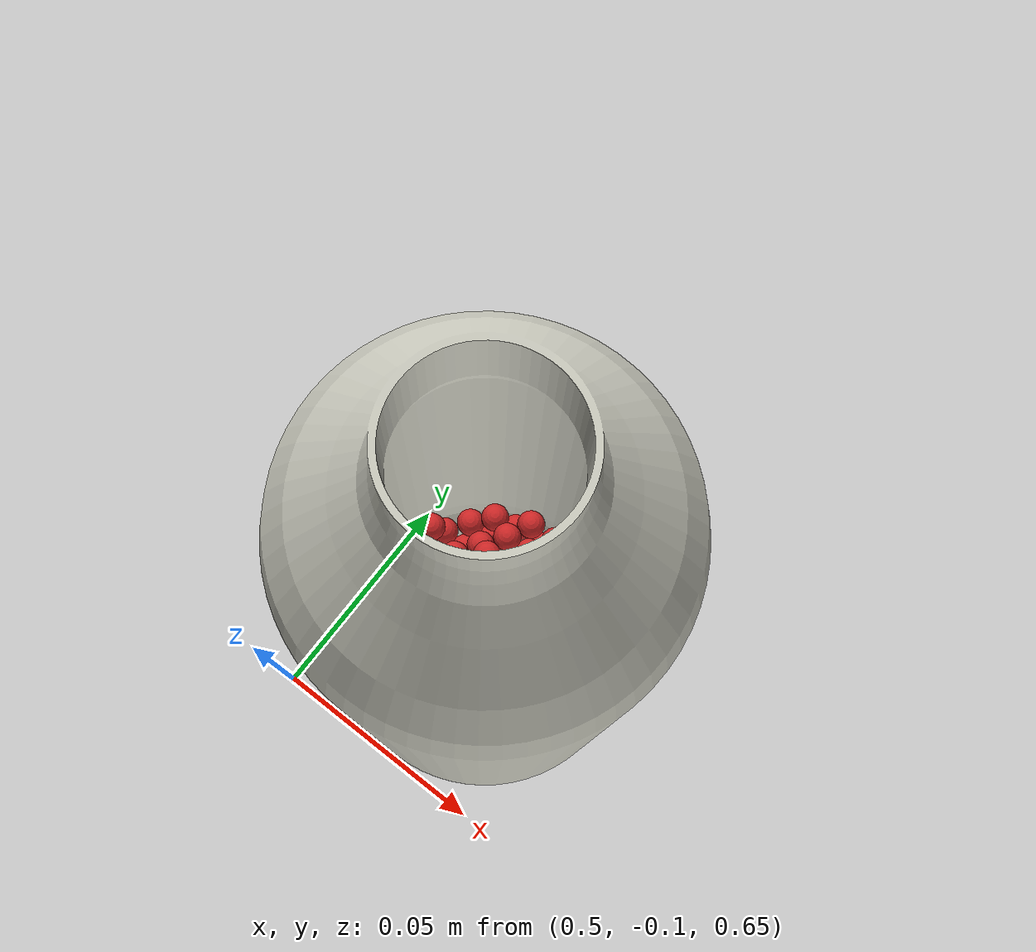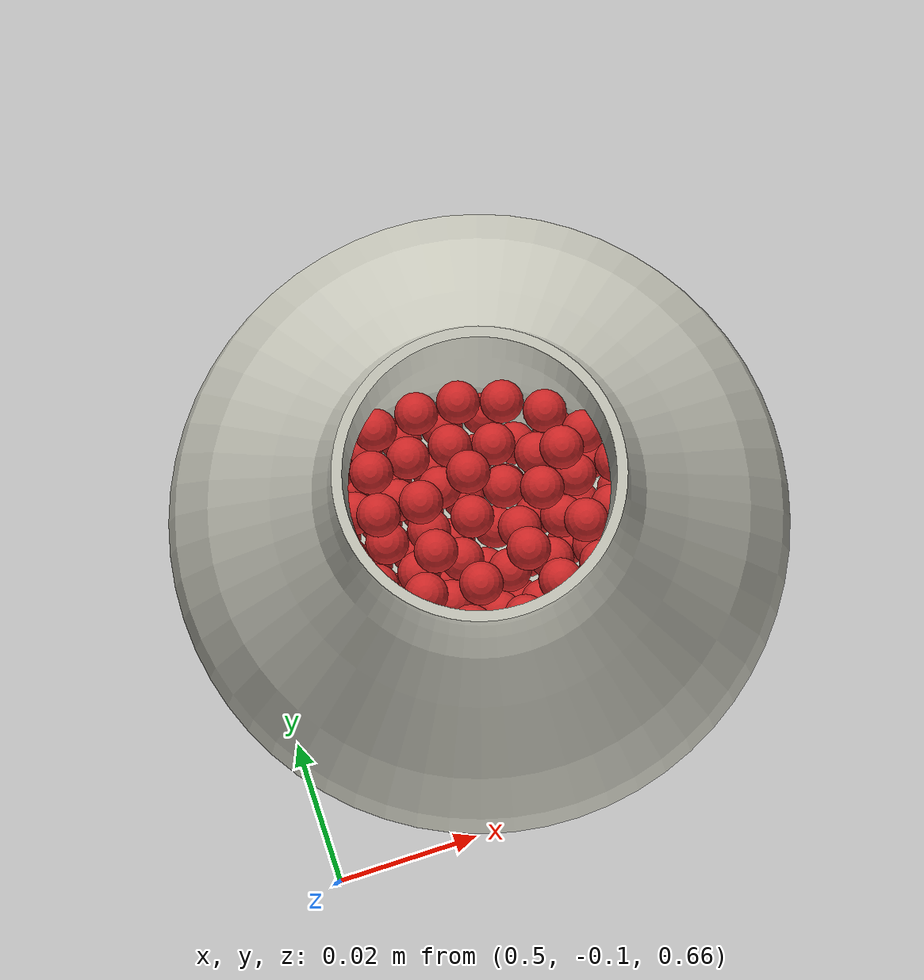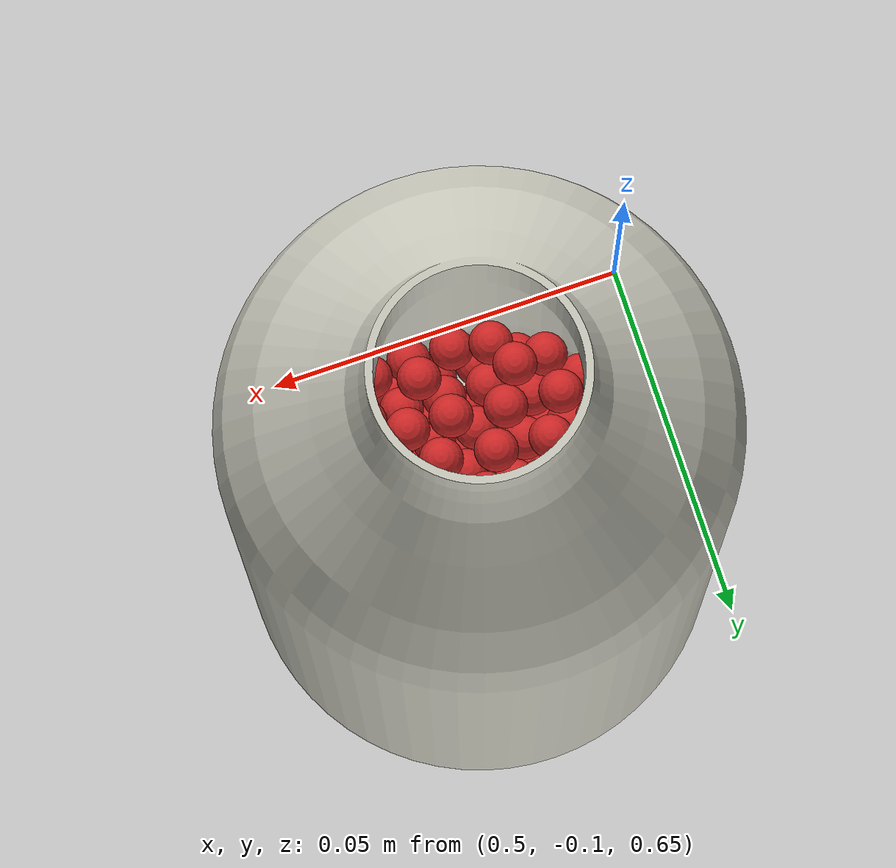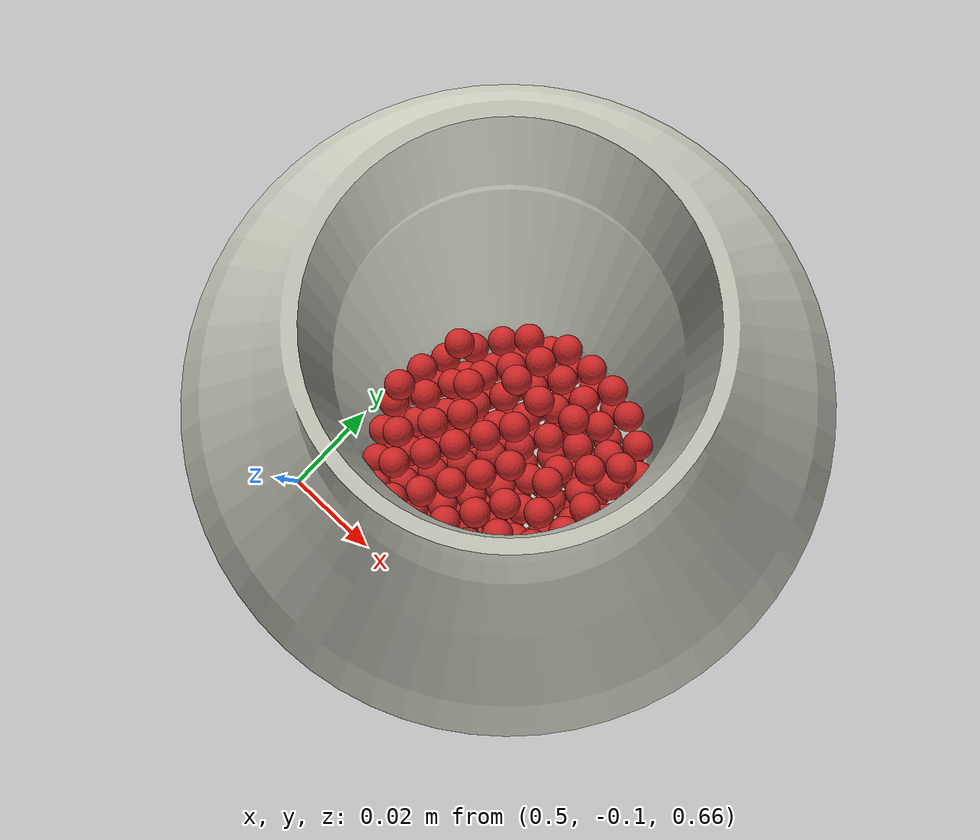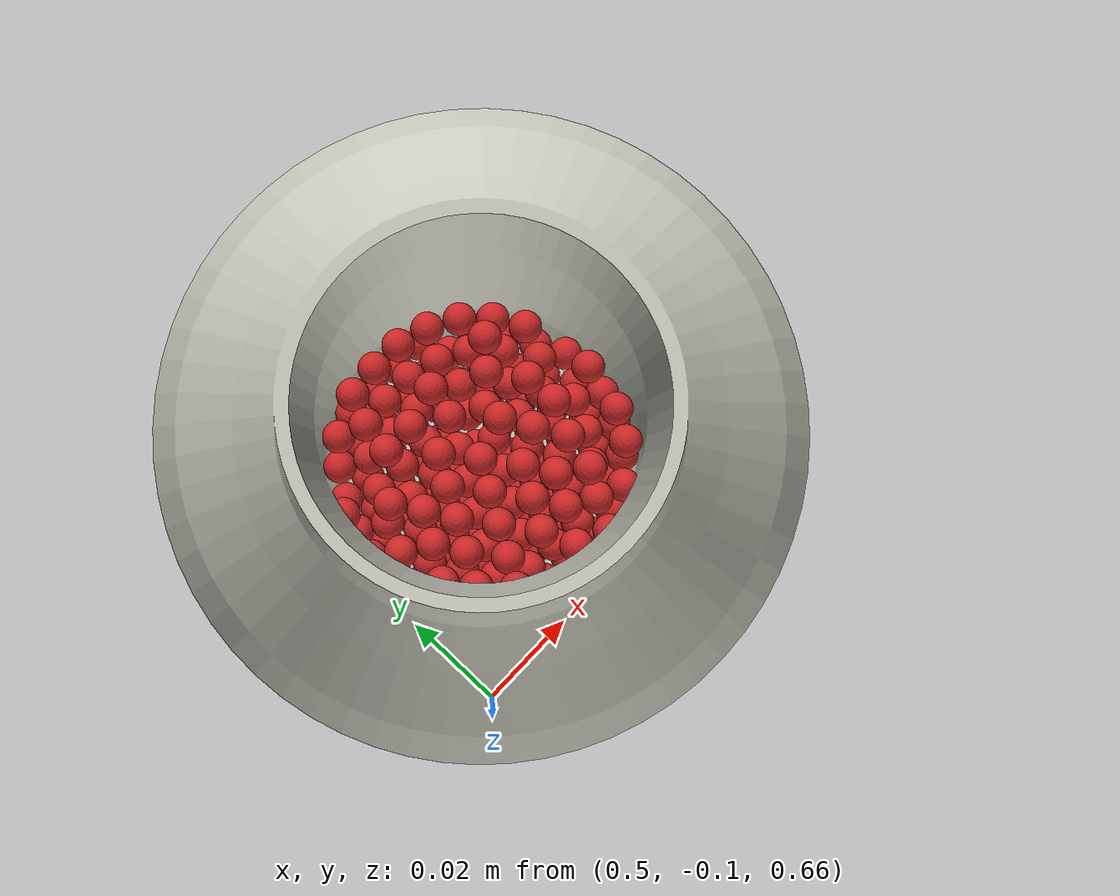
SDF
<sdf version="1.4">
 <world name="default">
  <physics type="ode">
   <gravity>0 0 -9.81</gravity>
   <ode>
    <solver><type>quick</type><iters>20</iters><sor>1</sor></solver>
    <constraints>
     <cfm>0</cfm>
     <erp>0.2</erp>
     <contact_max_correcting_vel>100</contact_max_correcting_vel>
     <contact_surface_layer>0</contact_surface_layer>
    </constraints>
   </ode>
   <real_time_update_rate>1000</real_time_update_rate>
   <max_step_size>0.001</max_step_size>
   <real_time_factor>1</real_time_factor>
  </physics>
  <light name="sun" type="directional">
   <pose>0 0 10 0 -0 0</pose>
   <diffuse>0.8 0.8 0.8 1</diffuse>
   <specular>0.2 0.2 0.2 1</specular>
   <attenuation>
    <range>1000</range>
    <constant>0.9</constant>
    <linear>0.01</linear>
    <quadratic>0.001</quadratic>
   </attenuation>
   <direction>-0.5 0.1 -0.9</direction>
  </light>
  <model name="ground_plane">
   <static>1</static>
   <link name="link">
    <collision name="collision">
     <geometry><plane><normal>0 0 1</normal><size>100 100</size></plane></geometry>
     <surface><friction><ode><mu>100</mu><mu2>50</mu2></ode></friction></surface>
    </collision>
    <visual name="visual">
     <cast_shadows>0</cast_shadows>
     <geometry><plane><normal>0 0 1</normal><size>100 100</size></plane></geometry>
     <material>
      <script><uri>file://media/materials/scripts/gazebo.material</uri><name>Gazebo/Grey</name></script>
     </material>
    </visual>
    <velocity_decay><linear>0</linear><angular>0</angular></velocity_decay>
   </link>
  </model>
  <scene><ambient>0.4 0.4 0.4 1</ambient><background>0.7 0.7 0.7 1</background><shadows>1</shadows></scene>
  <spherical_coordinates>
   <surface_model>EARTH_WGS84</surface_model>
   <latitude_deg>0</latitude_deg>
   <longitude_deg>0</longitude_deg>
   <elevation>0</elevation>
   <heading_deg>0</heading_deg>
  </spherical_coordinates>
  <model name="sphere0">
   <pose>-0.000751 -0.006096 -0.063583 0.008961 -0.001297 -0.00673</pose>
   <link name="link">
    <pose>0.54076 -0.048781 0.732288 0 -0 0</pose>
    <inertial>
     <mass>0.0000001</mass>
     <inertia><ixx>0.00004</ixx><ixy>0</ixy><ixz>0</ixz><iyy>0.00004</iyy><iyz>0</iyz><izz>0.00004</izz></inertia>
    </inertial>
    <collision name="collision">
     <surface>
      <contact><ode><kp>1e+10</kp><kd>1</kd></ode></contact>
      <friction><ode><mu>0.01</mu><mu2>0.01</mu2></ode></friction>
     </surface>
     <geometry><sphere><radius>0.003</radius></sphere></geometry>
    </collision>
    <visual name="visual">
     <geometry><sphere><radius>0.003</radius></sphere></geometry>
     <material>
      <script><uri>file://media/materials/scripts/gazebo.material</uri><name>Gazebo/Red</name></script>
     </material>
    </visual>
    <velocity_decay><linear>0</linear><angular>0</angular></velocity_decay>
   </link>
   <static>0</static>
  </model>
  <model name="sphere2">
   <pose>-0.01895 -0.049008 -0.066935 -0.010374 -0.005981 -0.001356</pose>
   <link name="link">
    <pose>0.55276 -0.048781 0.732288 0 -0 0</pose>
    <inertial>
     <mass>0.0000001</mass>
     <inertia><ixx>0.00004</ixx><ixy>0</ixy><ixz>0</ixz><iyy>0.00004</iyy><iyz>0</iyz><izz>0.00004</izz></inertia>
    </inertial>
    <collision name="collision">
     <surface>
      <contact><ode><kp>1e+10</kp><kd>1</kd></ode></contact>
      <friction><ode><mu>0.01</mu><mu2>0.01</mu2></ode></friction>
     </surface>
     <geometry><sphere><radius>0.003</radius></sphere></geometry>
    </collision>
    <visual name="visual">
     <geometry><sphere><radius>0.003</radius></sphere></geometry>
     <material>
      <script><uri>file://media/materials/scripts/gazebo.material</uri><name>Gazebo/Red</name></script>
     </material>
    </visual>
    <velocity_decay><linear>0</linear><angular>0</angular></velocity_decay>
   </link>
   <static>0</static>
  </model>
  <model name="sphere3">
   <pose>-0.044394 -0.047698 -0.057624 -0.003588 0.0046 0.006872</pose>
   <link name="link">
    <pose>0.55876 -0.048781 0.732288 0 -0 0</pose>
    <inertial>
     <mass>0.0000001</mass>
     <inertia><ixx>0.00004</ixx><ixy>0</ixy><ixz>0</ixz><iyy>0.00004</iyy><iyz>0</iyz><izz>0.00004</izz></inertia>
    </inertial>
    <collision name="collision">
     <surface>
      <contact><ode><kp>1e+10</kp><kd>1</kd></ode></contact>
      <friction><ode><mu>0.01</mu><mu2>0.01</mu2></ode></friction>
     </surface>
     <geometry><sphere><radius>0.003</radius></sphere></geometry>
    </collision>
    <visual name="visual">
     <geometry><sphere><radius>0.003</radius></sphere></geometry>
     <material>
      <script><uri>file://media/materials/scripts/gazebo.material</uri><name>Gazebo/Red</name></script>
     </material>
    </visual>
    <velocity_decay><linear>0</linear><angular>0</angular></velocity_decay>
   </link>
   <static>0</static>
  </model>
  <model name="sphere5">
   <pose>-0.034827 -0.02861 -0.058217 0.001859 -0.000326 -0.001189</pose>
   <link name="link">
    <pose>0.54676 -0.042781 0.732288 0 -0 0</pose>
    <inertial>
     <mass>0.0000001</mass>
     <inertia><ixx>0.00004</ixx><ixy>0</ixy><ixz>0</ixz><iyy>0.00004</iyy><iyz>0</iyz><izz>0.00004</izz></inertia>
    </inertial>
    <collision name="collision">
     <surface>
      <contact><ode><kp>1e+10</kp><kd>1</kd></ode></contact>
      <friction><ode><mu>0.01</mu><mu2>0.01</mu2></ode></friction>
     </surface>
     <geometry><sphere><radius>0.003</radius></sphere></geometry>
    </collision>
    <visual name="visual">
     <geometry><sphere><radius>0.003</radius></sphere></geometry>
     <material>
      <script><uri>file://media/materials/scripts/gazebo.material</uri><name>Gazebo/Red</name></script>
     </material>
    </visual>
    <velocity_decay><linear>0</linear><angular>0</angular></velocity_decay>
   </link>
   <static>0</static>
  </model>
  <model name="sphere6">
   <pose>-0.012521 -0.013986 -0.058935 -0.002324 -0.002503 -0.000765</pose>
   <link name="link">
    <pose>0.55276 -0.042781 0.732288 0 -0 0</pose>
    <inertial>
     <mass>0.0000001</mass>
     <inertia><ixx>0.00004</ixx><ixy>0</ixy><ixz>0</ixz><iyy>0.00004</iyy><iyz>0</iyz><izz>0.00004</izz></inertia>
    </inertial>
    <collision name="collision">
     <surface>
      <contact><ode><kp>1e+10</kp><kd>1</kd></ode></contact>
      <friction><ode><mu>0.01</mu><mu2>0.01</mu2></ode></friction>
     </surface>
     <geometry><sphere><radius>0.003</radius></sphere></geometry>
    </collision>
    <visual name="visual">
     <geometry><sphere><radius>0.003</radius></sphere></geometry>
     <material>
      <script><uri>file://media/materials/scripts/gazebo.material</uri><name>Gazebo/Red</name></script>
     </material>
    </visual>
    <velocity_decay><linear>0</linear><angular>0</angular></velocity_decay>
   </link>
   <static>0</static>
  </model>
  <model name="sphere7">
   <pose>-0.014852 -0.007093 -0.054244 0.006344 0.003192 0.012641</pose>
   <link name="link">
    <pose>0.55876 -0.042781 0.732288 0 -0 0</pose>
    <inertial>
     <mass>0.0000001</mass>
     <inertia><ixx>0.00004</ixx><ixy>0</ixy><ixz>0</ixz><iyy>0.00004</iyy><iyz>0</iyz><izz>0.00004</izz></inertia>
    </inertial>
    <collision name="collision">
     <surface>
      <contact><ode><kp>1e+10</kp><kd>1</kd></ode></contact>
      <friction><ode><mu>0.01</mu><mu2>0.01</mu2></ode></friction>
     </surface>
     <geometry><sphere><radius>0.003</radius></sphere></geometry>
    </collision>
    <visual name="visual">
     <geometry><sphere><radius>0.003</radius></sphere></geometry>
     <material>
      <script><uri>file://media/materials/scripts/gazebo.material</uri><name>Gazebo/Red</name></script>
     </material>
    </visual>
    <velocity_decay><linear>0</linear><angular>0</angular></velocity_decay>
   </link>
   <static>0</static>
  </model>
  <model name="sphere8">
   <pose>-0.011995 -0.038046 -0.064945 0.000812 -0.003027 0.000215</pose>
   <link name="link">
    <pose>0.54076 -0.036781 0.732288 0 -0 0</pose>
    <inertial>
     <mass>0.0000001</mass>
     <inertia><ixx>0.00004</ixx><ixy>0</ixy><ixz>0</ixz><iyy>0.00004</iyy><iyz>0</iyz><izz>0.00004</izz></inertia>
    </inertial>
    <collision name="collision">
     <surface>
      <contact><ode><kp>1e+10</kp><kd>1</kd></ode></contact>
      <friction><ode><mu>0.01</mu><mu2>0.01</mu2></ode></friction>
     </surface>
     <geometry><sphere><radius>0.003</radius></sphere></geometry>
    </collision>
    <visual name="visual">
     <geometry><sphere><radius>0.003</radius></sphere></geometry>
     <material>
      <script><uri>file://media/materials/scripts/gazebo.material</uri><name>Gazebo/Red</name></script>
     </material>
    </visual>
    <velocity_decay><linear>0</linear><angular>0</angular></velocity_decay>
   </link>
   <static>0</static>
  </model>
  <model name="sphere9">
   <pose>-0.024735 -0.022083 -0.054955 -0.002308 0.006572 -0.00148</pose>
   <link name="link">
    <pose>0.54676 -0.036781 0.732288 0 -0 0</pose>
    <inertial>
     <mass>0.0000001</mass>
     <inertia><ixx>0.00004</ixx><ixy>0</ixy><ixz>0</ixz><iyy>0.00004</iyy><iyz>0</iyz><izz>0.00004</izz></inertia>
    </inertial>
    <collision name="collision">
     <surface>
      <contact><ode><kp>1e+10</kp><kd>1</kd></ode></contact>
      <friction><ode><mu>0.01</mu><mu2>0.01</mu2></ode></friction>
     </surface>
     <geometry><sphere><radius>0.003</radius></sphere></geometry>
    </collision>
    <visual name="visual">
     <geometry><sphere><radius>0.003</radius></sphere></geometry>
     <material>
      <script><uri>file://media/materials/scripts/gazebo.material</uri><name>Gazebo/Red</name></script>
     </material>
    </visual>
    <velocity_decay><linear>0</linear><angular>0</angular></velocity_decay>
   </link>
   <static>0</static>
  </model>
  <model name="sphere10">
   <pose>-0.003044 -0.032273 -0.057024 0.008619 -0.006674 -0.000614</pose>
   <link name="link">
    <pose>0.55276 -0.036781 0.732288 0 -0 0</pose>
    <inertial>
     <mass>0.0000001</mass>
     <inertia><ixx>0.00004</ixx><ixy>0</ixy><ixz>0</ixz><iyy>0.00004</iyy><iyz>0</iyz><izz>0.00004</izz></inertia>
    </inertial>
    <collision name="collision">
     <surface>
      <contact><ode><kp>1e+10</kp><kd>1</kd></ode></contact>
      <friction><ode><mu>0.01</mu><mu2>0.01</mu2></ode></friction>
     </surface>
     <geometry><sphere><radius>0.003</radius></sphere></geometry>
    </collision>
    <visual name="visual">
     <geometry><sphere><radius>0.003</radius></sphere></geometry>
     <material>
      <script><uri>file://media/materials/scripts/gazebo.material</uri><name>Gazebo/Red</name></script>
     </material>
    </visual>
    <velocity_decay><linear>0</linear><angular>0</angular></velocity_decay>
   </link>
   <static>0</static>
  </model>
  <model name="sphere11">
   <pose>-0.020797 -0.053953 -0.055216 -0.058591 0.013196 -0.003456</pose>
   <link name="link">
    <pose>0.55876 -0.036781 0.732288 0 -0 0</pose>
    <inertial>
     <mass>0.0000001</mass>
     <inertia><ixx>0.00004</ixx><ixy>0</ixy><ixz>0</ixz><iyy>0.00004</iyy><iyz>0</iyz><izz>0.00004</izz></inertia>
    </inertial>
    <collision name="collision">
     <surface>
      <contact><ode><kp>1e+10</kp><kd>1</kd></ode></contact>
      <friction><ode><mu>0.01</mu><mu2>0.01</mu2></ode></friction>
     </surface>
     <geometry><sphere><radius>0.003</radius></sphere></geometry>
    </collision>
    <visual name="visual">
     <geometry><sphere><radius>0.003</radius></sphere></geometry>
     <material>
      <script><uri>file://media/materials/scripts/gazebo.material</uri><name>Gazebo/Red</name></script>
     </material>
    </visual>
    <velocity_decay><linear>0</linear><angular>0</angular></velocity_decay>
   </link>
   <static>0</static>
  </model>
  <model name="sphere12">
   <pose>-0.026586 -0.043876 -0.05611 0.009283 0.012691 0.001803</pose>
   <link name="link">
    <pose>0.54076 -0.030781 0.732288 0 -0 0</pose>
    <inertial>
     <mass>0.0000001</mass>
     <inertia><ixx>0.00004</ixx><ixy>0</ixy><ixz>0</ixz><iyy>0.00004</iyy><iyz>0</iyz><izz>0.00004</izz></inertia>
    </inertial>
    <collision name="collision">
     <surface>
      <contact><ode><kp>1e+10</kp><kd>1</kd></ode></contact>
      <friction><ode><mu>0.01</mu><mu2>0.01</mu2></ode></friction>
     </surface>
     <geometry><sphere><radius>0.003</radius></sphere></geometry>
    </collision>
    <visual name="visual">
     <geometry><sphere><radius>0.003</radius></sphere></geometry>
     <material>
      <script><uri>file://media/materials/scripts/gazebo.material</uri><name>Gazebo/Red</name></script>
     </material>
    </visual>
    <velocity_decay><linear>0</linear><angular>0</angular></velocity_decay>
   </link>
   <static>0</static>
  </model>
  <model name="sphere13">
   <pose>-0.034947 -0.036555 -0.061277 -0.010989 0.004302 -0.010016</pose>
   <link name="link">
    <pose>0.54676 -0.030781 0.732288 0 -0 0</pose>
    <inertial>
     <mass>0.0000001</mass>
     <inertia><ixx>0.00004</ixx><ixy>0</ixy><ixz>0</ixz><iyy>0.00004</iyy><iyz>0</iyz><izz>0.00004</izz></inertia>
    </inertial>
    <collision name="collision">
     <surface>
      <contact><ode><kp>1e+10</kp><kd>1</kd></ode></contact>
      <friction><ode><mu>0.01</mu><mu2>0.01</mu2></ode></friction>
     </surface>
     <geometry><sphere><radius>0.003</radius></sphere></geometry>
    </collision>
    <visual name="visual">
     <geometry><sphere><radius>0.003</radius></sphere></geometry>
     <material>
      <script><uri>file://media/materials/scripts/gazebo.material</uri><name>Gazebo/Red</name></script>
     </material>
    </visual>
    <velocity_decay><linear>0</linear><angular>0</angular></velocity_decay>
   </link>
   <static>0</static>
  </model>
  <model name="sphere14">
   <pose>-0.003198 -0.027274 -0.082089 0.003 -0.03486 0.001054</pose>
   <link name="link">
    <pose>0.55276 -0.030781 0.732288 0 -0 0</pose>
    <inertial>
     <mass>0.0000001</mass>
     <inertia><ixx>0.00004</ixx><ixy>0</ixy><ixz>0</ixz><iyy>0.00004</iyy><iyz>0</iyz><izz>0.00004</izz></inertia>
    </inertial>
    <collision name="collision">
     <surface>
      <contact><ode><kp>1e+10</kp><kd>1</kd></ode></contact>
      <friction><ode><mu>0.01</mu><mu2>0.01</mu2></ode></friction>
     </surface>
     <geometry><sphere><radius>0.003</radius></sphere></geometry>
    </collision>
    <visual name="visual">
     <geometry><sphere><radius>0.003</radius></sphere></geometry>
     <material>
      <script><uri>file://media/materials/scripts/gazebo.material</uri><name>Gazebo/Red</name></script>
     </material>
    </visual>
    <velocity_decay><linear>0</linear><angular>0</angular></velocity_decay>
   </link>
   <static>0</static>
  </model>
  <model name="sphere15">
   <pose>-0.014854 -0.034476 -0.067614 -0.013995 -0.006976 0.000594</pose>
   <link name="link">
    <pose>0.55876 -0.030781 0.732288 0 -0 0</pose>
    <inertial>
     <mass>0.0000001</mass>
     <inertia><ixx>0.00004</ixx><ixy>0</ixy><ixz>0</ixz><iyy>0.00004</iyy><iyz>0</iyz><izz>0.00004</izz></inertia>
    </inertial>
    <collision name="collision">
     <surface>
      <contact><ode><kp>1e+10</kp><kd>1</kd></ode></contact>
      <friction><ode><mu>0.01</mu><mu2>0.01</mu2></ode></friction>
     </surface>
     <geometry><sphere><radius>0.003</radius></sphere></geometry>
    </collision>
    <visual name="visual">
     <geometry><sphere><radius>0.003</radius></sphere></geometry>
     <material>
      <script><uri>file://media/materials/scripts/gazebo.material</uri><name>Gazebo/Red</name></script>
     </material>
    </visual>
    <velocity_decay><linear>0</linear><angular>0</angular></velocity_decay>
   </link>
   <static>0</static>
  </model>
  <model name="sphere16">
   <pose>-0.024652 -0.02894 -0.065397 0.000577 -0.001939 -0.000928</pose>
   <link name="link">
    <pose>0.54076 -0.048781 0.738288 0 -0 0</pose>
    <inertial>
     <mass>0.0000001</mass>
     <inertia><ixx>0.00004</ixx><ixy>0</ixy><ixz>0</ixz><iyy>0.00004</iyy><iyz>0</iyz><izz>0.00004</izz></inertia>
    </inertial>
    <collision name="collision">
     <surface>
      <contact><ode><kp>1e+10</kp><kd>1</kd></ode></contact>
      <friction><ode><mu>0.01</mu><mu2>0.01</mu2></ode></friction>
     </surface>
     <geometry><sphere><radius>0.003</radius></sphere></geometry>
    </collision>
    <visual name="visual">
     <geometry><sphere><radius>0.003</radius></sphere></geometry>
     <material>
      <script><uri>file://media/materials/scripts/gazebo.material</uri><name>Gazebo/Red</name></script>
     </material>
    </visual>
    <velocity_decay><linear>0</linear><angular>0</angular></velocity_decay>
   </link>
   <static>0</static>
  </model>
  <model name="sphere17">
   <pose>-0.008639 -0.035869 -0.069088 -0.001103 0.000647 -0.00359</pose>
   <link name="link">
    <pose>0.54676 -0.048781 0.738288 0 -0 0</pose>
    <inertial>
     <mass>0.0000001</mass>
     <inertia><ixx>0.00004</ixx><ixy>0</ixy><ixz>0</ixz><iyy>0.00004</iyy><iyz>0</iyz><izz>0.00004</izz></inertia>
    </inertial>
    <collision name="collision">
     <surface>
      <contact><ode><kp>1e+10</kp><kd>1</kd></ode></contact>
      <friction><ode><mu>0.01</mu><mu2>0.01</mu2></ode></friction>
     </surface>
     <geometry><sphere><radius>0.003</radius></sphere></geometry>
    </collision>
    <visual name="visual">
     <geometry><sphere><radius>0.003</radius></sphere></geometry>
     <material>
      <script><uri>file://media/materials/scripts/gazebo.material</uri><name>Gazebo/Red</name></script>
     </material>
    </visual>
    <velocity_decay><linear>0</linear><angular>0</angular></velocity_decay>
   </link>
   <static>0</static>
  </model>
  <model name="sphere18">
   <pose>-0.012784 -0.014512 -0.060514 0.016222 0.014455 -0.000565</pose>
   <link name="link">
    <pose>0.55276 -0.048781 0.738288 0 -0 0</pose>
    <inertial>
     <mass>0.0000001</mass>
     <inertia><ixx>0.00004</ixx><ixy>0</ixy><ixz>0</ixz><iyy>0.00004</iyy><iyz>0</iyz><izz>0.00004</izz></inertia>
    </inertial>
    <collision name="collision">
     <surface>
      <contact><ode><kp>1e+10</kp><kd>1</kd></ode></contact>
      <friction><ode><mu>0.01</mu><mu2>0.01</mu2></ode></friction>
     </surface>
     <geometry><sphere><radius>0.003</radius></sphere></geometry>
    </collision>
    <visual name="visual">
     <geometry><sphere><radius>0.003</radius></sphere></geometry>
     <material>
      <script><uri>file://media/materials/scripts/gazebo.material</uri><name>Gazebo/Red</name></script>
     </material>
    </visual>
    <velocity_decay><linear>0</linear><angular>0</angular></velocity_decay>
   </link>
   <static>0</static>
  </model>
  <model name="sphere19">
   <pose>-0.010585 -0.046733 -0.065967 -0.013053 -0.003186 -0.005735</pose>
   <link name="link">
    <pose>0.55876 -0.048781 0.738288 0 -0 0</pose>
    <inertial>
     <mass>0.0000001</mass>
     <inertia><ixx>0.00004</ixx><ixy>0</ixy><ixz>0</ixz><iyy>0.00004</iyy><iyz>0</iyz><izz>0.00004</izz></inertia>
    </inertial>
    <collision name="collision">
     <surface>
      <contact><ode><kp>1e+10</kp><kd>1</kd></ode></contact>
      <friction><ode><mu>0.01</mu><mu2>0.01</mu2></ode></friction>
     </surface>
     <geometry><sphere><radius>0.003</radius></sphere></geometry>
    </collision>
    <visual name="visual">
     <geometry><sphere><radius>0.003</radius></sphere></geometry>
     <material>
      <script><uri>file://media/materials/scripts/gazebo.material</uri><name>Gazebo/Red</name></script>
     </material>
    </visual>
    <velocity_decay><linear>0</linear><angular>0</angular></velocity_decay>
   </link>
   <static>0</static>
  </model>
  <model name="sphere20">
   <pose>-0.035198 -0.042568 -0.048904 0.002333 0.036754 0.002307</pose>
   <link name="link">
    <pose>0.54076 -0.042781 0.738288 0 -0 0</pose>
    <inertial>
     <mass>0.0000001</mass>
     <inertia><ixx>0.00004</ixx><ixy>0</ixy><ixz>0</ixz><iyy>0.00004</iyy><iyz>0</iyz><izz>0.00004</izz></inertia>
    </inertial>
    <collision name="collision">
     <surface>
      <contact><ode><kp>1e+10</kp><kd>1</kd></ode></contact>
      <friction><ode><mu>0.01</mu><mu2>0.01</mu2></ode></friction>
     </surface>
     <geometry><sphere><radius>0.003</radius></sphere></geometry>
    </collision>
    <visual name="visual">
     <geometry><sphere><radius>0.003</radius></sphere></geometry>
     <material>
      <script><uri>file://media/materials/scripts/gazebo.material</uri><name>Gazebo/Red</name></script>
     </material>
    </visual>
    <velocity_decay><linear>0</linear><angular>0</angular></velocity_decay>
   </link>
   <static>0</static>
  </model>
  <model name="sphere21">
   <pose>-0.027115 -0.020637 -0.061463 -0.00017 0.005508 0.000319</pose>
   <link name="link">
    <pose>0.54676 -0.042781 0.738288 0 -0 0</pose>
    <inertial>
     <mass>0.0000001</mass>
     <inertia><ixx>0.00004</ixx><ixy>0</ixy><ixz>0</ixz><iyy>0.00004</iyy><iyz>0</iyz><izz>0.00004</izz></inertia>
    </inertial>
    <collision name="collision">
     <surface>
      <contact><ode><kp>1e+10</kp><kd>1</kd></ode></contact>
      <friction><ode><mu>0.01</mu><mu2>0.01</mu2></ode></friction>
     </surface>
     <geometry><sphere><radius>0.003</radius></sphere></geometry>
    </collision>
    <visual name="visual">
     <geometry><sphere><radius>0.003</radius></sphere></geometry>
     <material>
      <script><uri>file://media/materials/scripts/gazebo.material</uri><name>Gazebo/Red</name></script>
     </material>
    </visual>
    <velocity_decay><linear>0</linear><angular>0</angular></velocity_decay>
   </link>
   <static>0</static>
  </model>
  <model name="sphere22">
   <pose>-0.029571 -0.01944 -0.059918 -0.013692 0.009152 -0.001339</pose>
   <link name="link">
    <pose>0.55276 -0.042781 0.738288 0 -0 0</pose>
    <inertial>
     <mass>0.0000001</mass>
     <inertia><ixx>0.00004</ixx><ixy>0</ixy><ixz>0</ixz><iyy>0.00004</iyy><iyz>0</iyz><izz>0.00004</izz></inertia>
    </inertial>
    <collision name="collision">
     <surface>
      <contact><ode><kp>1e+10</kp><kd>1</kd></ode></contact>
      <friction><ode><mu>0.01</mu><mu2>0.01</mu2></ode></friction>
     </surface>
     <geometry><sphere><radius>0.003</radius></sphere></geometry>
    </collision>
    <visual name="visual">
     <geometry><sphere><radius>0.003</radius></sphere></geometry>
     <material>
      <script><uri>file://media/materials/scripts/gazebo.material</uri><name>Gazebo/Red</name></script>
     </material>
    </visual>
    <velocity_decay><linear>0</linear><angular>0</angular></velocity_decay>
   </link>
   <static>0</static>
  </model>
  <model name="sphere23">
   <pose>-0.012335 -0.028903 -0.063798 0.015874 0.008256 0.02301</pose>
   <link name="link">
    <pose>0.55876 -0.042781 0.738288 0 -0 0</pose>
    <inertial>
     <mass>0.0000001</mass>
     <inertia><ixx>0.00004</ixx><ixy>0</ixy><ixz>0</ixz><iyy>0.00004</iyy><iyz>0</iyz><izz>0.00004</izz></inertia>
    </inertial>
    <collision name="collision">
     <surface>
      <contact><ode><kp>1e+10</kp><kd>1</kd></ode></contact>
      <friction><ode><mu>0.01</mu><mu2>0.01</mu2></ode></friction>
     </surface>
     <geometry><sphere><radius>0.003</radius></sphere></geometry>
    </collision>
    <visual name="visual">
     <geometry><sphere><radius>0.003</radius></sphere></geometry>
     <material>
      <script><uri>file://media/materials/scripts/gazebo.material</uri><name>Gazebo/Red</name></script>
     </material>
    </visual>
    <velocity_decay><linear>0</linear><angular>0</angular></velocity_decay>
   </link>
   <static>0</static>
  </model>
  <model name="sphere24">
   <pose>-0.033227 -0.061752 -0.064947 -0.032589 0.009565 -0.001294</pose>
   <link name="link">
    <pose>0.54076 -0.036781 0.738288 0 -0 0</pose>
    <inertial>
     <mass>0.0000001</mass>
     <inertia><ixx>0.00004</ixx><ixy>0</ixy><ixz>0</ixz><iyy>0.00004</iyy><iyz>0</iyz><izz>0.00004</izz></inertia>
    </inertial>
    <collision name="collision">
     <surface>
      <contact><ode><kp>1e+10</kp><kd>1</kd></ode></contact>
      <friction><ode><mu>0.01</mu><mu2>0.01</mu2></ode></friction>
     </surface>
     <geometry><sphere><radius>0.003</radius></sphere></geometry>
    </collision>
    <visual name="visual">
     <geometry><sphere><radius>0.003</radius></sphere></geometry>
     <material>
      <script><uri>file://media/materials/scripts/gazebo.material</uri><name>Gazebo/Red</name></script>
     </material>
    </visual>
    <velocity_decay><linear>0</linear><angular>0</angular></velocity_decay>
   </link>
   <static>0</static>
  </model>
  <model name="sphere25">
   <pose>-0.027048 -0.023077 -0.061813 -0.000256 0.013666 -0.000145</pose>
   <link name="link">
    <pose>0.54676 -0.036781 0.738288 0 -0 0</pose>
    <inertial>
     <mass>0.0000001</mass>
     <inertia><ixx>0.00004</ixx><ixy>0</ixy><ixz>0</ixz><iyy>0.00004</iyy><iyz>0</iyz><izz>0.00004</izz></inertia>
    </inertial>
    <collision name="collision">
     <surface>
      <contact><ode><kp>1e+10</kp><kd>1</kd></ode></contact>
      <friction><ode><mu>0.01</mu><mu2>0.01</mu2></ode></friction>
     </surface>
     <geometry><sphere><radius>0.003</radius></sphere></geometry>
    </collision>
    <visual name="visual">
     <geometry><sphere><radius>0.003</radius></sphere></geometry>
     <material>
      <script><uri>file://media/materials/scripts/gazebo.material</uri><name>Gazebo/Red</name></script>
     </material>
    </visual>
    <velocity_decay><linear>0</linear><angular>0</angular></velocity_decay>
   </link>
   <static>0</static>
  </model>
  <model name="sphere26">
   <pose>-0.040076 -0.012608 -0.053665 0.006294 0.027587 -0.001008</pose>
   <link name="link">
    <pose>0.55276 -0.036781 0.738288 0 -0 0</pose>
    <inertial>
     <mass>0.0000001</mass>
     <inertia><ixx>0.00004</ixx><ixy>0</ixy><ixz>0</ixz><iyy>0.00004</iyy><iyz>0</iyz><izz>0.00004</izz></inertia>
    </inertial>
    <collision name="collision">
     <surface>
      <contact><ode><kp>1e+10</kp><kd>1</kd></ode></contact>
      <friction><ode><mu>0.01</mu><mu2>0.01</mu2></ode></friction>
     </surface>
     <geometry><sphere><radius>0.003</radius></sphere></geometry>
    </collision>
    <visual name="visual">
     <geometry><sphere><radius>0.003</radius></sphere></geometry>
     <material>
      <script><uri>file://media/materials/scripts/gazebo.material</uri><name>Gazebo/Red</name></script>
     </material>
    </visual>
    <velocity_decay><linear>0</linear><angular>0</angular></velocity_decay>
   </link>
   <static>0</static>
  </model>
  <model name="sphere27">
   <pose>-0.044037 0.026749 -0.052094 0.04819 0.024733 0.00225</pose>
   <link name="link">
    <pose>0.55876 -0.036781 0.738288 0 -0 0</pose>
    <inertial>
     <mass>0.0000001</mass>
     <inertia><ixx>0.00004</ixx><ixy>0</ixy><ixz>0</ixz><iyy>0.00004</iyy><iyz>0</iyz><izz>0.00004</izz></inertia>
    </inertial>
    <collision name="collision">
     <surface>
      <contact><ode><kp>1e+10</kp><kd>1</kd></ode></contact>
      <friction><ode><mu>0.01</mu><mu2>0.01</mu2></ode></friction>
     </surface>
     <geometry><sphere><radius>0.003</radius></sphere></geometry>
    </collision>
    <visual name="visual">
     <geometry><sphere><radius>0.003</radius></sphere></geometry>
     <material>
      <script><uri>file://media/materials/scripts/gazebo.material</uri><name>Gazebo/Red</name></script>
     </material>
    </visual>
    <velocity_decay><linear>0</linear><angular>0</angular></velocity_decay>
   </link>
   <static>0</static>
  </model>
  <model name="sphere28">
   <pose>-0.028329 -0.078865 -0.072438 -0.041415 -0.005195 0.007412</pose>
   <link name="link">
    <pose>0.54076 -0.030781 0.738288 0 -0 0</pose>
    <inertial>
     <mass>0.0000001</mass>
     <inertia><ixx>0.00004</ixx><ixy>0</ixy><ixz>0</ixz><iyy>0.00004</iyy><iyz>0</iyz><izz>0.00004</izz></inertia>
    </inertial>
    <collision name="collision">
     <surface>
      <contact><ode><kp>1e+10</kp><kd>1</kd></ode></contact>
      <friction><ode><mu>0.01</mu><mu2>0.01</mu2></ode></friction>
     </surface>
     <geometry><sphere><radius>0.003</radius></sphere></geometry>
    </collision>
    <visual name="visual">
     <geometry><sphere><radius>0.003</radius></sphere></geometry>
     <material>
      <script><uri>file://media/materials/scripts/gazebo.material</uri><name>Gazebo/Red</name></script>
     </material>
    </visual>
    <velocity_decay><linear>0</linear><angular>0</angular></velocity_decay>
   </link>
   <static>0</static>
  </model>
  <model name="sphere29">
   <pose>-0.057388 -0.072465 -0.052823 -0.060579 0.030622 -0.001886</pose>
   <link name="link">
    <pose>0.54676 -0.030781 0.738288 0 -0 0</pose>
    <inertial>
     <mass>0.0000001</mass>
     <inertia><ixx>0.00004</ixx><ixy>0</ixy><ixz>0</ixz><iyy>0.00004</iyy><iyz>0</iyz><izz>0.00004</izz></inertia>
    </inertial>
    <collision name="collision">
     <surface>
      <contact><ode><kp>1e+10</kp><kd>1</kd></ode></contact>
      <friction><ode><mu>0.01</mu><mu2>0.01</mu2></ode></friction>
     </surface>
     <geometry><sphere><radius>0.003</radius></sphere></geometry>
    </collision>
    <visual name="visual">
     <geometry><sphere><radius>0.003</radius></sphere></geometry>
     <material>
      <script><uri>file://media/materials/scripts/gazebo.material</uri><name>Gazebo/Red</name></script>
     </material>
    </visual>
    <velocity_decay><linear>0</linear><angular>0</angular></velocity_decay>
   </link>
   <static>0</static>
  </model>
  <model name="sphere30">
   <pose>-0.027193 -0.014303 -0.066022 0.006261 0.005783 0.000595</pose>
   <link name="link">
    <pose>0.55276 -0.030781 0.738288 0 -0 0</pose>
    <inertial>
     <mass>0.0000001</mass>
     <inertia><ixx>0.00004</ixx><ixy>0</ixy><ixz>0</ixz><iyy>0.00004</iyy><iyz>0</iyz><izz>0.00004</izz></inertia>
    </inertial>
    <collision name="collision">
     <surface>
      <contact><ode><kp>1e+10</kp><kd>1</kd></ode></contact>
      <friction><ode><mu>0.01</mu><mu2>0.01</mu2></ode></friction>
     </surface>
     <geometry><sphere><radius>0.003</radius></sphere></geometry>
    </collision>
    <visual name="visual">
     <geometry><sphere><radius>0.003</radius></sphere></geometry>
     <material>
      <script><uri>file://media/materials/scripts/gazebo.material</uri><name>Gazebo/Red</name></script>
     </material>
    </visual>
    <velocity_decay><linear>0</linear><angular>0</angular></velocity_decay>
   </link>
   <static>0</static>
  </model>
  <model name="sphere31">
   <pose>-0.019028 -0.020062 -0.072431 -0.002981 -0.005194 -0.001456</pose>
   <link name="link">
    <pose>0.55876 -0.030781 0.738288 0 -0 0</pose>
    <inertial>
     <mass>0.0000001</mass>
     <inertia><ixx>0.00004</ixx><ixy>0</ixy><ixz>0</ixz><iyy>0.00004</iyy><iyz>0</iyz><izz>0.00004</izz></inertia>
    </inertial>
    <collision name="collision">
     <surface>
      <contact><ode><kp>1e+10</kp><kd>1</kd></ode></contact>
      <friction><ode><mu>0.01</mu><mu2>0.01</mu2></ode></friction>
     </surface>
     <geometry><sphere><radius>0.003</radius></sphere></geometry>
    </collision>
    <visual name="visual">
     <geometry><sphere><radius>0.003</radius></sphere></geometry>
     <material>
      <script><uri>file://media/materials/scripts/gazebo.material</uri><name>Gazebo/Red</name></script>
     </material>
    </visual>
    <velocity_decay><linear>0</linear><angular>0</angular></velocity_decay>
   </link>
   <static>0</static>
  </model>
  <model name="sphere32">
   <pose>0.001349 -0.015082 -0.075275 -0.000812 0.000243 -0.013007</pose>
   <link name="link">
    <pose>0.54076 -0.048781 0.744288 0 -0 0</pose>
    <inertial>
     <mass>0.0000001</mass>
     <inertia><ixx>0.00004</ixx><ixy>0</ixy><ixz>0</ixz><iyy>0.00004</iyy><iyz>0</iyz><izz>0.00004</izz></inertia>
    </inertial>
    <collision name="collision">
     <surface>
      <contact><ode><kp>1e+10</kp><kd>1</kd></ode></contact>
      <friction><ode><mu>0.01</mu><mu2>0.01</mu2></ode></friction>
     </surface>
     <geometry><sphere><radius>0.003</radius></sphere></geometry>
    </collision>
    <visual name="visual">
     <geometry><sphere><radius>0.003</radius></sphere></geometry>
     <material>
      <script><uri>file://media/materials/scripts/gazebo.material</uri><name>Gazebo/Red</name></script>
     </material>
    </visual>
    <velocity_decay><linear>0</linear><angular>0</angular></velocity_decay>
   </link>
   <static>0</static>
  </model>
  <model name="sphere33">
   <pose>0.009708 -0.038596 -0.084094 -0.026877 -0.023403 -0.00874</pose>
   <link name="link">
    <pose>0.54676 -0.048781 0.744288 0 -0 0</pose>
    <inertial>
     <mass>0.0000001</mass>
     <inertia><ixx>0.00004</ixx><ixy>0</ixy><ixz>0</ixz><iyy>0.00004</iyy><iyz>0</iyz><izz>0.00004</izz></inertia>
    </inertial>
    <collision name="collision">
     <surface>
      <contact><ode><kp>1e+10</kp><kd>1</kd></ode></contact>
      <friction><ode><mu>0.01</mu><mu2>0.01</mu2></ode></friction>
     </surface>
     <geometry><sphere><radius>0.003</radius></sphere></geometry>
    </collision>
    <visual name="visual">
     <geometry><sphere><radius>0.003</radius></sphere></geometry>
     <material>
      <script><uri>file://media/materials/scripts/gazebo.material</uri><name>Gazebo/Red</name></script>
     </material>
    </visual>
    <velocity_decay><linear>0</linear><angular>0</angular></velocity_decay>
   </link>
   <static>0</static>
  </model>
  <model name="sphere34">
   <pose>-0.025953 -0.054325 -0.077858 -0.011172 -0.004961 0.00726</pose>
   <link name="link">
    <pose>0.55276 -0.048781 0.744288 0 -0 0</pose>
    <inertial>
     <mass>0.0000001</mass>
     <inertia><ixx>0.00004</ixx><ixy>0</ixy><ixz>0</ixz><iyy>0.00004</iyy><iyz>0</iyz><izz>0.00004</izz></inertia>
    </inertial>
    <collision name="collision">
     <surface>
      <contact><ode><kp>1e+10</kp><kd>1</kd></ode></contact>
      <friction><ode><mu>0.01</mu><mu2>0.01</mu2></ode></friction>
     </surface>
     <geometry><sphere><radius>0.003</radius></sphere></geometry>
    </collision>
    <visual name="visual">
     <geometry><sphere><radius>0.003</radius></sphere></geometry>
     <material>
      <script><uri>file://media/materials/scripts/gazebo.material</uri><name>Gazebo/Red</name></script>
     </material>
    </visual>
    <velocity_decay><linear>0</linear><angular>0</angular></velocity_decay>
   </link>
   <static>0</static>
  </model>
  <model name="sphere35">
   <pose>-0.037344 -0.032251 -0.071337 0.005423 0.006829 -0.001112</pose>
   <link name="link">
    <pose>0.55876 -0.048781 0.744288 0 -0 0</pose>
    <inertial>
     <mass>0.0000001</mass>
     <inertia><ixx>0.00004</ixx><ixy>0</ixy><ixz>0</ixz><iyy>0.00004</iyy><iyz>0</iyz><izz>0.00004</izz></inertia>
    </inertial>
    <collision name="collision">
     <surface>
      <contact><ode><kp>1e+10</kp><kd>1</kd></ode></contact>
      <friction><ode><mu>0.01</mu><mu2>0.01</mu2></ode></friction>
     </surface>
     <geometry><sphere><radius>0.003</radius></sphere></geometry>
    </collision>
    <visual name="visual">
     <geometry><sphere><radius>0.003</radius></sphere></geometry>
     <material>
      <script><uri>file://media/materials/scripts/gazebo.material</uri><name>Gazebo/Red</name></script>
     </material>
    </visual>
    <velocity_decay><linear>0</linear><angular>0</angular></velocity_decay>
   </link>
   <static>0</static>
  </model>
  <model name="sphere36">
   <pose>-0.028461 -0.033955 -0.072567 0.00911 0.003166 -0.003709</pose>
   <link name="link">
    <pose>0.54076 -0.042781 0.744288 0 -0 0</pose>
    <inertial>
     <mass>0.0000001</mass>
     <inertia><ixx>0.00004</ixx><ixy>0</ixy><ixz>0</ixz><iyy>0.00004</iyy><iyz>0</iyz><izz>0.00004</izz></inertia>
    </inertial>
    <collision name="collision">
     <surface>
      <contact><ode><kp>1e+10</kp><kd>1</kd></ode></contact>
      <friction><ode><mu>0.01</mu><mu2>0.01</mu2></ode></friction>
     </surface>
     <geometry><sphere><radius>0.003</radius></sphere></geometry>
    </collision>
    <visual name="visual">
     <geometry><sphere><radius>0.003</radius></sphere></geometry>
     <material>
      <script><uri>file://media/materials/scripts/gazebo.material</uri><name>Gazebo/Red</name></script>
     </material>
    </visual>
    <velocity_decay><linear>0</linear><angular>0</angular></velocity_decay>
   </link>
   <static>0</static>
  </model>
  <model name="sphere37">
   <pose>0.017492 -0.029411 -0.079629 -0.000302 -0.018276 -0.000286</pose>
   <link name="link">
    <pose>0.54676 -0.042781 0.744288 0 -0 0</pose>
    <inertial>
     <mass>0.0000001</mass>
     <inertia><ixx>0.00004</ixx><ixy>0</ixy><ixz>0</ixz><iyy>0.00004</iyy><iyz>0</iyz><izz>0.00004</izz></inertia>
    </inertial>
    <collision name="collision">
     <surface>
      <contact><ode><kp>1e+10</kp><kd>1</kd></ode></contact>
      <friction><ode><mu>0.01</mu><mu2>0.01</mu2></ode></friction>
     </surface>
     <geometry><sphere><radius>0.003</radius></sphere></geometry>
    </collision>
    <visual name="visual">
     <geometry><sphere><radius>0.003</radius></sphere></geometry>
     <material>
      <script><uri>file://media/materials/scripts/gazebo.material</uri><name>Gazebo/Red</name></script>
     </material>
    </visual>
    <velocity_decay><linear>0</linear><angular>0</angular></velocity_decay>
   </link>
   <static>0</static>
  </model>
  <model name="sphere38">
   <pose>-0.02184 -0.030052 -0.062673 -0.007751 0.014486 0.000431</pose>
   <link name="link">
    <pose>0.55276 -0.042781 0.744288 0 -0 0</pose>
    <inertial>
     <mass>0.0000001</mass>
     <inertia><ixx>0.00004</ixx><ixy>0</ixy><ixz>0</ixz><iyy>0.00004</iyy><iyz>0</iyz><izz>0.00004</izz></inertia>
    </inertial>
    <collision name="collision">
     <surface>
      <contact><ode><kp>1e+10</kp><kd>1</kd></ode></contact>
      <friction><ode><mu>0.01</mu><mu2>0.01</mu2></ode></friction>
     </surface>
     <geometry><sphere><radius>0.003</radius></sphere></geometry>
    </collision>
    <visual name="visual">
     <geometry><sphere><radius>0.003</radius></sphere></geometry>
     <material>
      <script><uri>file://media/materials/scripts/gazebo.material</uri><name>Gazebo/Red</name></script>
     </material>
    </visual>
    <velocity_decay><linear>0</linear><angular>0</angular></velocity_decay>
   </link>
   <static>0</static>
  </model>
  <model name="sphere39">
   <pose>0.019448 0.006532 -0.094811 0.045005 -0.040525 -0.001249</pose>
   <link name="link">
    <pose>0.55876 -0.042781 0.744288 0 -0 0</pose>
    <inertial>
     <mass>0.0000001</mass>
     <inertia><ixx>0.00004</ixx><ixy>0</ixy><ixz>0</ixz><iyy>0.00004</iyy><iyz>0</iyz><izz>0.00004</izz></inertia>
    </inertial>
    <collision name="collision">
     <surface>
      <contact><ode><kp>1e+10</kp><kd>1</kd></ode></contact>
      <friction><ode><mu>0.01</mu><mu2>0.01</mu2></ode></friction>
     </surface>
     <geometry><sphere><radius>0.003</radius></sphere></geometry>
    </collision>
    <visual name="visual">
     <geometry><sphere><radius>0.003</radius></sphere></geometry>
     <material>
      <script><uri>file://media/materials/scripts/gazebo.material</uri><name>Gazebo/Red</name></script>
     </material>
    </visual>
    <velocity_decay><linear>0</linear><angular>0</angular></velocity_decay>
   </link>
   <static>0</static>
  </model>
  <model name="sphere40">
   <pose>-0.03001 -0.060572 -0.073522 -0.009641 -0.004669 0.020482</pose>
   <link name="link">
    <pose>0.54076 -0.036781 0.744288 0 -0 0</pose>
    <inertial>
     <mass>0.0000001</mass>
     <inertia><ixx>0.00004</ixx><ixy>0</ixy><ixz>0</ixz><iyy>0.00004</iyy><iyz>0</iyz><izz>0.00004</izz></inertia>
    </inertial>
    <collision name="collision">
     <surface>
      <contact><ode><kp>1e+10</kp><kd>1</kd></ode></contact>
      <friction><ode><mu>0.01</mu><mu2>0.01</mu2></ode></friction>
     </surface>
     <geometry><sphere><radius>0.003</radius></sphere></geometry>
    </collision>
    <visual name="visual">
     <geometry><sphere><radius>0.003</radius></sphere></geometry>
     <material>
      <script><uri>file://media/materials/scripts/gazebo.material</uri><name>Gazebo/Red</name></script>
     </material>
    </visual>
    <velocity_decay><linear>0</linear><angular>0</angular></velocity_decay>
   </link>
   <static>0</static>
  </model>
  <model name="sphere41">
   <pose>-0.034616 -0.031726 -0.074725 -0.004914 -0.009288 -0.000557</pose>
   <link name="link">
    <pose>0.54676 -0.036781 0.744288 0 -0 0</pose>
    <inertial>
     <mass>0.0000001</mass>
     <inertia><ixx>0.00004</ixx><ixy>0</ixy><ixz>0</ixz><iyy>0.00004</iyy><iyz>0</iyz><izz>0.00004</izz></inertia>
    </inertial>
    <collision name="collision">
     <surface>
      <contact><ode><kp>1e+10</kp><kd>1</kd></ode></contact>
      <friction><ode><mu>0.01</mu><mu2>0.01</mu2></ode></friction>
     </surface>
     <geometry><sphere><radius>0.003</radius></sphere></geometry>
    </collision>
    <visual name="visual">
     <geometry><sphere><radius>0.003</radius></sphere></geometry>
     <material>
      <script><uri>file://media/materials/scripts/gazebo.material</uri><name>Gazebo/Red</name></script>
     </material>
    </visual>
    <velocity_decay><linear>0</linear><angular>0</angular></velocity_decay>
   </link>
   <static>0</static>
  </model>
  <model name="sphere42">
   <pose>-0.015761 -0.041156 -0.064336 0.000626 0.002089 -0.000679</pose>
   <link name="link">
    <pose>0.55276 -0.036781 0.744288 0 -0 0</pose>
    <inertial>
     <mass>0.0000001</mass>
     <inertia><ixx>0.00004</ixx><ixy>0</ixy><ixz>0</ixz><iyy>0.00004</iyy><iyz>0</iyz><izz>0.00004</izz></inertia>
    </inertial>
    <collision name="collision">
     <surface>
      <contact><ode><kp>1e+10</kp><kd>1</kd></ode></contact>
      <friction><ode><mu>0.01</mu><mu2>0.01</mu2></ode></friction>
     </surface>
     <geometry><sphere><radius>0.003</radius></sphere></geometry>
    </collision>
    <visual name="visual">
     <geometry><sphere><radius>0.003</radius></sphere></geometry>
     <material>
      <script><uri>file://media/materials/scripts/gazebo.material</uri><name>Gazebo/Red</name></script>
     </material>
    </visual>
    <velocity_decay><linear>0</linear><angular>0</angular></velocity_decay>
   </link>
   <static>0</static>
  </model>
  <model name="sphere43">
   <pose>-0.023192 0.002094 -0.073564 0.032821 0.000334 -0.001341</pose>
   <link name="link">
    <pose>0.55876 -0.036781 0.744288 0 -0 0</pose>
    <inertial>
     <mass>0.0000001</mass>
     <inertia><ixx>0.00004</ixx><ixy>0</ixy><ixz>0</ixz><iyy>0.00004</iyy><iyz>0</iyz><izz>0.00004</izz></inertia>
    </inertial>
    <collision name="collision">
     <surface>
      <contact><ode><kp>1e+10</kp><kd>1</kd></ode></contact>
      <friction><ode><mu>0.01</mu><mu2>0.01</mu2></ode></friction>
     </surface>
     <geometry><sphere><radius>0.003</radius></sphere></geometry>
    </collision>
    <visual name="visual">
     <geometry><sphere><radius>0.003</radius></sphere></geometry>
     <material>
      <script><uri>file://media/materials/scripts/gazebo.material</uri><name>Gazebo/Red</name></script>
     </material>
    </visual>
    <velocity_decay><linear>0</linear><angular>0</angular></velocity_decay>
   </link>
   <static>0</static>
  </model>
  <model name="sphere44">
   <pose>-0.020141 -0.056278 -0.064548 0.001182 -0.001983 0.000811</pose>
   <link name="link">
    <pose>0.54076 -0.030781 0.744288 0 -0 0</pose>
    <inertial>
     <mass>0.0000001</mass>
     <inertia><ixx>0.00004</ixx><ixy>0</ixy><ixz>0</ixz><iyy>0.00004</iyy><iyz>0</iyz><izz>0.00004</izz></inertia>
    </inertial>
    <collision name="collision">
     <surface>
      <contact><ode><kp>1e+10</kp><kd>1</kd></ode></contact>
      <friction><ode><mu>0.01</mu><mu2>0.01</mu2></ode></friction>
     </surface>
     <geometry><sphere><radius>0.003</radius></sphere></geometry>
    </collision>
    <visual name="visual">
     <geometry><sphere><radius>0.003</radius></sphere></geometry>
     <material>
      <script><uri>file://media/materials/scripts/gazebo.material</uri><name>Gazebo/Red</name></script>
     </material>
    </visual>
    <velocity_decay><linear>0</linear><angular>0</angular></velocity_decay>
   </link>
   <static>0</static>
  </model>
  <model name="sphere45">
   <pose>-0.037827 -0.056009 -0.073877 -0.024325 0.003679 -0.00229</pose>
   <link name="link">
    <pose>0.54676 -0.030781 0.744288 0 -0 0</pose>
    <inertial>
     <mass>0.0000001</mass>
     <inertia><ixx>0.00004</ixx><ixy>0</ixy><ixz>0</ixz><iyy>0.00004</iyy><iyz>0</iyz><izz>0.00004</izz></inertia>
    </inertial>
    <collision name="collision">
     <surface>
      <contact><ode><kp>1e+10</kp><kd>1</kd></ode></contact>
      <friction><ode><mu>0.01</mu><mu2>0.01</mu2></ode></friction>
     </surface>
     <geometry><sphere><radius>0.003</radius></sphere></geometry>
    </collision>
    <visual name="visual">
     <geometry><sphere><radius>0.003</radius></sphere></geometry>
     <material>
      <script><uri>file://media/materials/scripts/gazebo.material</uri><name>Gazebo/Red</name></script>
     </material>
    </visual>
    <velocity_decay><linear>0</linear><angular>0</angular></velocity_decay>
   </link>
   <static>0</static>
  </model>
  <model name="sphere46">
   <pose>-0.023447 -0.02005 -0.083495 0.011798 -0.015465 -2e-05</pose>
   <link name="link">
    <pose>0.55276 -0.030781 0.744288 0 -0 0</pose>
    <inertial>
     <mass>0.0000001</mass>
     <inertia><ixx>0.00004</ixx><ixy>0</ixy><ixz>0</ixz><iyy>0.00004</iyy><iyz>0</iyz><izz>0.00004</izz></inertia>
    </inertial>
    <collision name="collision">
     <surface>
      <contact><ode><kp>1e+10</kp><kd>1</kd></ode></contact>
      <friction><ode><mu>0.01</mu><mu2>0.01</mu2></ode></friction>
     </surface>
     <geometry><sphere><radius>0.003</radius></sphere></geometry>
    </collision>
    <visual name="visual">
     <geometry><sphere><radius>0.003</radius></sphere></geometry>
     <material>
      <script><uri>file://media/materials/scripts/gazebo.material</uri><name>Gazebo/Red</name></script>
     </material>
    </visual>
    <velocity_decay><linear>0</linear><angular>0</angular></velocity_decay>
   </link>
   <static>0</static>
  </model>
  <model name="sphere47">
   <pose>-0.012548 -0.03429 -0.064661 -0.001338 0.001501 0.000788</pose>
   <link name="link">
    <pose>0.55876 -0.030781 0.744288 0 -0 0</pose>
    <inertial>
     <mass>0.0000001</mass>
     <inertia><ixx>0.00004</ixx><ixy>0</ixy><ixz>0</ixz><iyy>0.00004</iyy><iyz>0</iyz><izz>0.00004</izz></inertia>
    </inertial>
    <collision name="collision">
     <surface>
      <contact><ode><kp>1e+10</kp><kd>1</kd></ode></contact>
      <friction><ode><mu>0.01</mu><mu2>0.01</mu2></ode></friction>
     </surface>
     <geometry><sphere><radius>0.003</radius></sphere></geometry>
    </collision>
    <visual name="visual">
     <geometry><sphere><radius>0.003</radius></sphere></geometry>
     <material>
      <script><uri>file://media/materials/scripts/gazebo.material</uri><name>Gazebo/Red</name></script>
     </material>
    </visual>
    <velocity_decay><linear>0</linear><angular>0</angular></velocity_decay>
   </link>
   <static>0</static>
  </model>
  <model name="sphere48">
   <pose>-0.018416 -0.028248 -0.073983 -0.00455 0.013871 -0.003185</pose>
   <link name="link">
    <pose>0.54076 -0.048781 0.750288 0 -0 0</pose>
    <inertial>
     <mass>0.0000001</mass>
     <inertia><ixx>0.00004</ixx><ixy>0</ixy><ixz>0</ixz><iyy>0.00004</iyy><iyz>0</iyz><izz>0.00004</izz></inertia>
    </inertial>
    <collision name="collision">
     <surface>
      <contact><ode><kp>1e+10</kp><kd>1</kd></ode></contact>
      <friction><ode><mu>0.01</mu><mu2>0.01</mu2></ode></friction>
     </surface>
     <geometry><sphere><radius>0.003</radius></sphere></geometry>
    </collision>
    <visual name="visual">
     <geometry><sphere><radius>0.003</radius></sphere></geometry>
     <material>
      <script><uri>file://media/materials/scripts/gazebo.material</uri><name>Gazebo/Red</name></script>
     </material>
    </visual>
    <velocity_decay><linear>0</linear><angular>0</angular></velocity_decay>
   </link>
   <static>0</static>
  </model>
  <model name="sphere49">
   <pose>-0.015658 -0.040966 -0.07213 -0.021245 0.018212 -0.00307</pose>
   <link name="link">
    <pose>0.54676 -0.048781 0.750288 0 -0 0</pose>
    <inertial>
     <mass>0.0000001</mass>
     <inertia><ixx>0.00004</ixx><ixy>0</ixy><ixz>0</ixz><iyy>0.00004</iyy><iyz>0</iyz><izz>0.00004</izz></inertia>
    </inertial>
    <collision name="collision">
     <surface>
      <contact><ode><kp>1e+10</kp><kd>1</kd></ode></contact>
      <friction><ode><mu>0.01</mu><mu2>0.01</mu2></ode></friction>
     </surface>
     <geometry><sphere><radius>0.003</radius></sphere></geometry>
    </collision>
    <visual name="visual">
     <geometry><sphere><radius>0.003</radius></sphere></geometry>
     <material>
      <script><uri>file://media/materials/scripts/gazebo.material</uri><name>Gazebo/Red</name></script>
     </material>
    </visual>
    <velocity_decay><linear>0</linear><angular>0</angular></velocity_decay>
   </link>
   <static>0</static>
  </model>
  <model name="sphere50">
   <pose>0.002375 -0.017812 -0.081916 0.001013 -0.009992 0.000818</pose>
   <link name="link">
    <pose>0.55276 -0.048781 0.750288 0 -0 0</pose>
    <inertial>
     <mass>0.0000001</mass>
     <inertia><ixx>0.00004</ixx><ixy>0</ixy><ixz>0</ixz><iyy>0.00004</iyy><iyz>0</iyz><izz>0.00004</izz></inertia>
    </inertial>
    <collision name="collision">
     <surface>
      <contact><ode><kp>1e+10</kp><kd>1</kd></ode></contact>
      <friction><ode><mu>0.01</mu><mu2>0.01</mu2></ode></friction>
     </surface>
     <geometry><sphere><radius>0.003</radius></sphere></geometry>
    </collision>
    <visual name="visual">
     <geometry><sphere><radius>0.003</radius></sphere></geometry>
     <material>
      <script><uri>file://media/materials/scripts/gazebo.material</uri><name>Gazebo/Red</name></script>
     </material>
    </visual>
    <velocity_decay><linear>0</linear><angular>0</angular></velocity_decay>
   </link>
   <static>0</static>
  </model>
  <model name="sphere51">
   <pose>-0.031297 0.012564 -0.066682 0.021963 0.023638 -0.003572</pose>
   <link name="link">
    <pose>0.55876 -0.048781 0.750288 0 -0 0</pose>
    <inertial>
     <mass>0.0000001</mass>
     <inertia><ixx>0.00004</ixx><ixy>0</ixy><ixz>0</ixz><iyy>0.00004</iyy><iyz>0</iyz><izz>0.00004</izz></inertia>
    </inertial>
    <collision name="collision">
     <surface>
      <contact><ode><kp>1e+10</kp><kd>1</kd></ode></contact>
      <friction><ode><mu>0.01</mu><mu2>0.01</mu2></ode></friction>
     </surface>
     <geometry><sphere><radius>0.003</radius></sphere></geometry>
    </collision>
    <visual name="visual">
     <geometry><sphere><radius>0.003</radius></sphere></geometry>
     <material>
      <script><uri>file://media/materials/scripts/gazebo.material</uri><name>Gazebo/Red</name></script>
     </material>
    </visual>
    <velocity_decay><linear>0</linear><angular>0</angular></velocity_decay>
   </link>
   <static>0</static>
  </model>
  <model name="sphere52">
   <pose>-0.020852 -0.022577 -0.074595 0.008012 -0.006928 -0.000591</pose>
   <link name="link">
    <pose>0.54076 -0.042781 0.750288 0 -0 0</pose>
    <inertial>
     <mass>0.0000001</mass>
     <inertia><ixx>0.00004</ixx><ixy>0</ixy><ixz>0</ixz><iyy>0.00004</iyy><iyz>0</iyz><izz>0.00004</izz></inertia>
    </inertial>
    <collision name="collision">
     <surface>
      <contact><ode><kp>1e+10</kp><kd>1</kd></ode></contact>
      <friction><ode><mu>0.01</mu><mu2>0.01</mu2></ode></friction>
     </surface>
     <geometry><sphere><radius>0.003</radius></sphere></geometry>
    </collision>
    <visual name="visual">
     <geometry><sphere><radius>0.003</radius></sphere></geometry>
     <material>
      <script><uri>file://media/materials/scripts/gazebo.material</uri><name>Gazebo/Red</name></script>
     </material>
    </visual>
    <velocity_decay><linear>0</linear><angular>0</angular></velocity_decay>
   </link>
   <static>0</static>
  </model>
  <model name="sphere53">
   <pose>-0.003036 -0.029592 -0.075829 -0.000146 0.00113 0.000371</pose>
   <link name="link">
    <pose>0.54676 -0.042781 0.750288 0 -0 0</pose>
    <inertial>
     <mass>0.0000001</mass>
     <inertia><ixx>0.00004</ixx><ixy>0</ixy><ixz>0</ixz><iyy>0.00004</iyy><iyz>0</iyz><izz>0.00004</izz></inertia>
    </inertial>
    <collision name="collision">
     <surface>
      <contact><ode><kp>1e+10</kp><kd>1</kd></ode></contact>
      <friction><ode><mu>0.01</mu><mu2>0.01</mu2></ode></friction>
     </surface>
     <geometry><sphere><radius>0.003</radius></sphere></geometry>
    </collision>
    <visual name="visual">
     <geometry><sphere><radius>0.003</radius></sphere></geometry>
     <material>
      <script><uri>file://media/materials/scripts/gazebo.material</uri><name>Gazebo/Red</name></script>
     </material>
    </visual>
    <velocity_decay><linear>0</linear><angular>0</angular></velocity_decay>
   </link>
   <static>0</static>
  </model>
  <model name="sphere54">
   <pose>-0.005047 -0.029325 -0.071434 -0.003857 -0.000189 -0.000838</pose>
   <link name="link">
    <pose>0.55276 -0.042781 0.750288 0 -0 0</pose>
    <inertial>
     <mass>0.0000001</mass>
     <inertia><ixx>0.00004</ixx><ixy>0</ixy><ixz>0</ixz><iyy>0.00004</iyy><iyz>0</iyz><izz>0.00004</izz></inertia>
    </inertial>
    <collision name="collision">
     <surface>
      <contact><ode><kp>1e+10</kp><kd>1</kd></ode></contact>
      <friction><ode><mu>0.01</mu><mu2>0.01</mu2></ode></friction>
     </surface>
     <geometry><sphere><radius>0.003</radius></sphere></geometry>
    </collision>
    <visual name="visual">
     <geometry><sphere><radius>0.003</radius></sphere></geometry>
     <material>
      <script><uri>file://media/materials/scripts/gazebo.material</uri><name>Gazebo/Red</name></script>
     </material>
    </visual>
    <velocity_decay><linear>0</linear><angular>0</angular></velocity_decay>
   </link>
   <static>0</static>
  </model>
  <model name="sphere55">
   <pose>-0.02331 0.003861 -0.081444 0.020107 -0.012016 0.011433</pose>
   <link name="link">
    <pose>0.55876 -0.042781 0.750288 0 -0 0</pose>
    <inertial>
     <mass>0.0000001</mass>
     <inertia><ixx>0.00004</ixx><ixy>0</ixy><ixz>0</ixz><iyy>0.00004</iyy><iyz>0</iyz><izz>0.00004</izz></inertia>
    </inertial>
    <collision name="collision">
     <surface>
      <contact><ode><kp>1e+10</kp><kd>1</kd></ode></contact>
      <friction><ode><mu>0.01</mu><mu2>0.01</mu2></ode></friction>
     </surface>
     <geometry><sphere><radius>0.003</radius></sphere></geometry>
    </collision>
    <visual name="visual">
     <geometry><sphere><radius>0.003</radius></sphere></geometry>
     <material>
      <script><uri>file://media/materials/scripts/gazebo.material</uri><name>Gazebo/Red</name></script>
     </material>
    </visual>
    <velocity_decay><linear>0</linear><angular>0</angular></velocity_decay>
   </link>
   <static>0</static>
  </model>
  <model name="sphere56">
   <pose>-0.030248 -0.027456 -0.075916 0.006583 0.009606 -0.00153</pose>
   <link name="link">
    <pose>0.54076 -0.036781 0.750288 0 -0 0</pose>
    <inertial>
     <mass>0.0000001</mass>
     <inertia><ixx>0.00004</ixx><ixy>0</ixy><ixz>0</ixz><iyy>0.00004</iyy><iyz>0</iyz><izz>0.00004</izz></inertia>
    </inertial>
    <collision name="collision">
     <surface>
      <contact><ode><kp>1e+10</kp><kd>1</kd></ode></contact>
      <friction><ode><mu>0.01</mu><mu2>0.01</mu2></ode></friction>
     </surface>
     <geometry><sphere><radius>0.003</radius></sphere></geometry>
    </collision>
    <visual name="visual">
     <geometry><sphere><radius>0.003</radius></sphere></geometry>
     <material>
      <script><uri>file://media/materials/scripts/gazebo.material</uri><name>Gazebo/Red</name></script>
     </material>
    </visual>
    <velocity_decay><linear>0</linear><angular>0</angular></velocity_decay>
   </link>
   <static>0</static>
  </model>
  <model name="sphere57">
   <pose>-0.045665 -0.025322 -0.066532 0.000421 0.006232 -0.015106</pose>
   <link name="link">
    <pose>0.54676 -0.036781 0.750288 0 -0 0</pose>
    <inertial>
     <mass>0.0000001</mass>
     <inertia><ixx>0.00004</ixx><ixy>0</ixy><ixz>0</ixz><iyy>0.00004</iyy><iyz>0</iyz><izz>0.00004</izz></inertia>
    </inertial>
    <collision name="collision">
     <surface>
      <contact><ode><kp>1e+10</kp><kd>1</kd></ode></contact>
      <friction><ode><mu>0.01</mu><mu2>0.01</mu2></ode></friction>
     </surface>
     <geometry><sphere><radius>0.003</radius></sphere></geometry>
    </collision>
    <visual name="visual">
     <geometry><sphere><radius>0.003</radius></sphere></geometry>
     <material>
      <script><uri>file://media/materials/scripts/gazebo.material</uri><name>Gazebo/Red</name></script>
     </material>
    </visual>
    <velocity_decay><linear>0</linear><angular>0</angular></velocity_decay>
   </link>
   <static>0</static>
  </model>
  <model name="sphere58">
   <pose>-0.002485 -0.029786 -0.085518 -0.001903 -0.007443 6e-06</pose>
   <link name="link">
    <pose>0.55276 -0.036781 0.750288 0 -0 0</pose>
    <inertial>
     <mass>0.0000001</mass>
     <inertia><ixx>0.00004</ixx><ixy>0</ixy><ixz>0</ixz><iyy>0.00004</iyy><iyz>0</iyz><izz>0.00004</izz></inertia>
    </inertial>
    <collision name="collision">
     <surface>
      <contact><ode><kp>1e+10</kp><kd>1</kd></ode></contact>
      <friction><ode><mu>0.01</mu><mu2>0.01</mu2></ode></friction>
     </surface>
     <geometry><sphere><radius>0.003</radius></sphere></geometry>
    </collision>
    <visual name="visual">
     <geometry><sphere><radius>0.003</radius></sphere></geometry>
     <material>
      <script><uri>file://media/materials/scripts/gazebo.material</uri><name>Gazebo/Red</name></script>
     </material>
    </visual>
    <velocity_decay><linear>0</linear><angular>0</angular></velocity_decay>
   </link>
   <static>0</static>
  </model>
  <model name="sphere59">
   <pose>-0.012719 -0.020737 -0.084872 -0.012925 -0.005462 -0.003042</pose>
   <link name="link">
    <pose>0.55876 -0.036781 0.750288 0 -0 0</pose>
    <inertial>
     <mass>0.0000001</mass>
     <inertia><ixx>0.00004</ixx><ixy>0</ixy><ixz>0</ixz><iyy>0.00004</iyy><iyz>0</iyz><izz>0.00004</izz></inertia>
    </inertial>
    <collision name="collision">
     <surface>
      <contact><ode><kp>1e+10</kp><kd>1</kd></ode></contact>
      <friction><ode><mu>0.01</mu><mu2>0.01</mu2></ode></friction>
     </surface>
     <geometry><sphere><radius>0.003</radius></sphere></geometry>
    </collision>
    <visual name="visual">
     <geometry><sphere><radius>0.003</radius></sphere></geometry>
     <material>
      <script><uri>file://media/materials/scripts/gazebo.material</uri><name>Gazebo/Red</name></script>
     </material>
    </visual>
    <velocity_decay><linear>0</linear><angular>0</angular></velocity_decay>
   </link>
   <static>0</static>
  </model>
  <model name="sphere60">
   <pose>-0.034583 -0.067486 -0.073125 -0.004009 0.005726 0.02023</pose>
   <link name="link">
    <pose>0.54076 -0.030781 0.750288 0 -0 0</pose>
    <inertial>
     <mass>0.0000001</mass>
     <inertia><ixx>0.00004</ixx><ixy>0</ixy><ixz>0</ixz><iyy>0.00004</iyy><iyz>0</iyz><izz>0.00004</izz></inertia>
    </inertial>
    <collision name="collision">
     <surface>
      <contact><ode><kp>1e+10</kp><kd>1</kd></ode></contact>
      <friction><ode><mu>0.01</mu><mu2>0.01</mu2></ode></friction>
     </surface>
     <geometry><sphere><radius>0.003</radius></sphere></geometry>
    </collision>
    <visual name="visual">
     <geometry><sphere><radius>0.003</radius></sphere></geometry>
     <material>
      <script><uri>file://media/materials/scripts/gazebo.material</uri><name>Gazebo/Red</name></script>
     </material>
    </visual>
    <velocity_decay><linear>0</linear><angular>0</angular></velocity_decay>
   </link>
   <static>0</static>
  </model>
  <model name="sphere61">
   <pose>-0.026725 -0.022684 -0.070927 0.002268 0.001015 0.001369</pose>
   <link name="link">
    <pose>0.54676 -0.030781 0.750288 0 -0 0</pose>
    <inertial>
     <mass>0.0000001</mass>
     <inertia><ixx>0.00004</ixx><ixy>0</ixy><ixz>0</ixz><iyy>0.00004</iyy><iyz>0</iyz><izz>0.00004</izz></inertia>
    </inertial>
    <collision name="collision">
     <surface>
      <contact><ode><kp>1e+10</kp><kd>1</kd></ode></contact>
      <friction><ode><mu>0.01</mu><mu2>0.01</mu2></ode></friction>
     </surface>
     <geometry><sphere><radius>0.003</radius></sphere></geometry>
    </collision>
    <visual name="visual">
     <geometry><sphere><radius>0.003</radius></sphere></geometry>
     <material>
      <script><uri>file://media/materials/scripts/gazebo.material</uri><name>Gazebo/Red</name></script>
     </material>
    </visual>
    <velocity_decay><linear>0</linear><angular>0</angular></velocity_decay>
   </link>
   <static>0</static>
  </model>
  <model name="sphere62">
   <pose>-0.017995 -0.034349 -0.091556 0.000148 -0.018681 0.000735</pose>
   <link name="link">
    <pose>0.55276 -0.030781 0.750288 0 -0 0</pose>
    <inertial>
     <mass>0.0000001</mass>
     <inertia><ixx>0.00004</ixx><ixy>0</ixy><ixz>0</ixz><iyy>0.00004</iyy><iyz>0</iyz><izz>0.00004</izz></inertia>
    </inertial>
    <collision name="collision">
     <surface>
      <contact><ode><kp>1e+10</kp><kd>1</kd></ode></contact>
      <friction><ode><mu>0.01</mu><mu2>0.01</mu2></ode></friction>
     </surface>
     <geometry><sphere><radius>0.003</radius></sphere></geometry>
    </collision>
    <visual name="visual">
     <geometry><sphere><radius>0.003</radius></sphere></geometry>
     <material>
      <script><uri>file://media/materials/scripts/gazebo.material</uri><name>Gazebo/Red</name></script>
     </material>
    </visual>
    <velocity_decay><linear>0</linear><angular>0</angular></velocity_decay>
   </link>
   <static>0</static>
  </model>
  <model name="sphere63">
   <pose>-0.041565 0.001599 -0.062868 0.024453 0.021337 -0.000514</pose>
   <link name="link">
    <pose>0.55876 -0.030781 0.750288 0 -0 0</pose>
    <inertial>
     <mass>0.0000001</mass>
     <inertia><ixx>0.00004</ixx><ixy>0</ixy><ixz>0</ixz><iyy>0.00004</iyy><iyz>0</iyz><izz>0.00004</izz></inertia>
    </inertial>
    <collision name="collision">
     <surface>
      <contact><ode><kp>1e+10</kp><kd>1</kd></ode></contact>
      <friction><ode><mu>0.01</mu><mu2>0.01</mu2></ode></friction>
     </surface>
     <geometry><sphere><radius>0.003</radius></sphere></geometry>
    </collision>
    <visual name="visual">
     <geometry><sphere><radius>0.003</radius></sphere></geometry>
     <material>
      <script><uri>file://media/materials/scripts/gazebo.material</uri><name>Gazebo/Red</name></script>
     </material>
    </visual>
    <velocity_decay><linear>0</linear><angular>0</angular></velocity_decay>
   </link>
   <static>0</static>
  </model>
  <model name="sphere64">
   <pose>-0.01655 -0.012537 -0.073726 0.00563 0.015338 -0.001817</pose>
   <link name="link">
    <pose>0.54076 -0.048781 0.756288 0 -0 0</pose>
    <inertial>
     <mass>0.0000001</mass>
     <inertia><ixx>0.00004</ixx><ixy>0</ixy><ixz>0</ixz><iyy>0.00004</iyy><iyz>0</iyz><izz>0.00004</izz></inertia>
    </inertial>
    <collision name="collision">
     <surface>
      <contact><ode><kp>1e+10</kp><kd>1</kd></ode></contact>
      <friction><ode><mu>0.01</mu><mu2>0.01</mu2></ode></friction>
     </surface>
     <geometry><sphere><radius>0.003</radius></sphere></geometry>
    </collision>
    <visual name="visual">
     <geometry><sphere><radius>0.003</radius></sphere></geometry>
     <material>
      <script><uri>file://media/materials/scripts/gazebo.material</uri><name>Gazebo/Red</name></script>
     </material>
    </visual>
    <velocity_decay><linear>0</linear><angular>0</angular></velocity_decay>
   </link>
   <static>0</static>
  </model>
  <model name="sphere65">
   <pose>-0.032885 -0.05331 -0.071546 -0.027943 0.029482 -0.01762</pose>
   <link name="link">
    <pose>0.54676 -0.048781 0.756288 0 -0 0</pose>
    <inertial>
     <mass>0.0000001</mass>
     <inertia><ixx>0.00004</ixx><ixy>0</ixy><ixz>0</ixz><iyy>0.00004</iyy><iyz>0</iyz><izz>0.00004</izz></inertia>
    </inertial>
    <collision name="collision">
     <surface>
      <contact><ode><kp>1e+10</kp><kd>1</kd></ode></contact>
      <friction><ode><mu>0.01</mu><mu2>0.01</mu2></ode></friction>
     </surface>
     <geometry><sphere><radius>0.003</radius></sphere></geometry>
    </collision>
    <visual name="visual">
     <geometry><sphere><radius>0.003</radius></sphere></geometry>
     <material>
      <script><uri>file://media/materials/scripts/gazebo.material</uri><name>Gazebo/Red</name></script>
     </material>
    </visual>
    <velocity_decay><linear>0</linear><angular>0</angular></velocity_decay>
   </link>
   <static>0</static>
  </model>
  <model name="sphere66">
   <pose>-0.023766 -0.044244 -0.083962 0.004964 -0.004097 0.006455</pose>
   <link name="link">
    <pose>0.55276 -0.048781 0.756288 0 -0 0</pose>
    <inertial>
     <mass>0.0000001</mass>
     <inertia><ixx>0.00004</ixx><ixy>0</ixy><ixz>0</ixz><iyy>0.00004</iyy><iyz>0</iyz><izz>0.00004</izz></inertia>
    </inertial>
    <collision name="collision">
     <surface>
      <contact><ode><kp>1e+10</kp><kd>1</kd></ode></contact>
      <friction><ode><mu>0.01</mu><mu2>0.01</mu2></ode></friction>
     </surface>
     <geometry><sphere><radius>0.003</radius></sphere></geometry>
    </collision>
    <visual name="visual">
     <geometry><sphere><radius>0.003</radius></sphere></geometry>
     <material>
      <script><uri>file://media/materials/scripts/gazebo.material</uri><name>Gazebo/Red</name></script>
     </material>
    </visual>
    <velocity_decay><linear>0</linear><angular>0</angular></velocity_decay>
   </link>
   <static>0</static>
  </model>
  <model name="sphere67">
   <pose>-0.031588 -0.025911 -0.076233 -0.000587 0.019844 -0.011201</pose>
   <link name="link">
    <pose>0.55876 -0.048781 0.756288 0 -0 0</pose>
    <inertial>
     <mass>0.0000001</mass>
     <inertia><ixx>0.00004</ixx><ixy>0</ixy><ixz>0</ixz><iyy>0.00004</iyy><iyz>0</iyz><izz>0.00004</izz></inertia>
    </inertial>
    <collision name="collision">
     <surface>
      <contact><ode><kp>1e+10</kp><kd>1</kd></ode></contact>
      <friction><ode><mu>0.01</mu><mu2>0.01</mu2></ode></friction>
     </surface>
     <geometry><sphere><radius>0.003</radius></sphere></geometry>
    </collision>
    <visual name="visual">
     <geometry><sphere><radius>0.003</radius></sphere></geometry>
     <material>
      <script><uri>file://media/materials/scripts/gazebo.material</uri><name>Gazebo/Red</name></script>
     </material>
    </visual>
    <velocity_decay><linear>0</linear><angular>0</angular></velocity_decay>
   </link>
   <static>0</static>
  </model>
  <model name="sphere68">
   <pose>-0.034055 0.021045 -0.073847 0.078407 0.014327 0.000828</pose>
   <link name="link">
    <pose>0.54076 -0.042781 0.756288 0 -0 0</pose>
    <inertial>
     <mass>0.0000001</mass>
     <inertia><ixx>0.00004</ixx><ixy>0</ixy><ixz>0</ixz><iyy>0.00004</iyy><iyz>0</iyz><izz>0.00004</izz></inertia>
    </inertial>
    <collision name="collision">
     <surface>
      <contact><ode><kp>1e+10</kp><kd>1</kd></ode></contact>
      <friction><ode><mu>0.01</mu><mu2>0.01</mu2></ode></friction>
     </surface>
     <geometry><sphere><radius>0.003</radius></sphere></geometry>
    </collision>
    <visual name="visual">
     <geometry><sphere><radius>0.003</radius></sphere></geometry>
     <material>
      <script><uri>file://media/materials/scripts/gazebo.material</uri><name>Gazebo/Red</name></script>
     </material>
    </visual>
    <velocity_decay><linear>0</linear><angular>0</angular></velocity_decay>
   </link>
   <static>0</static>
  </model>
  <model name="sphere69">
   <pose>-0.029331 -0.025057 -0.080067 -1.8e-05 0.004358 -0.000853</pose>
   <link name="link">
    <pose>0.54676 -0.042781 0.756288 0 -0 0</pose>
    <inertial>
     <mass>0.0000001</mass>
     <inertia><ixx>0.00004</ixx><ixy>0</ixy><ixz>0</ixz><iyy>0.00004</iyy><iyz>0</iyz><izz>0.00004</izz></inertia>
    </inertial>
    <collision name="collision">
     <surface>
      <contact><ode><kp>1e+10</kp><kd>1</kd></ode></contact>
      <friction><ode><mu>0.01</mu><mu2>0.01</mu2></ode></friction>
     </surface>
     <geometry><sphere><radius>0.003</radius></sphere></geometry>
    </collision>
    <visual name="visual">
     <geometry><sphere><radius>0.003</radius></sphere></geometry>
     <material>
      <script><uri>file://media/materials/scripts/gazebo.material</uri><name>Gazebo/Red</name></script>
     </material>
    </visual>
    <velocity_decay><linear>0</linear><angular>0</angular></velocity_decay>
   </link>
   <static>0</static>
  </model>
  <model name="sphere70">
   <pose>-0.010068 -0.037963 -0.081143 0.003171 0.002287 0.001258</pose>
   <link name="link">
    <pose>0.55276 -0.042781 0.756288 0 -0 0</pose>
    <inertial>
     <mass>0.0000001</mass>
     <inertia><ixx>0.00004</ixx><ixy>0</ixy><ixz>0</ixz><iyy>0.00004</iyy><iyz>0</iyz><izz>0.00004</izz></inertia>
    </inertial>
    <collision name="collision">
     <surface>
      <contact><ode><kp>1e+10</kp><kd>1</kd></ode></contact>
      <friction><ode><mu>0.01</mu><mu2>0.01</mu2></ode></friction>
     </surface>
     <geometry><sphere><radius>0.003</radius></sphere></geometry>
    </collision>
    <visual name="visual">
     <geometry><sphere><radius>0.003</radius></sphere></geometry>
     <material>
      <script><uri>file://media/materials/scripts/gazebo.material</uri><name>Gazebo/Red</name></script>
     </material>
    </visual>
    <velocity_decay><linear>0</linear><angular>0</angular></velocity_decay>
   </link>
   <static>0</static>
  </model>
  <model name="sphere71">
   <pose>-0.017201 -0.023582 -0.080373 -0.005462 0.004123 0.001031</pose>
   <link name="link">
    <pose>0.55876 -0.042781 0.756288 0 -0 0</pose>
    <inertial>
     <mass>0.0000001</mass>
     <inertia><ixx>0.00004</ixx><ixy>0</ixy><ixz>0</ixz><iyy>0.00004</iyy><iyz>0</iyz><izz>0.00004</izz></inertia>
    </inertial>
    <collision name="collision">
     <surface>
      <contact><ode><kp>1e+10</kp><kd>1</kd></ode></contact>
      <friction><ode><mu>0.01</mu><mu2>0.01</mu2></ode></friction>
     </surface>
     <geometry><sphere><radius>0.003</radius></sphere></geometry>
    </collision>
    <visual name="visual">
     <geometry><sphere><radius>0.003</radius></sphere></geometry>
     <material>
      <script><uri>file://media/materials/scripts/gazebo.material</uri><name>Gazebo/Red</name></script>
     </material>
    </visual>
    <velocity_decay><linear>0</linear><angular>0</angular></velocity_decay>
   </link>
   <static>0</static>
  </model>
  <model name="sphere72">
   <pose>-0.032482 -0.044267 -0.0875 -0.00366 -0.003641 0.016084</pose>
   <link name="link">
    <pose>0.54076 -0.036781 0.756288 0 -0 0</pose>
    <inertial>
     <mass>0.0000001</mass>
     <inertia><ixx>0.00004</ixx><ixy>0</ixy><ixz>0</ixz><iyy>0.00004</iyy><iyz>0</iyz><izz>0.00004</izz></inertia>
    </inertial>
    <collision name="collision">
     <surface>
      <contact><ode><kp>1e+10</kp><kd>1</kd></ode></contact>
      <friction><ode><mu>0.01</mu><mu2>0.01</mu2></ode></friction>
     </surface>
     <geometry><sphere><radius>0.003</radius></sphere></geometry>
    </collision>
    <visual name="visual">
     <geometry><sphere><radius>0.003</radius></sphere></geometry>
     <material>
      <script><uri>file://media/materials/scripts/gazebo.material</uri><name>Gazebo/Red</name></script>
     </material>
    </visual>
    <velocity_decay><linear>0</linear><angular>0</angular></velocity_decay>
   </link>
   <static>0</static>
  </model>
  <model name="sphere73">
   <pose>-0.013422 -0.021461 -0.082614 -0.000653 -0.000434 -0.000436</pose>
   <link name="link">
    <pose>0.54676 -0.036781 0.756288 0 -0 0</pose>
    <inertial>
     <mass>0.0000001</mass>
     <inertia><ixx>0.00004</ixx><ixy>0</ixy><ixz>0</ixz><iyy>0.00004</iyy><iyz>0</iyz><izz>0.00004</izz></inertia>
    </inertial>
    <collision name="collision">
     <surface>
      <contact><ode><kp>1e+10</kp><kd>1</kd></ode></contact>
      <friction><ode><mu>0.01</mu><mu2>0.01</mu2></ode></friction>
     </surface>
     <geometry><sphere><radius>0.003</radius></sphere></geometry>
    </collision>
    <visual name="visual">
     <geometry><sphere><radius>0.003</radius></sphere></geometry>
     <material>
      <script><uri>file://media/materials/scripts/gazebo.material</uri><name>Gazebo/Red</name></script>
     </material>
    </visual>
    <velocity_decay><linear>0</linear><angular>0</angular></velocity_decay>
   </link>
   <static>0</static>
  </model>
  <model name="sphere74">
   <pose>-0.014007 -0.025548 -0.082469 -0.001105 -5.4e-05 0.00013</pose>
   <link name="link">
    <pose>0.55276 -0.036781 0.756288 0 -0 0</pose>
    <inertial>
     <mass>0.0000001</mass>
     <inertia><ixx>0.00004</ixx><ixy>0</ixy><ixz>0</ixz><iyy>0.00004</iyy><iyz>0</iyz><izz>0.00004</izz></inertia>
    </inertial>
    <collision name="collision">
     <surface>
      <contact><ode><kp>1e+10</kp><kd>1</kd></ode></contact>
      <friction><ode><mu>0.01</mu><mu2>0.01</mu2></ode></friction>
     </surface>
     <geometry><sphere><radius>0.003</radius></sphere></geometry>
    </collision>
    <visual name="visual">
     <geometry><sphere><radius>0.003</radius></sphere></geometry>
     <material>
      <script><uri>file://media/materials/scripts/gazebo.material</uri><name>Gazebo/Red</name></script>
     </material>
    </visual>
    <velocity_decay><linear>0</linear><angular>0</angular></velocity_decay>
   </link>
   <static>0</static>
  </model>
  <model name="sphere75">
   <pose>-0.023063 -0.005103 -0.075879 -0.012644 0.00879 -0.021376</pose>
   <link name="link">
    <pose>0.55876 -0.036781 0.756288 0 -0 0</pose>
    <inertial>
     <mass>0.0000001</mass>
     <inertia><ixx>0.00004</ixx><ixy>0</ixy><ixz>0</ixz><iyy>0.00004</iyy><iyz>0</iyz><izz>0.00004</izz></inertia>
    </inertial>
    <collision name="collision">
     <surface>
      <contact><ode><kp>1e+10</kp><kd>1</kd></ode></contact>
      <friction><ode><mu>0.01</mu><mu2>0.01</mu2></ode></friction>
     </surface>
     <geometry><sphere><radius>0.003</radius></sphere></geometry>
    </collision>
    <visual name="visual">
     <geometry><sphere><radius>0.003</radius></sphere></geometry>
     <material>
      <script><uri>file://media/materials/scripts/gazebo.material</uri><name>Gazebo/Red</name></script>
     </material>
    </visual>
    <velocity_decay><linear>0</linear><angular>0</angular></velocity_decay>
   </link>
   <static>0</static>
  </model>
  <model name="sphere76">
   <pose>-0.029876 -0.032565 -0.085891 0.01604 0.001356 -0.008964</pose>
   <link name="link">
    <pose>0.54076 -0.030781 0.756288 0 -0 0</pose>
    <inertial>
     <mass>0.0000001</mass>
     <inertia><ixx>0.00004</ixx><ixy>0</ixy><ixz>0</ixz><iyy>0.00004</iyy><iyz>0</iyz><izz>0.00004</izz></inertia>
    </inertial>
    <collision name="collision">
     <surface>
      <contact><ode><kp>1e+10</kp><kd>1</kd></ode></contact>
      <friction><ode><mu>0.01</mu><mu2>0.01</mu2></ode></friction>
     </surface>
     <geometry><sphere><radius>0.003</radius></sphere></geometry>
    </collision>
    <visual name="visual">
     <geometry><sphere><radius>0.003</radius></sphere></geometry>
     <material>
      <script><uri>file://media/materials/scripts/gazebo.material</uri><name>Gazebo/Red</name></script>
     </material>
    </visual>
    <velocity_decay><linear>0</linear><angular>0</angular></velocity_decay>
   </link>
   <static>0</static>
  </model>
  <model name="sphere77">
   <pose>-0.025957 -0.029456 -0.082553 -0.003468 -1.8e-05 -0.00052</pose>
   <link name="link">
    <pose>0.54676 -0.030781 0.756288 0 -0 0</pose>
    <inertial>
     <mass>0.0000001</mass>
     <inertia><ixx>0.00004</ixx><ixy>0</ixy><ixz>0</ixz><iyy>0.00004</iyy><iyz>0</iyz><izz>0.00004</izz></inertia>
    </inertial>
    <collision name="collision">
     <surface>
      <contact><ode><kp>1e+10</kp><kd>1</kd></ode></contact>
      <friction><ode><mu>0.01</mu><mu2>0.01</mu2></ode></friction>
     </surface>
     <geometry><sphere><radius>0.003</radius></sphere></geometry>
    </collision>
    <visual name="visual">
     <geometry><sphere><radius>0.003</radius></sphere></geometry>
     <material>
      <script><uri>file://media/materials/scripts/gazebo.material</uri><name>Gazebo/Red</name></script>
     </material>
    </visual>
    <velocity_decay><linear>0</linear><angular>0</angular></velocity_decay>
   </link>
   <static>0</static>
  </model>
  <model name="sphere78">
   <pose>-0.018813 -0.032438 -0.09287 -0.009824 -0.009495 0.002293</pose>
   <link name="link">
    <pose>0.55276 -0.030781 0.756288 0 -0 0</pose>
    <inertial>
     <mass>0.0000001</mass>
     <inertia><ixx>0.00004</ixx><ixy>0</ixy><ixz>0</ixz><iyy>0.00004</iyy><iyz>0</iyz><izz>0.00004</izz></inertia>
    </inertial>
    <collision name="collision">
     <surface>
      <contact><ode><kp>1e+10</kp><kd>1</kd></ode></contact>
      <friction><ode><mu>0.01</mu><mu2>0.01</mu2></ode></friction>
     </surface>
     <geometry><sphere><radius>0.003</radius></sphere></geometry>
    </collision>
    <visual name="visual">
     <geometry><sphere><radius>0.003</radius></sphere></geometry>
     <material>
      <script><uri>file://media/materials/scripts/gazebo.material</uri><name>Gazebo/Red</name></script>
     </material>
    </visual>
    <velocity_decay><linear>0</linear><angular>0</angular></velocity_decay>
   </link>
   <static>0</static>
  </model>
  <model name="sphere79">
   <pose>-0.01524 -0.026683 -0.086983 -0.021324 -0.010016 -0.002314</pose>
   <link name="link">
    <pose>0.55876 -0.030781 0.756288 0 -0 0</pose>
    <inertial>
     <mass>0.0000001</mass>
     <inertia><ixx>0.00004</ixx><ixy>0</ixy><ixz>0</ixz><iyy>0.00004</iyy><iyz>0</iyz><izz>0.00004</izz></inertia>
    </inertial>
    <collision name="collision">
     <surface>
      <contact><ode><kp>1e+10</kp><kd>1</kd></ode></contact>
      <friction><ode><mu>0.01</mu><mu2>0.01</mu2></ode></friction>
     </surface>
     <geometry><sphere><radius>0.003</radius></sphere></geometry>
    </collision>
    <visual name="visual">
     <geometry><sphere><radius>0.003</radius></sphere></geometry>
     <material>
      <script><uri>file://media/materials/scripts/gazebo.material</uri><name>Gazebo/Red</name></script>
     </material>
    </visual>
    <velocity_decay><linear>0</linear><angular>0</angular></velocity_decay>
   </link>
   <static>0</static>
  </model>
  <model name="sphere80">
   <pose>0.004286 -0.018318 -0.103883 0.004479 -0.02016 0.000706</pose>
   <link name="link">
    <pose>0.54076 -0.048781 0.762288 0 -0 0</pose>
    <inertial>
     <mass>0.0000001</mass>
     <inertia><ixx>0.00004</ixx><ixy>0</ixy><ixz>0</ixz><iyy>0.00004</iyy><iyz>0</iyz><izz>0.00004</izz></inertia>
    </inertial>
    <collision name="collision">
     <surface>
      <contact><ode><kp>1e+10</kp><kd>1</kd></ode></contact>
      <friction><ode><mu>0.01</mu><mu2>0.01</mu2></ode></friction>
     </surface>
     <geometry><sphere><radius>0.003</radius></sphere></geometry>
    </collision>
    <visual name="visual">
     <geometry><sphere><radius>0.003</radius></sphere></geometry>
     <material>
      <script><uri>file://media/materials/scripts/gazebo.material</uri><name>Gazebo/Red</name></script>
     </material>
    </visual>
    <velocity_decay><linear>0</linear><angular>0</angular></velocity_decay>
   </link>
   <static>0</static>
  </model>
  <model name="sphere81">
   <pose>-0.010707 -0.034104 -0.083601 0.000765 -0.000693 -0.000831</pose>
   <link name="link">
    <pose>0.54676 -0.048781 0.762288 0 -0 0</pose>
    <inertial>
     <mass>0.0000001</mass>
     <inertia><ixx>0.00004</ixx><ixy>0</ixy><ixz>0</ixz><iyy>0.00004</iyy><iyz>0</iyz><izz>0.00004</izz></inertia>
    </inertial>
    <collision name="collision">
     <surface>
      <contact><ode><kp>1e+10</kp><kd>1</kd></ode></contact>
      <friction><ode><mu>0.01</mu><mu2>0.01</mu2></ode></friction>
     </surface>
     <geometry><sphere><radius>0.003</radius></sphere></geometry>
    </collision>
    <visual name="visual">
     <geometry><sphere><radius>0.003</radius></sphere></geometry>
     <material>
      <script><uri>file://media/materials/scripts/gazebo.material</uri><name>Gazebo/Red</name></script>
     </material>
    </visual>
    <velocity_decay><linear>0</linear><angular>0</angular></velocity_decay>
   </link>
   <static>0</static>
  </model>
  <model name="sphere82">
   <pose>-0.000356 -0.032263 -0.098748 0.007298 -0.010514 0.001045</pose>
   <link name="link">
    <pose>0.55276 -0.048781 0.762288 0 -0 0</pose>
    <inertial>
     <mass>0.0000001</mass>
     <inertia><ixx>0.00004</ixx><ixy>0</ixy><ixz>0</ixz><iyy>0.00004</iyy><iyz>0</iyz><izz>0.00004</izz></inertia>
    </inertial>
    <collision name="collision">
     <surface>
      <contact><ode><kp>1e+10</kp><kd>1</kd></ode></contact>
      <friction><ode><mu>0.01</mu><mu2>0.01</mu2></ode></friction>
     </surface>
     <geometry><sphere><radius>0.003</radius></sphere></geometry>
    </collision>
    <visual name="visual">
     <geometry><sphere><radius>0.003</radius></sphere></geometry>
     <material>
      <script><uri>file://media/materials/scripts/gazebo.material</uri><name>Gazebo/Red</name></script>
     </material>
    </visual>
    <velocity_decay><linear>0</linear><angular>0</angular></velocity_decay>
   </link>
   <static>0</static>
  </model>
  <model name="sphere83">
   <pose>0.010765 0.011306 -0.105194 0.053607 -0.028202 -0.004641</pose>
   <link name="link">
    <pose>0.55876 -0.048781 0.762288 0 -0 0</pose>
    <inertial>
     <mass>0.0000001</mass>
     <inertia><ixx>0.00004</ixx><ixy>0</ixy><ixz>0</ixz><iyy>0.00004</iyy><iyz>0</iyz><izz>0.00004</izz></inertia>
    </inertial>
    <collision name="collision">
     <surface>
      <contact><ode><kp>1e+10</kp><kd>1</kd></ode></contact>
      <friction><ode><mu>0.01</mu><mu2>0.01</mu2></ode></friction>
     </surface>
     <geometry><sphere><radius>0.003</radius></sphere></geometry>
    </collision>
    <visual name="visual">
     <geometry><sphere><radius>0.003</radius></sphere></geometry>
     <material>
      <script><uri>file://media/materials/scripts/gazebo.material</uri><name>Gazebo/Red</name></script>
     </material>
    </visual>
    <velocity_decay><linear>0</linear><angular>0</angular></velocity_decay>
   </link>
   <static>0</static>
  </model>
  <model name="sphere84">
   <pose>-0.02181 -0.019121 -0.088664 0.015356 -0.001749 0.000265</pose>
   <link name="link">
    <pose>0.54076 -0.042781 0.762288 0 -0 0</pose>
    <inertial>
     <mass>0.0000001</mass>
     <inertia><ixx>0.00004</ixx><ixy>0</ixy><ixz>0</ixz><iyy>0.00004</iyy><iyz>0</iyz><izz>0.00004</izz></inertia>
    </inertial>
    <collision name="collision">
     <surface>
      <contact><ode><kp>1e+10</kp><kd>1</kd></ode></contact>
      <friction><ode><mu>0.01</mu><mu2>0.01</mu2></ode></friction>
     </surface>
     <geometry><sphere><radius>0.003</radius></sphere></geometry>
    </collision>
    <visual name="visual">
     <geometry><sphere><radius>0.003</radius></sphere></geometry>
     <material>
      <script><uri>file://media/materials/scripts/gazebo.material</uri><name>Gazebo/Red</name></script>
     </material>
    </visual>
    <velocity_decay><linear>0</linear><angular>0</angular></velocity_decay>
   </link>
   <static>0</static>
  </model>
  <model name="sphere85">
   <pose>-0.006688 -0.022557 -0.084502 -0.001007 -0.001661 -0.000654</pose>
   <link name="link">
    <pose>0.54676 -0.042781 0.762288 0 -0 0</pose>
    <inertial>
     <mass>0.0000001</mass>
     <inertia><ixx>0.00004</ixx><ixy>0</ixy><ixz>0</ixz><iyy>0.00004</iyy><iyz>0</iyz><izz>0.00004</izz></inertia>
    </inertial>
    <collision name="collision">
     <surface>
      <contact><ode><kp>1e+10</kp><kd>1</kd></ode></contact>
      <friction><ode><mu>0.01</mu><mu2>0.01</mu2></ode></friction>
     </surface>
     <geometry><sphere><radius>0.003</radius></sphere></geometry>
    </collision>
    <visual name="visual">
     <geometry><sphere><radius>0.003</radius></sphere></geometry>
     <material>
      <script><uri>file://media/materials/scripts/gazebo.material</uri><name>Gazebo/Red</name></script>
     </material>
    </visual>
    <velocity_decay><linear>0</linear><angular>0</angular></velocity_decay>
   </link>
   <static>0</static>
  </model>
  <model name="sphere86">
   <pose>0.003685 -0.025316 -0.086831 0.002085 0.000178 -0.000474</pose>
   <link name="link">
    <pose>0.55276 -0.042781 0.762288 0 -0 0</pose>
    <inertial>
     <mass>0.0000001</mass>
     <inertia><ixx>0.00004</ixx><ixy>0</ixy><ixz>0</ixz><iyy>0.00004</iyy><iyz>0</iyz><izz>0.00004</izz></inertia>
    </inertial>
    <collision name="collision">
     <surface>
      <contact><ode><kp>1e+10</kp><kd>1</kd></ode></contact>
      <friction><ode><mu>0.01</mu><mu2>0.01</mu2></ode></friction>
     </surface>
     <geometry><sphere><radius>0.003</radius></sphere></geometry>
    </collision>
    <visual name="visual">
     <geometry><sphere><radius>0.003</radius></sphere></geometry>
     <material>
      <script><uri>file://media/materials/scripts/gazebo.material</uri><name>Gazebo/Red</name></script>
     </material>
    </visual>
    <velocity_decay><linear>0</linear><angular>0</angular></velocity_decay>
   </link>
   <static>0</static>
  </model>
  <model name="sphere87">
   <pose>-0.014411 0.008345 -0.089001 0.033276 0.004487 -0.000334</pose>
   <link name="link">
    <pose>0.55876 -0.042781 0.762288 0 -0 0</pose>
    <inertial>
     <mass>0.0000001</mass>
     <inertia><ixx>0.00004</ixx><ixy>0</ixy><ixz>0</ixz><iyy>0.00004</iyy><iyz>0</iyz><izz>0.00004</izz></inertia>
    </inertial>
    <collision name="collision">
     <surface>
      <contact><ode><kp>1e+10</kp><kd>1</kd></ode></contact>
      <friction><ode><mu>0.01</mu><mu2>0.01</mu2></ode></friction>
     </surface>
     <geometry><sphere><radius>0.003</radius></sphere></geometry>
    </collision>
    <visual name="visual">
     <geometry><sphere><radius>0.003</radius></sphere></geometry>
     <material>
      <script><uri>file://media/materials/scripts/gazebo.material</uri><name>Gazebo/Red</name></script>
     </material>
    </visual>
    <velocity_decay><linear>0</linear><angular>0</angular></velocity_decay>
   </link>
   <static>0</static>
  </model>
  <model name="sphere88">
   <pose>-0.008878 -0.026457 -0.089796 -0.00021 -0.002602 -8.1e-05</pose>
   <link name="link">
    <pose>0.54076 -0.036781 0.762288 0 -0 0</pose>
    <inertial>
     <mass>0.0000001</mass>
     <inertia><ixx>0.00004</ixx><ixy>0</ixy><ixz>0</ixz><iyy>0.00004</iyy><iyz>0</iyz><izz>0.00004</izz></inertia>
    </inertial>
    <collision name="collision">
     <surface>
      <contact><ode><kp>1e+10</kp><kd>1</kd></ode></contact>
      <friction><ode><mu>0.01</mu><mu2>0.01</mu2></ode></friction>
     </surface>
     <geometry><sphere><radius>0.003</radius></sphere></geometry>
    </collision>
    <visual name="visual">
     <geometry><sphere><radius>0.003</radius></sphere></geometry>
     <material>
      <script><uri>file://media/materials/scripts/gazebo.material</uri><name>Gazebo/Red</name></script>
     </material>
    </visual>
    <velocity_decay><linear>0</linear><angular>0</angular></velocity_decay>
   </link>
   <static>0</static>
  </model>
  <model name="sphere89">
   <pose>-0.009749 -0.015437 -0.08706 -0.003764 0.00234 -9.7e-05</pose>
   <link name="link">
    <pose>0.54676 -0.036781 0.762288 0 -0 0</pose>
    <inertial>
     <mass>0.0000001</mass>
     <inertia><ixx>0.00004</ixx><ixy>0</ixy><ixz>0</ixz><iyy>0.00004</iyy><iyz>0</iyz><izz>0.00004</izz></inertia>
    </inertial>
    <collision name="collision">
     <surface>
      <contact><ode><kp>1e+10</kp><kd>1</kd></ode></contact>
      <friction><ode><mu>0.01</mu><mu2>0.01</mu2></ode></friction>
     </surface>
     <geometry><sphere><radius>0.003</radius></sphere></geometry>
    </collision>
    <visual name="visual">
     <geometry><sphere><radius>0.003</radius></sphere></geometry>
     <material>
      <script><uri>file://media/materials/scripts/gazebo.material</uri><name>Gazebo/Red</name></script>
     </material>
    </visual>
    <velocity_decay><linear>0</linear><angular>0</angular></velocity_decay>
   </link>
   <static>0</static>
  </model>
  <model name="sphere90">
   <pose>-0.003075 -0.025356 -0.086032 0.000942 0.00257 0.000556</pose>
   <link name="link">
    <pose>0.55276 -0.036781 0.762288 0 -0 0</pose>
    <inertial>
     <mass>0.0000001</mass>
     <inertia><ixx>0.00004</ixx><ixy>0</ixy><ixz>0</ixz><iyy>0.00004</iyy><iyz>0</iyz><izz>0.00004</izz></inertia>
    </inertial>
    <collision name="collision">
     <surface>
      <contact><ode><kp>1e+10</kp><kd>1</kd></ode></contact>
      <friction><ode><mu>0.01</mu><mu2>0.01</mu2></ode></friction>
     </surface>
     <geometry><sphere><radius>0.003</radius></sphere></geometry>
    </collision>
    <visual name="visual">
     <geometry><sphere><radius>0.003</radius></sphere></geometry>
     <material>
      <script><uri>file://media/materials/scripts/gazebo.material</uri><name>Gazebo/Red</name></script>
     </material>
    </visual>
    <velocity_decay><linear>0</linear><angular>0</angular></velocity_decay>
   </link>
   <static>0</static>
  </model>
  <model name="sphere91">
   <pose>-0.036239 -0.017743 -0.087595 -0.003226 0.001798 -0.001217</pose>
   <link name="link">
    <pose>0.55876 -0.036781 0.762288 0 -0 0</pose>
    <inertial>
     <mass>0.0000001</mass>
     <inertia><ixx>0.00004</ixx><ixy>0</ixy><ixz>0</ixz><iyy>0.00004</iyy><iyz>0</iyz><izz>0.00004</izz></inertia>
    </inertial>
    <collision name="collision">
     <surface>
      <contact><ode><kp>1e+10</kp><kd>1</kd></ode></contact>
      <friction><ode><mu>0.01</mu><mu2>0.01</mu2></ode></friction>
     </surface>
     <geometry><sphere><radius>0.003</radius></sphere></geometry>
    </collision>
    <visual name="visual">
     <geometry><sphere><radius>0.003</radius></sphere></geometry>
     <material>
      <script><uri>file://media/materials/scripts/gazebo.material</uri><name>Gazebo/Red</name></script>
     </material>
    </visual>
    <velocity_decay><linear>0</linear><angular>0</angular></velocity_decay>
   </link>
   <static>0</static>
  </model>
  <model name="sphere92">
   <pose>-0.011997 0.016665 -0.103723 0.056251 -0.024686 -0.014935</pose>
   <link name="link">
    <pose>0.54076 -0.030781 0.762288 0 -0 0</pose>
    <inertial>
     <mass>0.0000001</mass>
     <inertia><ixx>0.00004</ixx><ixy>0</ixy><ixz>0</ixz><iyy>0.00004</iyy><iyz>0</iyz><izz>0.00004</izz></inertia>
    </inertial>
    <collision name="collision">
     <surface>
      <contact><ode><kp>1e+10</kp><kd>1</kd></ode></contact>
      <friction><ode><mu>0.01</mu><mu2>0.01</mu2></ode></friction>
     </surface>
     <geometry><sphere><radius>0.003</radius></sphere></geometry>
    </collision>
    <visual name="visual">
     <geometry><sphere><radius>0.003</radius></sphere></geometry>
     <material>
      <script><uri>file://media/materials/scripts/gazebo.material</uri><name>Gazebo/Red</name></script>
     </material>
    </visual>
    <velocity_decay><linear>0</linear><angular>0</angular></velocity_decay>
   </link>
   <static>0</static>
  </model>
  <model name="sphere93">
   <pose>-0.032516 -0.015477 -0.091054 -3.3e-05 -0.001671 -0.00654</pose>
   <link name="link">
    <pose>0.54676 -0.030781 0.762288 0 -0 0</pose>
    <inertial>
     <mass>0.0000001</mass>
     <inertia><ixx>0.00004</ixx><ixy>0</ixy><ixz>0</ixz><iyy>0.00004</iyy><iyz>0</iyz><izz>0.00004</izz></inertia>
    </inertial>
    <collision name="collision">
     <surface>
      <contact><ode><kp>1e+10</kp><kd>1</kd></ode></contact>
      <friction><ode><mu>0.01</mu><mu2>0.01</mu2></ode></friction>
     </surface>
     <geometry><sphere><radius>0.003</radius></sphere></geometry>
    </collision>
    <visual name="visual">
     <geometry><sphere><radius>0.003</radius></sphere></geometry>
     <material>
      <script><uri>file://media/materials/scripts/gazebo.material</uri><name>Gazebo/Red</name></script>
     </material>
    </visual>
    <velocity_decay><linear>0</linear><angular>0</angular></velocity_decay>
   </link>
   <static>0</static>
  </model>
  <model name="sphere94">
   <pose>-0.051037 -0.015527 -0.08112 0.00998 0.020933 0.008528</pose>
   <link name="link">
    <pose>0.55276 -0.030781 0.762288 0 -0 0</pose>
    <inertial>
     <mass>0.0000001</mass>
     <inertia><ixx>0.00004</ixx><ixy>0</ixy><ixz>0</ixz><iyy>0.00004</iyy><iyz>0</iyz><izz>0.00004</izz></inertia>
    </inertial>
    <collision name="collision">
     <surface>
      <contact><ode><kp>1e+10</kp><kd>1</kd></ode></contact>
      <friction><ode><mu>0.01</mu><mu2>0.01</mu2></ode></friction>
     </surface>
     <geometry><sphere><radius>0.003</radius></sphere></geometry>
    </collision>
    <visual name="visual">
     <geometry><sphere><radius>0.003</radius></sphere></geometry>
     <material>
      <script><uri>file://media/materials/scripts/gazebo.material</uri><name>Gazebo/Red</name></script>
     </material>
    </visual>
    <velocity_decay><linear>0</linear><angular>0</angular></velocity_decay>
   </link>
   <static>0</static>
  </model>
  <model name="sphere95">
   <pose>-0.029285 0.004536 -0.089363 0.041336 -0.011508 0.016842</pose>
   <link name="link">
    <pose>0.55876 -0.030781 0.762288 0 -0 0</pose>
    <inertial>
     <mass>0.0000001</mass>
     <inertia><ixx>0.00004</ixx><ixy>0</ixy><ixz>0</ixz><iyy>0.00004</iyy><iyz>0</iyz><izz>0.00004</izz></inertia>
    </inertial>
    <collision name="collision">
     <surface>
      <contact><ode><kp>1e+10</kp><kd>1</kd></ode></contact>
      <friction><ode><mu>0.01</mu><mu2>0.01</mu2></ode></friction>
     </surface>
     <geometry><sphere><radius>0.003</radius></sphere></geometry>
    </collision>
    <visual name="visual">
     <geometry><sphere><radius>0.003</radius></sphere></geometry>
     <material>
      <script><uri>file://media/materials/scripts/gazebo.material</uri><name>Gazebo/Red</name></script>
     </material>
    </visual>
    <velocity_decay><linear>0</linear><angular>0</angular></velocity_decay>
   </link>
   <static>0</static>
  </model>
  <model name="sphere96">
   <pose>-0.030867 -0.01867 -0.084244 0.015798 0.025908 -0.00171</pose>
   <link name="link">
    <pose>0.54076 -0.048781 0.768288 0 -0 0</pose>
    <inertial>
     <mass>0.0000001</mass>
     <inertia><ixx>0.00004</ixx><ixy>0</ixy><ixz>0</ixz><iyy>0.00004</iyy><iyz>0</iyz><izz>0.00004</izz></inertia>
    </inertial>
    <collision name="collision">
     <surface>
      <contact><ode><kp>1e+10</kp><kd>1</kd></ode></contact>
      <friction><ode><mu>0.01</mu><mu2>0.01</mu2></ode></friction>
     </surface>
     <geometry><sphere><radius>0.003</radius></sphere></geometry>
    </collision>
    <visual name="visual">
     <geometry><sphere><radius>0.003</radius></sphere></geometry>
     <material>
      <script><uri>file://media/materials/scripts/gazebo.material</uri><name>Gazebo/Red</name></script>
     </material>
    </visual>
    <velocity_decay><linear>0</linear><angular>0</angular></velocity_decay>
   </link>
   <static>0</static>
  </model>
  <model name="sphere97">
   <pose>-0.010032 -0.028404 -0.098199 -0.001843 0.00233 0.000593</pose>
   <link name="link">
    <pose>0.54676 -0.048781 0.768288 0 -0 0</pose>
    <inertial>
     <mass>0.0000001</mass>
     <inertia><ixx>0.00004</ixx><ixy>0</ixy><ixz>0</ixz><iyy>0.00004</iyy><iyz>0</iyz><izz>0.00004</izz></inertia>
    </inertial>
    <collision name="collision">
     <surface>
      <contact><ode><kp>1e+10</kp><kd>1</kd></ode></contact>
      <friction><ode><mu>0.01</mu><mu2>0.01</mu2></ode></friction>
     </surface>
     <geometry><sphere><radius>0.003</radius></sphere></geometry>
    </collision>
    <visual name="visual">
     <geometry><sphere><radius>0.003</radius></sphere></geometry>
     <material>
      <script><uri>file://media/materials/scripts/gazebo.material</uri><name>Gazebo/Red</name></script>
     </material>
    </visual>
    <velocity_decay><linear>0</linear><angular>0</angular></velocity_decay>
   </link>
   <static>0</static>
  </model>
  <model name="sphere98">
   <pose>-0.021502 -0.047483 -0.094086 -0.002491 0.001112 0.001402</pose>
   <link name="link">
    <pose>0.55276 -0.048781 0.768288 0 -0 0</pose>
    <inertial>
     <mass>0.0000001</mass>
     <inertia><ixx>0.00004</ixx><ixy>0</ixy><ixz>0</ixz><iyy>0.00004</iyy><iyz>0</iyz><izz>0.00004</izz></inertia>
    </inertial>
    <collision name="collision">
     <surface>
      <contact><ode><kp>1e+10</kp><kd>1</kd></ode></contact>
      <friction><ode><mu>0.01</mu><mu2>0.01</mu2></ode></friction>
     </surface>
     <geometry><sphere><radius>0.003</radius></sphere></geometry>
    </collision>
    <visual name="visual">
     <geometry><sphere><radius>0.003</radius></sphere></geometry>
     <material>
      <script><uri>file://media/materials/scripts/gazebo.material</uri><name>Gazebo/Red</name></script>
     </material>
    </visual>
    <velocity_decay><linear>0</linear><angular>0</angular></velocity_decay>
   </link>
   <static>0</static>
  </model>
  <model name="sphere99">
   <pose>-0.023563 -0.0429 -0.090811 0.006797 0.002955 0.007305</pose>
   <link name="link">
    <pose>0.55876 -0.048781 0.768288 0 -0 0</pose>
    <inertial>
     <mass>0.0000001</mass>
     <inertia><ixx>0.00004</ixx><ixy>0</ixy><ixz>0</ixz><iyy>0.00004</iyy><iyz>0</iyz><izz>0.00004</izz></inertia>
    </inertial>
    <collision name="collision">
     <surface>
      <contact><ode><kp>1e+10</kp><kd>1</kd></ode></contact>
      <friction><ode><mu>0.01</mu><mu2>0.01</mu2></ode></friction>
     </surface>
     <geometry><sphere><radius>0.003</radius></sphere></geometry>
    </collision>
    <visual name="visual">
     <geometry><sphere><radius>0.003</radius></sphere></geometry>
     <material>
      <script><uri>file://media/materials/scripts/gazebo.material</uri><name>Gazebo/Red</name></script>
     </material>
    </visual>
    <velocity_decay><linear>0</linear><angular>0</angular></velocity_decay>
   </link>
   <static>0</static>
  </model>
  <model name="sphere100">
   <pose>-0.017657 -0.031811 -0.099242 -0.003519 0.000511 0.003353</pose>
   <link name="link">
    <pose>0.54076 -0.042781 0.768288 0 -0 0</pose>
    <inertial>
     <mass>0.0000001</mass>
     <inertia><ixx>0.00004</ixx><ixy>0</ixy><ixz>0</ixz><iyy>0.00004</iyy><iyz>0</iyz><izz>0.00004</izz></inertia>
    </inertial>
    <collision name="collision">
     <surface>
      <contact><ode><kp>1e+10</kp><kd>1</kd></ode></contact>
      <friction><ode><mu>0.01</mu><mu2>0.01</mu2></ode></friction>
     </surface>
     <geometry><sphere><radius>0.003</radius></sphere></geometry>
    </collision>
    <visual name="visual">
     <geometry><sphere><radius>0.003</radius></sphere></geometry>
     <material>
      <script><uri>file://media/materials/scripts/gazebo.material</uri><name>Gazebo/Red</name></script>
     </material>
    </visual>
    <velocity_decay><linear>0</linear><angular>0</angular></velocity_decay>
   </link>
   <static>0</static>
  </model>
  <model name="sphere101">
   <pose>-0.006457 -0.02366 -0.099519 0.00698 -0.010008 0.000154</pose>
   <link name="link">
    <pose>0.54676 -0.042781 0.768288 0 -0 0</pose>
    <inertial>
     <mass>0.0000001</mass>
     <inertia><ixx>0.00004</ixx><ixy>0</ixy><ixz>0</ixz><iyy>0.00004</iyy><iyz>0</iyz><izz>0.00004</izz></inertia>
    </inertial>
    <collision name="collision">
     <surface>
      <contact><ode><kp>1e+10</kp><kd>1</kd></ode></contact>
      <friction><ode><mu>0.01</mu><mu2>0.01</mu2></ode></friction>
     </surface>
     <geometry><sphere><radius>0.003</radius></sphere></geometry>
    </collision>
    <visual name="visual">
     <geometry><sphere><radius>0.003</radius></sphere></geometry>
     <material>
      <script><uri>file://media/materials/scripts/gazebo.material</uri><name>Gazebo/Red</name></script>
     </material>
    </visual>
    <velocity_decay><linear>0</linear><angular>0</angular></velocity_decay>
   </link>
   <static>0</static>
  </model>
  <model name="sphere102">
   <pose>-0.012148 -0.027296 -0.088847 -0.000305 0.00131 -0.000832</pose>
   <link name="link">
    <pose>0.55276 -0.042781 0.768288 0 -0 0</pose>
    <inertial>
     <mass>0.0000001</mass>
     <inertia><ixx>0.00004</ixx><ixy>0</ixy><ixz>0</ixz><iyy>0.00004</iyy><iyz>0</iyz><izz>0.00004</izz></inertia>
    </inertial>
    <collision name="collision">
     <surface>
      <contact><ode><kp>1e+10</kp><kd>1</kd></ode></contact>
      <friction><ode><mu>0.01</mu><mu2>0.01</mu2></ode></friction>
     </surface>
     <geometry><sphere><radius>0.003</radius></sphere></geometry>
    </collision>
    <visual name="visual">
     <geometry><sphere><radius>0.003</radius></sphere></geometry>
     <material>
      <script><uri>file://media/materials/scripts/gazebo.material</uri><name>Gazebo/Red</name></script>
     </material>
    </visual>
    <velocity_decay><linear>0</linear><angular>0</angular></velocity_decay>
   </link>
   <static>0</static>
  </model>
  <model name="sphere103">
   <pose>-0.017209 -0.011117 -0.092258 -0.001299 0.003071 0.000796</pose>
   <link name="link">
    <pose>0.55876 -0.042781 0.768288 0 -0 0</pose>
    <inertial>
     <mass>0.0000001</mass>
     <inertia><ixx>0.00004</ixx><ixy>0</ixy><ixz>0</ixz><iyy>0.00004</iyy><iyz>0</iyz><izz>0.00004</izz></inertia>
    </inertial>
    <collision name="collision">
     <surface>
      <contact><ode><kp>1e+10</kp><kd>1</kd></ode></contact>
      <friction><ode><mu>0.01</mu><mu2>0.01</mu2></ode></friction>
     </surface>
     <geometry><sphere><radius>0.003</radius></sphere></geometry>
    </collision>
    <visual name="visual">
     <geometry><sphere><radius>0.003</radius></sphere></geometry>
     <material>
      <script><uri>file://media/materials/scripts/gazebo.material</uri><name>Gazebo/Red</name></script>
     </material>
    </visual>
    <velocity_decay><linear>0</linear><angular>0</angular></velocity_decay>
   </link>
   <static>0</static>
  </model>
  <model name="sphere104">
   <pose>-0.004774 -0.054484 -0.110589 -0.021177 -0.01989 -0.000486</pose>
   <link name="link">
    <pose>0.54076 -0.036781 0.768288 0 -0 0</pose>
    <inertial>
     <mass>0.0000001</mass>
     <inertia><ixx>0.00004</ixx><ixy>0</ixy><ixz>0</ixz><iyy>0.00004</iyy><iyz>0</iyz><izz>0.00004</izz></inertia>
    </inertial>
    <collision name="collision">
     <surface>
      <contact><ode><kp>1e+10</kp><kd>1</kd></ode></contact>
      <friction><ode><mu>0.01</mu><mu2>0.01</mu2></ode></friction>
     </surface>
     <geometry><sphere><radius>0.003</radius></sphere></geometry>
    </collision>
    <visual name="visual">
     <geometry><sphere><radius>0.003</radius></sphere></geometry>
     <material>
      <script><uri>file://media/materials/scripts/gazebo.material</uri><name>Gazebo/Red</name></script>
     </material>
    </visual>
    <velocity_decay><linear>0</linear><angular>0</angular></velocity_decay>
   </link>
   <static>0</static>
  </model>
  <model name="sphere105">
   <pose>-0.036014 -0.020122 -0.09658 -0.00285 0.005276 0.000538</pose>
   <link name="link">
    <pose>0.54676 -0.036781 0.768288 0 -0 0</pose>
    <inertial>
     <mass>0.0000001</mass>
     <inertia><ixx>0.00004</ixx><ixy>0</ixy><ixz>0</ixz><iyy>0.00004</iyy><iyz>0</iyz><izz>0.00004</izz></inertia>
    </inertial>
    <collision name="collision">
     <surface>
      <contact><ode><kp>1e+10</kp><kd>1</kd></ode></contact>
      <friction><ode><mu>0.01</mu><mu2>0.01</mu2></ode></friction>
     </surface>
     <geometry><sphere><radius>0.003</radius></sphere></geometry>
    </collision>
    <visual name="visual">
     <geometry><sphere><radius>0.003</radius></sphere></geometry>
     <material>
      <script><uri>file://media/materials/scripts/gazebo.material</uri><name>Gazebo/Red</name></script>
     </material>
    </visual>
    <velocity_decay><linear>0</linear><angular>0</angular></velocity_decay>
   </link>
   <static>0</static>
  </model>
  <model name="sphere106">
   <pose>-0.006917 -0.013689 -0.107481 -0.01077 -0.028195 -0.001453</pose>
   <link name="link">
    <pose>0.55276 -0.036781 0.768288 0 -0 0</pose>
    <inertial>
     <mass>0.0000001</mass>
     <inertia><ixx>0.00004</ixx><ixy>0</ixy><ixz>0</ixz><iyy>0.00004</iyy><iyz>0</iyz><izz>0.00004</izz></inertia>
    </inertial>
    <collision name="collision">
     <surface>
      <contact><ode><kp>1e+10</kp><kd>1</kd></ode></contact>
      <friction><ode><mu>0.01</mu><mu2>0.01</mu2></ode></friction>
     </surface>
     <geometry><sphere><radius>0.003</radius></sphere></geometry>
    </collision>
    <visual name="visual">
     <geometry><sphere><radius>0.003</radius></sphere></geometry>
     <material>
      <script><uri>file://media/materials/scripts/gazebo.material</uri><name>Gazebo/Red</name></script>
     </material>
    </visual>
    <velocity_decay><linear>0</linear><angular>0</angular></velocity_decay>
   </link>
   <static>0</static>
  </model>
  <model name="sphere107">
   <pose>-0.002055 -0.015682 -0.102916 0.006047 -0.007956 0.0042</pose>
   <link name="link">
    <pose>0.55876 -0.036781 0.768288 0 -0 0</pose>
    <inertial>
     <mass>0.0000001</mass>
     <inertia><ixx>0.00004</ixx><ixy>0</ixy><ixz>0</ixz><iyy>0.00004</iyy><iyz>0</iyz><izz>0.00004</izz></inertia>
    </inertial>
    <collision name="collision">
     <surface>
      <contact><ode><kp>1e+10</kp><kd>1</kd></ode></contact>
      <friction><ode><mu>0.01</mu><mu2>0.01</mu2></ode></friction>
     </surface>
     <geometry><sphere><radius>0.003</radius></sphere></geometry>
    </collision>
    <visual name="visual">
     <geometry><sphere><radius>0.003</radius></sphere></geometry>
     <material>
      <script><uri>file://media/materials/scripts/gazebo.material</uri><name>Gazebo/Red</name></script>
     </material>
    </visual>
    <velocity_decay><linear>0</linear><angular>0</angular></velocity_decay>
   </link>
   <static>0</static>
  </model>
  <model name="sphere108">
   <pose>-0.034214 -0.046689 -0.093874 -0.004276 -0.001167 0.000755</pose>
   <link name="link">
    <pose>0.54076 -0.030781 0.768288 0 -0 0</pose>
    <inertial>
     <mass>0.0000001</mass>
     <inertia><ixx>0.00004</ixx><ixy>0</ixy><ixz>0</ixz><iyy>0.00004</iyy><iyz>0</iyz><izz>0.00004</izz></inertia>
    </inertial>
    <collision name="collision">
     <surface>
      <contact><ode><kp>1e+10</kp><kd>1</kd></ode></contact>
      <friction><ode><mu>0.01</mu><mu2>0.01</mu2></ode></friction>
     </surface>
     <geometry><sphere><radius>0.003</radius></sphere></geometry>
    </collision>
    <visual name="visual">
     <geometry><sphere><radius>0.003</radius></sphere></geometry>
     <material>
      <script><uri>file://media/materials/scripts/gazebo.material</uri><name>Gazebo/Red</name></script>
     </material>
    </visual>
    <velocity_decay><linear>0</linear><angular>0</angular></velocity_decay>
   </link>
   <static>0</static>
  </model>
  <model name="sphere109">
   <pose>-0.020678 -0.026348 -0.089151 -0.002793 0.000953 0.00088</pose>
   <link name="link">
    <pose>0.54676 -0.030781 0.768288 0 -0 0</pose>
    <inertial>
     <mass>0.0000001</mass>
     <inertia><ixx>0.00004</ixx><ixy>0</ixy><ixz>0</ixz><iyy>0.00004</iyy><iyz>0</iyz><izz>0.00004</izz></inertia>
    </inertial>
    <collision name="collision">
     <surface>
      <contact><ode><kp>1e+10</kp><kd>1</kd></ode></contact>
      <friction><ode><mu>0.01</mu><mu2>0.01</mu2></ode></friction>
     </surface>
     <geometry><sphere><radius>0.003</radius></sphere></geometry>
    </collision>
    <visual name="visual">
     <geometry><sphere><radius>0.003</radius></sphere></geometry>
     <material>
      <script><uri>file://media/materials/scripts/gazebo.material</uri><name>Gazebo/Red</name></script>
     </material>
    </visual>
    <velocity_decay><linear>0</linear><angular>0</angular></velocity_decay>
   </link>
   <static>0</static>
  </model>
  <model name="sphere110">
   <pose>-0.035069 -0.024767 -0.094458 -0.003539 0.000137 0.00026</pose>
   <link name="link">
    <pose>0.55276 -0.030781 0.768288 0 -0 0</pose>
    <inertial>
     <mass>0.0000001</mass>
     <inertia><ixx>0.00004</ixx><ixy>0</ixy><ixz>0</ixz><iyy>0.00004</iyy><iyz>0</iyz><izz>0.00004</izz></inertia>
    </inertial>
    <collision name="collision">
     <surface>
      <contact><ode><kp>1e+10</kp><kd>1</kd></ode></contact>
      <friction><ode><mu>0.01</mu><mu2>0.01</mu2></ode></friction>
     </surface>
     <geometry><sphere><radius>0.003</radius></sphere></geometry>
    </collision>
    <visual name="visual">
     <geometry><sphere><radius>0.003</radius></sphere></geometry>
     <material>
      <script><uri>file://media/materials/scripts/gazebo.material</uri><name>Gazebo/Red</name></script>
     </material>
    </visual>
    <velocity_decay><linear>0</linear><angular>0</angular></velocity_decay>
   </link>
   <static>0</static>
  </model>
  <model name="sphere111">
   <pose>-0.046722 -0.013745 -0.08988 -0.012598 0.006757 -0.02018</pose>
   <link name="link">
    <pose>0.55876 -0.030781 0.768288 0 -0 0</pose>
    <inertial>
     <mass>0.0000001</mass>
     <inertia><ixx>0.00004</ixx><ixy>0</ixy><ixz>0</ixz><iyy>0.00004</iyy><iyz>0</iyz><izz>0.00004</izz></inertia>
    </inertial>
    <collision name="collision">
     <surface>
      <contact><ode><kp>1e+10</kp><kd>1</kd></ode></contact>
      <friction><ode><mu>0.01</mu><mu2>0.01</mu2></ode></friction>
     </surface>
     <geometry><sphere><radius>0.003</radius></sphere></geometry>
    </collision>
    <visual name="visual">
     <geometry><sphere><radius>0.003</radius></sphere></geometry>
     <material>
      <script><uri>file://media/materials/scripts/gazebo.material</uri><name>Gazebo/Red</name></script>
     </material>
    </visual>
    <velocity_decay><linear>0</linear><angular>0</angular></velocity_decay>
   </link>
   <static>0</static>
  </model>
  <model name="sphere112">
   <pose>-0.012681 -0.039969 -0.107378 -0.007505 -0.01285 -0.00189</pose>
   <link name="link">
    <pose>0.54076 -0.048781 0.774288 0 -0 0</pose>
    <inertial>
     <mass>0.0000001</mass>
     <inertia><ixx>0.00004</ixx><ixy>0</ixy><ixz>0</ixz><iyy>0.00004</iyy><iyz>0</iyz><izz>0.00004</izz></inertia>
    </inertial>
    <collision name="collision">
     <surface>
      <contact><ode><kp>1e+10</kp><kd>1</kd></ode></contact>
      <friction><ode><mu>0.01</mu><mu2>0.01</mu2></ode></friction>
     </surface>
     <geometry><sphere><radius>0.003</radius></sphere></geometry>
    </collision>
    <visual name="visual">
     <geometry><sphere><radius>0.003</radius></sphere></geometry>
     <material>
      <script><uri>file://media/materials/scripts/gazebo.material</uri><name>Gazebo/Red</name></script>
     </material>
    </visual>
    <velocity_decay><linear>0</linear><angular>0</angular></velocity_decay>
   </link>
   <static>0</static>
  </model>
  <model name="sphere113">
   <pose>-0.027089 -0.027294 -0.099494 0.00237 0.001403 -0.001239</pose>
   <link name="link">
    <pose>0.54676 -0.048781 0.774288 0 -0 0</pose>
    <inertial>
     <mass>0.0000001</mass>
     <inertia><ixx>0.00004</ixx><ixy>0</ixy><ixz>0</ixz><iyy>0.00004</iyy><iyz>0</iyz><izz>0.00004</izz></inertia>
    </inertial>
    <collision name="collision">
     <surface>
      <contact><ode><kp>1e+10</kp><kd>1</kd></ode></contact>
      <friction><ode><mu>0.01</mu><mu2>0.01</mu2></ode></friction>
     </surface>
     <geometry><sphere><radius>0.003</radius></sphere></geometry>
    </collision>
    <visual name="visual">
     <geometry><sphere><radius>0.003</radius></sphere></geometry>
     <material>
      <script><uri>file://media/materials/scripts/gazebo.material</uri><name>Gazebo/Red</name></script>
     </material>
    </visual>
    <velocity_decay><linear>0</linear><angular>0</angular></velocity_decay>
   </link>
   <static>0</static>
  </model>
  <model name="sphere114">
   <pose>-0.00947 -0.026575 -0.097066 0.029297 0.006186 0.022599</pose>
   <link name="link">
    <pose>0.55276 -0.048781 0.774288 0 -0 0</pose>
    <inertial>
     <mass>0.0000001</mass>
     <inertia><ixx>0.00004</ixx><ixy>0</ixy><ixz>0</ixz><iyy>0.00004</iyy><iyz>0</iyz><izz>0.00004</izz></inertia>
    </inertial>
    <collision name="collision">
     <surface>
      <contact><ode><kp>1e+10</kp><kd>1</kd></ode></contact>
      <friction><ode><mu>0.01</mu><mu2>0.01</mu2></ode></friction>
     </surface>
     <geometry><sphere><radius>0.003</radius></sphere></geometry>
    </collision>
    <visual name="visual">
     <geometry><sphere><radius>0.003</radius></sphere></geometry>
     <material>
      <script><uri>file://media/materials/scripts/gazebo.material</uri><name>Gazebo/Red</name></script>
     </material>
    </visual>
    <velocity_decay><linear>0</linear><angular>0</angular></velocity_decay>
   </link>
   <static>0</static>
  </model>
  <model name="sphere115">
   <pose>-0.020148 -0.035964 -0.095742 0.002743 0.002424 -0.000254</pose>
   <link name="link">
    <pose>0.55876 -0.048781 0.774288 0 -0 0</pose>
    <inertial>
     <mass>0.0000001</mass>
     <inertia><ixx>0.00004</ixx><ixy>0</ixy><ixz>0</ixz><iyy>0.00004</iyy><iyz>0</iyz><izz>0.00004</izz></inertia>
    </inertial>
    <collision name="collision">
     <surface>
      <contact><ode><kp>1e+10</kp><kd>1</kd></ode></contact>
      <friction><ode><mu>0.01</mu><mu2>0.01</mu2></ode></friction>
     </surface>
     <geometry><sphere><radius>0.003</radius></sphere></geometry>
    </collision>
    <visual name="visual">
     <geometry><sphere><radius>0.003</radius></sphere></geometry>
     <material>
      <script><uri>file://media/materials/scripts/gazebo.material</uri><name>Gazebo/Red</name></script>
     </material>
    </visual>
    <velocity_decay><linear>0</linear><angular>0</angular></velocity_decay>
   </link>
   <static>0</static>
  </model>
  <model name="sphere116">
   <pose>-0.019082 -0.033628 -0.102379 -0.014737 0.006459 0.000163</pose>
   <link name="link">
    <pose>0.54076 -0.042781 0.774288 0 -0 0</pose>
    <inertial>
     <mass>0.0000001</mass>
     <inertia><ixx>0.00004</ixx><ixy>0</ixy><ixz>0</ixz><iyy>0.00004</iyy><iyz>0</iyz><izz>0.00004</izz></inertia>
    </inertial>
    <collision name="collision">
     <surface>
      <contact><ode><kp>1e+10</kp><kd>1</kd></ode></contact>
      <friction><ode><mu>0.01</mu><mu2>0.01</mu2></ode></friction>
     </surface>
     <geometry><sphere><radius>0.003</radius></sphere></geometry>
    </collision>
    <visual name="visual">
     <geometry><sphere><radius>0.003</radius></sphere></geometry>
     <material>
      <script><uri>file://media/materials/scripts/gazebo.material</uri><name>Gazebo/Red</name></script>
     </material>
    </visual>
    <velocity_decay><linear>0</linear><angular>0</angular></velocity_decay>
   </link>
   <static>0</static>
  </model>
  <model name="sphere117">
   <pose>-0.007979 -0.030588 -0.097776 0.0001 -0.004138 -0.00021</pose>
   <link name="link">
    <pose>0.54676 -0.042781 0.774288 0 -0 0</pose>
    <inertial>
     <mass>0.0000001</mass>
     <inertia><ixx>0.00004</ixx><ixy>0</ixy><ixz>0</ixz><iyy>0.00004</iyy><iyz>0</iyz><izz>0.00004</izz></inertia>
    </inertial>
    <collision name="collision">
     <surface>
      <contact><ode><kp>1e+10</kp><kd>1</kd></ode></contact>
      <friction><ode><mu>0.01</mu><mu2>0.01</mu2></ode></friction>
     </surface>
     <geometry><sphere><radius>0.003</radius></sphere></geometry>
    </collision>
    <visual name="visual">
     <geometry><sphere><radius>0.003</radius></sphere></geometry>
     <material>
      <script><uri>file://media/materials/scripts/gazebo.material</uri><name>Gazebo/Red</name></script>
     </material>
    </visual>
    <velocity_decay><linear>0</linear><angular>0</angular></velocity_decay>
   </link>
   <static>0</static>
  </model>
  <model name="sphere118">
   <pose>-0.002918 -0.026214 -0.098428 0.002103 0.007452 0.009653</pose>
   <link name="link">
    <pose>0.55276 -0.042781 0.774288 0 -0 0</pose>
    <inertial>
     <mass>0.0000001</mass>
     <inertia><ixx>0.00004</ixx><ixy>0</ixy><ixz>0</ixz><iyy>0.00004</iyy><iyz>0</iyz><izz>0.00004</izz></inertia>
    </inertial>
    <collision name="collision">
     <surface>
      <contact><ode><kp>1e+10</kp><kd>1</kd></ode></contact>
      <friction><ode><mu>0.01</mu><mu2>0.01</mu2></ode></friction>
     </surface>
     <geometry><sphere><radius>0.003</radius></sphere></geometry>
    </collision>
    <visual name="visual">
     <geometry><sphere><radius>0.003</radius></sphere></geometry>
     <material>
      <script><uri>file://media/materials/scripts/gazebo.material</uri><name>Gazebo/Red</name></script>
     </material>
    </visual>
    <velocity_decay><linear>0</linear><angular>0</angular></velocity_decay>
   </link>
   <static>0</static>
  </model>
  <model name="sphere119">
   <pose>-0.005775 -0.031551 -0.100142 -0.000115 0.003088 -0.001442</pose>
   <link name="link">
    <pose>0.55876 -0.042781 0.774288 0 -0 0</pose>
    <inertial>
     <mass>0.0000001</mass>
     <inertia><ixx>0.00004</ixx><ixy>0</ixy><ixz>0</ixz><iyy>0.00004</iyy><iyz>0</iyz><izz>0.00004</izz></inertia>
    </inertial>
    <collision name="collision">
     <surface>
      <contact><ode><kp>1e+10</kp><kd>1</kd></ode></contact>
      <friction><ode><mu>0.01</mu><mu2>0.01</mu2></ode></friction>
     </surface>
     <geometry><sphere><radius>0.003</radius></sphere></geometry>
    </collision>
    <visual name="visual">
     <geometry><sphere><radius>0.003</radius></sphere></geometry>
     <material>
      <script><uri>file://media/materials/scripts/gazebo.material</uri><name>Gazebo/Red</name></script>
     </material>
    </visual>
    <velocity_decay><linear>0</linear><angular>0</angular></velocity_decay>
   </link>
   <static>0</static>
  </model>
  <model name="sphere120">
   <pose>-0.028953 -0.034033 -0.098902 -0.002929 -0.002826 4.2e-05</pose>
   <link name="link">
    <pose>0.54076 -0.036781 0.774288 0 -0 0</pose>
    <inertial>
     <mass>0.0000001</mass>
     <inertia><ixx>0.00004</ixx><ixy>0</ixy><ixz>0</ixz><iyy>0.00004</iyy><iyz>0</iyz><izz>0.00004</izz></inertia>
    </inertial>
    <collision name="collision">
     <surface>
      <contact><ode><kp>1e+10</kp><kd>1</kd></ode></contact>
      <friction><ode><mu>0.01</mu><mu2>0.01</mu2></ode></friction>
     </surface>
     <geometry><sphere><radius>0.003</radius></sphere></geometry>
    </collision>
    <visual name="visual">
     <geometry><sphere><radius>0.003</radius></sphere></geometry>
     <material>
      <script><uri>file://media/materials/scripts/gazebo.material</uri><name>Gazebo/Red</name></script>
     </material>
    </visual>
    <velocity_decay><linear>0</linear><angular>0</angular></velocity_decay>
   </link>
   <static>0</static>
  </model>
  <model name="sphere121">
   <pose>-0.005887 -0.034188 -0.095382 -0.005977 0.002332 0.01612</pose>
   <link name="link">
    <pose>0.54676 -0.036781 0.774288 0 -0 0</pose>
    <inertial>
     <mass>0.0000001</mass>
     <inertia><ixx>0.00004</ixx><ixy>0</ixy><ixz>0</ixz><iyy>0.00004</iyy><iyz>0</iyz><izz>0.00004</izz></inertia>
    </inertial>
    <collision name="collision">
     <surface>
      <contact><ode><kp>1e+10</kp><kd>1</kd></ode></contact>
      <friction><ode><mu>0.01</mu><mu2>0.01</mu2></ode></friction>
     </surface>
     <geometry><sphere><radius>0.003</radius></sphere></geometry>
    </collision>
    <visual name="visual">
     <geometry><sphere><radius>0.003</radius></sphere></geometry>
     <material>
      <script><uri>file://media/materials/scripts/gazebo.material</uri><name>Gazebo/Red</name></script>
     </material>
    </visual>
    <velocity_decay><linear>0</linear><angular>0</angular></velocity_decay>
   </link>
   <static>0</static>
  </model>
  <model name="sphere122">
   <pose>-0.002722 -0.024175 -0.096843 -0.004733 0.005197 0.000918</pose>
   <link name="link">
    <pose>0.55276 -0.036781 0.774288 0 -0 0</pose>
    <inertial>
     <mass>0.0000001</mass>
     <inertia><ixx>0.00004</ixx><ixy>0</ixy><ixz>0</ixz><iyy>0.00004</iyy><iyz>0</iyz><izz>0.00004</izz></inertia>
    </inertial>
    <collision name="collision">
     <surface>
      <contact><ode><kp>1e+10</kp><kd>1</kd></ode></contact>
      <friction><ode><mu>0.01</mu><mu2>0.01</mu2></ode></friction>
     </surface>
     <geometry><sphere><radius>0.003</radius></sphere></geometry>
    </collision>
    <visual name="visual">
     <geometry><sphere><radius>0.003</radius></sphere></geometry>
     <material>
      <script><uri>file://media/materials/scripts/gazebo.material</uri><name>Gazebo/Red</name></script>
     </material>
    </visual>
    <velocity_decay><linear>0</linear><angular>0</angular></velocity_decay>
   </link>
   <static>0</static>
  </model>
  <model name="sphere123">
   <pose>-0.023085 -0.009626 -0.101515 -0.009967 0.004578 -0.010448</pose>
   <link name="link">
    <pose>0.55876 -0.036781 0.774288 0 -0 0</pose>
    <inertial>
     <mass>0.0000001</mass>
     <inertia><ixx>0.00004</ixx><ixy>0</ixy><ixz>0</ixz><iyy>0.00004</iyy><iyz>0</iyz><izz>0.00004</izz></inertia>
    </inertial>
    <collision name="collision">
     <surface>
      <contact><ode><kp>1e+10</kp><kd>1</kd></ode></contact>
      <friction><ode><mu>0.01</mu><mu2>0.01</mu2></ode></friction>
     </surface>
     <geometry><sphere><radius>0.003</radius></sphere></geometry>
    </collision>
    <visual name="visual">
     <geometry><sphere><radius>0.003</radius></sphere></geometry>
     <material>
      <script><uri>file://media/materials/scripts/gazebo.material</uri><name>Gazebo/Red</name></script>
     </material>
    </visual>
    <velocity_decay><linear>0</linear><angular>0</angular></velocity_decay>
   </link>
   <static>0</static>
  </model>
  <model name="sphere124">
   <pose>-0.021182 -0.034668 -0.10186 -0.003064 -0.002402 3e-05</pose>
   <link name="link">
    <pose>0.54076 -0.030781 0.774288 0 -0 0</pose>
    <inertial>
     <mass>0.0000001</mass>
     <inertia><ixx>0.00004</ixx><ixy>0</ixy><ixz>0</ixz><iyy>0.00004</iyy><iyz>0</iyz><izz>0.00004</izz></inertia>
    </inertial>
    <collision name="collision">
     <surface>
      <contact><ode><kp>1e+10</kp><kd>1</kd></ode></contact>
      <friction><ode><mu>0.01</mu><mu2>0.01</mu2></ode></friction>
     </surface>
     <geometry><sphere><radius>0.003</radius></sphere></geometry>
    </collision>
    <visual name="visual">
     <geometry><sphere><radius>0.003</radius></sphere></geometry>
     <material>
      <script><uri>file://media/materials/scripts/gazebo.material</uri><name>Gazebo/Red</name></script>
     </material>
    </visual>
    <velocity_decay><linear>0</linear><angular>0</angular></velocity_decay>
   </link>
   <static>0</static>
  </model>
  <model name="sphere125">
   <pose>-0.034554 -0.037031 -0.099641 -0.023478 0.011286 -0.00873</pose>
   <link name="link">
    <pose>0.54676 -0.030781 0.774288 0 -0 0</pose>
    <inertial>
     <mass>0.0000001</mass>
     <inertia><ixx>0.00004</ixx><ixy>0</ixy><ixz>0</ixz><iyy>0.00004</iyy><iyz>0</iyz><izz>0.00004</izz></inertia>
    </inertial>
    <collision name="collision">
     <surface>
      <contact><ode><kp>1e+10</kp><kd>1</kd></ode></contact>
      <friction><ode><mu>0.01</mu><mu2>0.01</mu2></ode></friction>
     </surface>
     <geometry><sphere><radius>0.003</radius></sphere></geometry>
    </collision>
    <visual name="visual">
     <geometry><sphere><radius>0.003</radius></sphere></geometry>
     <material>
      <script><uri>file://media/materials/scripts/gazebo.material</uri><name>Gazebo/Red</name></script>
     </material>
    </visual>
    <velocity_decay><linear>0</linear><angular>0</angular></velocity_decay>
   </link>
   <static>0</static>
  </model>
  <model name="sphere126">
   <pose>-0.009123 -0.028625 -0.119494 -0.01778 -0.025152 -0.006907</pose>
   <link name="link">
    <pose>0.55276 -0.030781 0.774288 0 -0 0</pose>
    <inertial>
     <mass>0.0000001</mass>
     <inertia><ixx>0.00004</ixx><ixy>0</ixy><ixz>0</ixz><iyy>0.00004</iyy><iyz>0</iyz><izz>0.00004</izz></inertia>
    </inertial>
    <collision name="collision">
     <surface>
      <contact><ode><kp>1e+10</kp><kd>1</kd></ode></contact>
      <friction><ode><mu>0.01</mu><mu2>0.01</mu2></ode></friction>
     </surface>
     <geometry><sphere><radius>0.003</radius></sphere></geometry>
    </collision>
    <visual name="visual">
     <geometry><sphere><radius>0.003</radius></sphere></geometry>
     <material>
      <script><uri>file://media/materials/scripts/gazebo.material</uri><name>Gazebo/Red</name></script>
     </material>
    </visual>
    <velocity_decay><linear>0</linear><angular>0</angular></velocity_decay>
   </link>
   <static>0</static>
  </model>
  <model name="sphere127">
   <pose>-0.033793 -0.011312 -0.096277 -0.001996 0.006592 -0.002964</pose>
   <link name="link">
    <pose>0.55876 -0.030781 0.774288 0 -0 0</pose>
    <inertial>
     <mass>0.0000001</mass>
     <inertia><ixx>0.00004</ixx><ixy>0</ixy><ixz>0</ixz><iyy>0.00004</iyy><iyz>0</iyz><izz>0.00004</izz></inertia>
    </inertial>
    <collision name="collision">
     <surface>
      <contact><ode><kp>1e+10</kp><kd>1</kd></ode></contact>
      <friction><ode><mu>0.01</mu><mu2>0.01</mu2></ode></friction>
     </surface>
     <geometry><sphere><radius>0.003</radius></sphere></geometry>
    </collision>
    <visual name="visual">
     <geometry><sphere><radius>0.003</radius></sphere></geometry>
     <material>
      <script><uri>file://media/materials/scripts/gazebo.material</uri><name>Gazebo/Red</name></script>
     </material>
    </visual>
    <velocity_decay><linear>0</linear><angular>0</angular></velocity_decay>
   </link>
   <static>0</static>
  </model>
  <model name="sphere128">
   <pose>0.004343 -0.041611 -0.118842 -0.015715 -0.012715 0.014909</pose>
   <link name="link">
    <pose>0.54076 -0.048781 0.780288 0 -0 0</pose>
    <inertial>
     <mass>0.0000001</mass>
     <inertia><ixx>0.00004</ixx><ixy>0</ixy><ixz>0</ixz><iyy>0.00004</iyy><iyz>0</iyz><izz>0.00004</izz></inertia>
    </inertial>
    <collision name="collision">
     <surface>
      <contact><ode><kp>1e+10</kp><kd>1</kd></ode></contact>
      <friction><ode><mu>0.01</mu><mu2>0.01</mu2></ode></friction>
     </surface>
     <geometry><sphere><radius>0.003</radius></sphere></geometry>
    </collision>
    <visual name="visual">
     <geometry><sphere><radius>0.003</radius></sphere></geometry>
     <material>
      <script><uri>file://media/materials/scripts/gazebo.material</uri><name>Gazebo/Red</name></script>
     </material>
    </visual>
    <velocity_decay><linear>0</linear><angular>0</angular></velocity_decay>
   </link>
   <static>0</static>
  </model>
  <model name="sphere129">
   <pose>-0.01705 -0.037641 -0.106672 0.000768 -0.000592 -0.000549</pose>
   <link name="link">
    <pose>0.54676 -0.048781 0.780288 0 -0 0</pose>
    <inertial>
     <mass>0.0000001</mass>
     <inertia><ixx>0.00004</ixx><ixy>0</ixy><ixz>0</ixz><iyy>0.00004</iyy><iyz>0</iyz><izz>0.00004</izz></inertia>
    </inertial>
    <collision name="collision">
     <surface>
      <contact><ode><kp>1e+10</kp><kd>1</kd></ode></contact>
      <friction><ode><mu>0.01</mu><mu2>0.01</mu2></ode></friction>
     </surface>
     <geometry><sphere><radius>0.003</radius></sphere></geometry>
    </collision>
    <visual name="visual">
     <geometry><sphere><radius>0.003</radius></sphere></geometry>
     <material>
      <script><uri>file://media/materials/scripts/gazebo.material</uri><name>Gazebo/Red</name></script>
     </material>
    </visual>
    <velocity_decay><linear>0</linear><angular>0</angular></velocity_decay>
   </link>
   <static>0</static>
  </model>
  <model name="sphere130">
   <pose>-0.023506 -0.027731 -0.106178 0.000363 0.00037 -0.00016</pose>
   <link name="link">
    <pose>0.55276 -0.048781 0.780288 0 -0 0</pose>
    <inertial>
     <mass>0.0000001</mass>
     <inertia><ixx>0.00004</ixx><ixy>0</ixy><ixz>0</ixz><iyy>0.00004</iyy><iyz>0</iyz><izz>0.00004</izz></inertia>
    </inertial>
    <collision name="collision">
     <surface>
      <contact><ode><kp>1e+10</kp><kd>1</kd></ode></contact>
      <friction><ode><mu>0.01</mu><mu2>0.01</mu2></ode></friction>
     </surface>
     <geometry><sphere><radius>0.003</radius></sphere></geometry>
    </collision>
    <visual name="visual">
     <geometry><sphere><radius>0.003</radius></sphere></geometry>
     <material>
      <script><uri>file://media/materials/scripts/gazebo.material</uri><name>Gazebo/Red</name></script>
     </material>
    </visual>
    <velocity_decay><linear>0</linear><angular>0</angular></velocity_decay>
   </link>
   <static>0</static>
  </model>
  <model name="sphere131">
   <pose>-0.02632 -0.017376 -0.092717 -0.00243 0.028349 -0.02788</pose>
   <link name="link">
    <pose>0.55876 -0.048781 0.780288 0 -0 0</pose>
    <inertial>
     <mass>0.0000001</mass>
     <inertia><ixx>0.00004</ixx><ixy>0</ixy><ixz>0</ixz><iyy>0.00004</iyy><iyz>0</iyz><izz>0.00004</izz></inertia>
    </inertial>
    <collision name="collision">
     <surface>
      <contact><ode><kp>1e+10</kp><kd>1</kd></ode></contact>
      <friction><ode><mu>0.01</mu><mu2>0.01</mu2></ode></friction>
     </surface>
     <geometry><sphere><radius>0.003</radius></sphere></geometry>
    </collision>
    <visual name="visual">
     <geometry><sphere><radius>0.003</radius></sphere></geometry>
     <material>
      <script><uri>file://media/materials/scripts/gazebo.material</uri><name>Gazebo/Red</name></script>
     </material>
    </visual>
    <velocity_decay><linear>0</linear><angular>0</angular></velocity_decay>
   </link>
   <static>0</static>
  </model>
  <model name="sphere132">
   <pose>-0.029907 -0.025829 -0.101284 0.01278 -0.000134 0.001971</pose>
   <link name="link">
    <pose>0.54076 -0.042781 0.780288 0 -0 0</pose>
    <inertial>
     <mass>0.0000001</mass>
     <inertia><ixx>0.00004</ixx><ixy>0</ixy><ixz>0</ixz><iyy>0.00004</iyy><iyz>0</iyz><izz>0.00004</izz></inertia>
    </inertial>
    <collision name="collision">
     <surface>
      <contact><ode><kp>1e+10</kp><kd>1</kd></ode></contact>
      <friction><ode><mu>0.01</mu><mu2>0.01</mu2></ode></friction>
     </surface>
     <geometry><sphere><radius>0.003</radius></sphere></geometry>
    </collision>
    <visual name="visual">
     <geometry><sphere><radius>0.003</radius></sphere></geometry>
     <material>
      <script><uri>file://media/materials/scripts/gazebo.material</uri><name>Gazebo/Red</name></script>
     </material>
    </visual>
    <velocity_decay><linear>0</linear><angular>0</angular></velocity_decay>
   </link>
   <static>0</static>
  </model>
  <model name="sphere133">
   <pose>-0.031799 -0.017151 -0.106749 -0.002383 -0.000297 0.000412</pose>
   <link name="link">
    <pose>0.54676 -0.042781 0.780288 0 -0 0</pose>
    <inertial>
     <mass>0.0000001</mass>
     <inertia><ixx>0.00004</ixx><ixy>0</ixy><ixz>0</ixz><iyy>0.00004</iyy><iyz>0</iyz><izz>0.00004</izz></inertia>
    </inertial>
    <collision name="collision">
     <surface>
      <contact><ode><kp>1e+10</kp><kd>1</kd></ode></contact>
      <friction><ode><mu>0.01</mu><mu2>0.01</mu2></ode></friction>
     </surface>
     <geometry><sphere><radius>0.003</radius></sphere></geometry>
    </collision>
    <visual name="visual">
     <geometry><sphere><radius>0.003</radius></sphere></geometry>
     <material>
      <script><uri>file://media/materials/scripts/gazebo.material</uri><name>Gazebo/Red</name></script>
     </material>
    </visual>
    <velocity_decay><linear>0</linear><angular>0</angular></velocity_decay>
   </link>
   <static>0</static>
  </model>
  <model name="sphere134">
   <pose>-0.007349 -0.033048 -0.10442 0.001913 0.003394 -0.000451</pose>
   <link name="link">
    <pose>0.55276 -0.042781 0.780288 0 -0 0</pose>
    <inertial>
     <mass>0.0000001</mass>
     <inertia><ixx>0.00004</ixx><ixy>0</ixy><ixz>0</ixz><iyy>0.00004</iyy><iyz>0</iyz><izz>0.00004</izz></inertia>
    </inertial>
    <collision name="collision">
     <surface>
      <contact><ode><kp>1e+10</kp><kd>1</kd></ode></contact>
      <friction><ode><mu>0.01</mu><mu2>0.01</mu2></ode></friction>
     </surface>
     <geometry><sphere><radius>0.003</radius></sphere></geometry>
    </collision>
    <visual name="visual">
     <geometry><sphere><radius>0.003</radius></sphere></geometry>
     <material>
      <script><uri>file://media/materials/scripts/gazebo.material</uri><name>Gazebo/Red</name></script>
     </material>
    </visual>
    <velocity_decay><linear>0</linear><angular>0</angular></velocity_decay>
   </link>
   <static>0</static>
  </model>
  <model name="sphere135">
   <pose>-0.012944 -0.077597 -0.10897 -0.069233 0.00623 0.00201</pose>
   <link name="link">
    <pose>0.55876 -0.042781 0.780288 0 -0 0</pose>
    <inertial>
     <mass>0.0000001</mass>
     <inertia><ixx>0.00004</ixx><ixy>0</ixy><ixz>0</ixz><iyy>0.00004</iyy><iyz>0</iyz><izz>0.00004</izz></inertia>
    </inertial>
    <collision name="collision">
     <surface>
      <contact><ode><kp>1e+10</kp><kd>1</kd></ode></contact>
      <friction><ode><mu>0.01</mu><mu2>0.01</mu2></ode></friction>
     </surface>
     <geometry><sphere><radius>0.003</radius></sphere></geometry>
    </collision>
    <visual name="visual">
     <geometry><sphere><radius>0.003</radius></sphere></geometry>
     <material>
      <script><uri>file://media/materials/scripts/gazebo.material</uri><name>Gazebo/Red</name></script>
     </material>
    </visual>
    <velocity_decay><linear>0</linear><angular>0</angular></velocity_decay>
   </link>
   <static>0</static>
  </model>
  <model name="sphere136">
   <pose>-0.012955 -0.032014 -0.107087 -0.0018 -0.001194 -0.001629</pose>
   <link name="link">
    <pose>0.54076 -0.036781 0.780288 0 -0 0</pose>
    <inertial>
     <mass>0.0000001</mass>
     <inertia><ixx>0.00004</ixx><ixy>0</ixy><ixz>0</ixz><iyy>0.00004</iyy><iyz>0</iyz><izz>0.00004</izz></inertia>
    </inertial>
    <collision name="collision">
     <surface>
      <contact><ode><kp>1e+10</kp><kd>1</kd></ode></contact>
      <friction><ode><mu>0.01</mu><mu2>0.01</mu2></ode></friction>
     </surface>
     <geometry><sphere><radius>0.003</radius></sphere></geometry>
    </collision>
    <visual name="visual">
     <geometry><sphere><radius>0.003</radius></sphere></geometry>
     <material>
      <script><uri>file://media/materials/scripts/gazebo.material</uri><name>Gazebo/Red</name></script>
     </material>
    </visual>
    <velocity_decay><linear>0</linear><angular>0</angular></velocity_decay>
   </link>
   <static>0</static>
  </model>
  <model name="sphere137">
   <pose>-0.022307 -0.015479 -0.119207 -0.002082 -0.018892 -0.00757</pose>
   <link name="link">
    <pose>0.54676 -0.036781 0.780288 0 -0 0</pose>
    <inertial>
     <mass>0.0000001</mass>
     <inertia><ixx>0.00004</ixx><ixy>0</ixy><ixz>0</ixz><iyy>0.00004</iyy><iyz>0</iyz><izz>0.00004</izz></inertia>
    </inertial>
    <collision name="collision">
     <surface>
      <contact><ode><kp>1e+10</kp><kd>1</kd></ode></contact>
      <friction><ode><mu>0.01</mu><mu2>0.01</mu2></ode></friction>
     </surface>
     <geometry><sphere><radius>0.003</radius></sphere></geometry>
    </collision>
    <visual name="visual">
     <geometry><sphere><radius>0.003</radius></sphere></geometry>
     <material>
      <script><uri>file://media/materials/scripts/gazebo.material</uri><name>Gazebo/Red</name></script>
     </material>
    </visual>
    <velocity_decay><linear>0</linear><angular>0</angular></velocity_decay>
   </link>
   <static>0</static>
  </model>
  <model name="sphere138">
   <pose>0.002071 -0.022816 -0.111377 0.006864 -0.001957 0.008905</pose>
   <link name="link">
    <pose>0.55276 -0.036781 0.780288 0 -0 0</pose>
    <inertial>
     <mass>0.0000001</mass>
     <inertia><ixx>0.00004</ixx><ixy>0</ixy><ixz>0</ixz><iyy>0.00004</iyy><iyz>0</iyz><izz>0.00004</izz></inertia>
    </inertial>
    <collision name="collision">
     <surface>
      <contact><ode><kp>1e+10</kp><kd>1</kd></ode></contact>
      <friction><ode><mu>0.01</mu><mu2>0.01</mu2></ode></friction>
     </surface>
     <geometry><sphere><radius>0.003</radius></sphere></geometry>
    </collision>
    <visual name="visual">
     <geometry><sphere><radius>0.003</radius></sphere></geometry>
     <material>
      <script><uri>file://media/materials/scripts/gazebo.material</uri><name>Gazebo/Red</name></script>
     </material>
    </visual>
    <velocity_decay><linear>0</linear><angular>0</angular></velocity_decay>
   </link>
   <static>0</static>
  </model>
  <model name="sphere139">
   <pose>-0.024218 -0.005249 -0.115976 0.005625 -0.009958 0.00401</pose>
   <link name="link">
    <pose>0.55876 -0.036781 0.780288 0 -0 0</pose>
    <inertial>
     <mass>0.0000001</mass>
     <inertia><ixx>0.00004</ixx><ixy>0</ixy><ixz>0</ixz><iyy>0.00004</iyy><iyz>0</iyz><izz>0.00004</izz></inertia>
    </inertial>
    <collision name="collision">
     <surface>
      <contact><ode><kp>1e+10</kp><kd>1</kd></ode></contact>
      <friction><ode><mu>0.01</mu><mu2>0.01</mu2></ode></friction>
     </surface>
     <geometry><sphere><radius>0.003</radius></sphere></geometry>
    </collision>
    <visual name="visual">
     <geometry><sphere><radius>0.003</radius></sphere></geometry>
     <material>
      <script><uri>file://media/materials/scripts/gazebo.material</uri><name>Gazebo/Red</name></script>
     </material>
    </visual>
    <velocity_decay><linear>0</linear><angular>0</angular></velocity_decay>
   </link>
   <static>0</static>
  </model>
  <model name="sphere140">
   <pose>-0.024743 -0.038378 -0.102912 -0.001984 -0.002237 0.011542</pose>
   <link name="link">
    <pose>0.54076 -0.030781 0.780288 0 -0 0</pose>
    <inertial>
     <mass>0.0000001</mass>
     <inertia><ixx>0.00004</ixx><ixy>0</ixy><ixz>0</ixz><iyy>0.00004</iyy><iyz>0</iyz><izz>0.00004</izz></inertia>
    </inertial>
    <collision name="collision">
     <surface>
      <contact><ode><kp>1e+10</kp><kd>1</kd></ode></contact>
      <friction><ode><mu>0.01</mu><mu2>0.01</mu2></ode></friction>
     </surface>
     <geometry><sphere><radius>0.003</radius></sphere></geometry>
    </collision>
    <visual name="visual">
     <geometry><sphere><radius>0.003</radius></sphere></geometry>
     <material>
      <script><uri>file://media/materials/scripts/gazebo.material</uri><name>Gazebo/Red</name></script>
     </material>
    </visual>
    <velocity_decay><linear>0</linear><angular>0</angular></velocity_decay>
   </link>
   <static>0</static>
  </model>
  <model name="sphere141">
   <pose>-0.01295 -0.016422 -0.101843 0.003173 0.000741 -0.005071</pose>
   <link name="link">
    <pose>0.54676 -0.030781 0.780288 0 -0 0</pose>
    <inertial>
     <mass>0.0000001</mass>
     <inertia><ixx>0.00004</ixx><ixy>0</ixy><ixz>0</ixz><iyy>0.00004</iyy><iyz>0</iyz><izz>0.00004</izz></inertia>
    </inertial>
    <collision name="collision">
     <surface>
      <contact><ode><kp>1e+10</kp><kd>1</kd></ode></contact>
      <friction><ode><mu>0.01</mu><mu2>0.01</mu2></ode></friction>
     </surface>
     <geometry><sphere><radius>0.003</radius></sphere></geometry>
    </collision>
    <visual name="visual">
     <geometry><sphere><radius>0.003</radius></sphere></geometry>
     <material>
      <script><uri>file://media/materials/scripts/gazebo.material</uri><name>Gazebo/Red</name></script>
     </material>
    </visual>
    <velocity_decay><linear>0</linear><angular>0</angular></velocity_decay>
   </link>
   <static>0</static>
  </model>
  <model name="sphere142">
   <pose>-0.043216 -0.050873 -0.101178 -0.027681 0.014915 0.027468</pose>
   <link name="link">
    <pose>0.55276 -0.030781 0.780288 0 -0 0</pose>
    <inertial>
     <mass>0.0000001</mass>
     <inertia><ixx>0.00004</ixx><ixy>0</ixy><ixz>0</ixz><iyy>0.00004</iyy><iyz>0</iyz><izz>0.00004</izz></inertia>
    </inertial>
    <collision name="collision">
     <surface>
      <contact><ode><kp>1e+10</kp><kd>1</kd></ode></contact>
      <friction><ode><mu>0.01</mu><mu2>0.01</mu2></ode></friction>
     </surface>
     <geometry><sphere><radius>0.003</radius></sphere></geometry>
    </collision>
    <visual name="visual">
     <geometry><sphere><radius>0.003</radius></sphere></geometry>
     <material>
      <script><uri>file://media/materials/scripts/gazebo.material</uri><name>Gazebo/Red</name></script>
     </material>
    </visual>
    <velocity_decay><linear>0</linear><angular>0</angular></velocity_decay>
   </link>
   <static>0</static>
  </model>
  <model name="sphere144">
   <pose>-0.002398 -0.007253 -0.114788 0.005696 0.00422 0.001112</pose>
   <link name="link">
    <pose>0.54076 -0.048781 0.786288 0 -0 0</pose>
    <inertial>
     <mass>0.0000001</mass>
     <inertia><ixx>0.00004</ixx><ixy>0</ixy><ixz>0</ixz><iyy>0.00004</iyy><iyz>0</iyz><izz>0.00004</izz></inertia>
    </inertial>
    <collision name="collision">
     <surface>
      <contact><ode><kp>1e+10</kp><kd>1</kd></ode></contact>
      <friction><ode><mu>0.01</mu><mu2>0.01</mu2></ode></friction>
     </surface>
     <geometry><sphere><radius>0.003</radius></sphere></geometry>
    </collision>
    <visual name="visual">
     <geometry><sphere><radius>0.003</radius></sphere></geometry>
     <material>
      <script><uri>file://media/materials/scripts/gazebo.material</uri><name>Gazebo/Red</name></script>
     </material>
    </visual>
    <velocity_decay><linear>0</linear><angular>0</angular></velocity_decay>
   </link>
   <static>0</static>
  </model>
  <model name="sphere145">
   <pose>0.014352 -0.032431 -0.129902 -0.005501 -0.032146 -0.000475</pose>
   <link name="link">
    <pose>0.54676 -0.048781 0.786288 0 -0 0</pose>
    <inertial>
     <mass>0.0000001</mass>
     <inertia><ixx>0.00004</ixx><ixy>0</ixy><ixz>0</ixz><iyy>0.00004</iyy><iyz>0</iyz><izz>0.00004</izz></inertia>
    </inertial>
    <collision name="collision">
     <surface>
      <contact><ode><kp>1e+10</kp><kd>1</kd></ode></contact>
      <friction><ode><mu>0.01</mu><mu2>0.01</mu2></ode></friction>
     </surface>
     <geometry><sphere><radius>0.003</radius></sphere></geometry>
    </collision>
    <visual name="visual">
     <geometry><sphere><radius>0.003</radius></sphere></geometry>
     <material>
      <script><uri>file://media/materials/scripts/gazebo.material</uri><name>Gazebo/Red</name></script>
     </material>
    </visual>
    <velocity_decay><linear>0</linear><angular>0</angular></velocity_decay>
   </link>
   <static>0</static>
  </model>
  <model name="sphere146">
   <pose>-0.018883 -0.035839 -0.110912 0.003096 0.00173 -0.00091</pose>
   <link name="link">
    <pose>0.55276 -0.048781 0.786288 0 -0 0</pose>
    <inertial>
     <mass>0.0000001</mass>
     <inertia><ixx>0.00004</ixx><ixy>0</ixy><ixz>0</ixz><iyy>0.00004</iyy><iyz>0</iyz><izz>0.00004</izz></inertia>
    </inertial>
    <collision name="collision">
     <surface>
      <contact><ode><kp>1e+10</kp><kd>1</kd></ode></contact>
      <friction><ode><mu>0.01</mu><mu2>0.01</mu2></ode></friction>
     </surface>
     <geometry><sphere><radius>0.003</radius></sphere></geometry>
    </collision>
    <visual name="visual">
     <geometry><sphere><radius>0.003</radius></sphere></geometry>
     <material>
      <script><uri>file://media/materials/scripts/gazebo.material</uri><name>Gazebo/Red</name></script>
     </material>
    </visual>
    <velocity_decay><linear>0</linear><angular>0</angular></velocity_decay>
   </link>
   <static>0</static>
  </model>
  <model name="sphere147">
   <pose>-0.00888 -0.025933 -0.105764 0.006134 0.005587 0.001464</pose>
   <link name="link">
    <pose>0.55876 -0.048781 0.786288 0 -0 0</pose>
    <inertial>
     <mass>0.0000001</mass>
     <inertia><ixx>0.00004</ixx><ixy>0</ixy><ixz>0</ixz><iyy>0.00004</iyy><iyz>0</iyz><izz>0.00004</izz></inertia>
    </inertial>
    <collision name="collision">
     <surface>
      <contact><ode><kp>1e+10</kp><kd>1</kd></ode></contact>
      <friction><ode><mu>0.01</mu><mu2>0.01</mu2></ode></friction>
     </surface>
     <geometry><sphere><radius>0.003</radius></sphere></geometry>
    </collision>
    <visual name="visual">
     <geometry><sphere><radius>0.003</radius></sphere></geometry>
     <material>
      <script><uri>file://media/materials/scripts/gazebo.material</uri><name>Gazebo/Red</name></script>
     </material>
    </visual>
    <velocity_decay><linear>0</linear><angular>0</angular></velocity_decay>
   </link>
   <static>0</static>
  </model>
  <model name="sphere148">
   <pose>-0.027392 -0.028649 -0.111744 -0.004629 0.00171 -0.000821</pose>
   <link name="link">
    <pose>0.54076 -0.042781 0.786288 0 -0 0</pose>
    <inertial>
     <mass>0.0000001</mass>
     <inertia><ixx>0.00004</ixx><ixy>0</ixy><ixz>0</ixz><iyy>0.00004</iyy><iyz>0</iyz><izz>0.00004</izz></inertia>
    </inertial>
    <collision name="collision">
     <surface>
      <contact><ode><kp>1e+10</kp><kd>1</kd></ode></contact>
      <friction><ode><mu>0.01</mu><mu2>0.01</mu2></ode></friction>
     </surface>
     <geometry><sphere><radius>0.003</radius></sphere></geometry>
    </collision>
    <visual name="visual">
     <geometry><sphere><radius>0.003</radius></sphere></geometry>
     <material>
      <script><uri>file://media/materials/scripts/gazebo.material</uri><name>Gazebo/Red</name></script>
     </material>
    </visual>
    <velocity_decay><linear>0</linear><angular>0</angular></velocity_decay>
   </link>
   <static>0</static>
  </model>
  <model name="sphere149">
   <pose>-0.013646 -0.039378 -0.11291 9.5e-05 -0.000896 -4.4e-05</pose>
   <link name="link">
    <pose>0.54676 -0.042781 0.786288 0 -0 0</pose>
    <inertial>
     <mass>0.0000001</mass>
     <inertia><ixx>0.00004</ixx><ixy>0</ixy><ixz>0</ixz><iyy>0.00004</iyy><iyz>0</iyz><izz>0.00004</izz></inertia>
    </inertial>
    <collision name="collision">
     <surface>
      <contact><ode><kp>1e+10</kp><kd>1</kd></ode></contact>
      <friction><ode><mu>0.01</mu><mu2>0.01</mu2></ode></friction>
     </surface>
     <geometry><sphere><radius>0.003</radius></sphere></geometry>
    </collision>
    <visual name="visual">
     <geometry><sphere><radius>0.003</radius></sphere></geometry>
     <material>
      <script><uri>file://media/materials/scripts/gazebo.material</uri><name>Gazebo/Red</name></script>
     </material>
    </visual>
    <velocity_decay><linear>0</linear><angular>0</angular></velocity_decay>
   </link>
   <static>0</static>
  </model>
  <model name="sphere150">
   <pose>-0.015208 -0.038606 -0.111768 0.00149 0.001133 0.000324</pose>
   <link name="link">
    <pose>0.55276 -0.042781 0.786288 0 -0 0</pose>
    <inertial>
     <mass>0.0000001</mass>
     <inertia><ixx>0.00004</ixx><ixy>0</ixy><ixz>0</ixz><iyy>0.00004</iyy><iyz>0</iyz><izz>0.00004</izz></inertia>
    </inertial>
    <collision name="collision">
     <surface>
      <contact><ode><kp>1e+10</kp><kd>1</kd></ode></contact>
      <friction><ode><mu>0.01</mu><mu2>0.01</mu2></ode></friction>
     </surface>
     <geometry><sphere><radius>0.003</radius></sphere></geometry>
    </collision>
    <visual name="visual">
     <geometry><sphere><radius>0.003</radius></sphere></geometry>
     <material>
      <script><uri>file://media/materials/scripts/gazebo.material</uri><name>Gazebo/Red</name></script>
     </material>
    </visual>
    <velocity_decay><linear>0</linear><angular>0</angular></velocity_decay>
   </link>
   <static>0</static>
  </model>
  <model name="sphere151">
   <pose>-0.011664 -0.013149 -0.108691 -0.002786 0.004827 0.003782</pose>
   <link name="link">
    <pose>0.55876 -0.042781 0.786288 0 -0 0</pose>
    <inertial>
     <mass>0.0000001</mass>
     <inertia><ixx>0.00004</ixx><ixy>0</ixy><ixz>0</ixz><iyy>0.00004</iyy><iyz>0</iyz><izz>0.00004</izz></inertia>
    </inertial>
    <collision name="collision">
     <surface>
      <contact><ode><kp>1e+10</kp><kd>1</kd></ode></contact>
      <friction><ode><mu>0.01</mu><mu2>0.01</mu2></ode></friction>
     </surface>
     <geometry><sphere><radius>0.003</radius></sphere></geometry>
    </collision>
    <visual name="visual">
     <geometry><sphere><radius>0.003</radius></sphere></geometry>
     <material>
      <script><uri>file://media/materials/scripts/gazebo.material</uri><name>Gazebo/Red</name></script>
     </material>
    </visual>
    <velocity_decay><linear>0</linear><angular>0</angular></velocity_decay>
   </link>
   <static>0</static>
  </model>
  <model name="sphere152">
   <pose>-0.016783 -0.040512 -0.107608 0.001191 0.00139 0.000978</pose>
   <link name="link">
    <pose>0.54076 -0.036781 0.786288 0 -0 0</pose>
    <inertial>
     <mass>0.0000001</mass>
     <inertia><ixx>0.00004</ixx><ixy>0</ixy><ixz>0</ixz><iyy>0.00004</iyy><iyz>0</iyz><izz>0.00004</izz></inertia>
    </inertial>
    <collision name="collision">
     <surface>
      <contact><ode><kp>1e+10</kp><kd>1</kd></ode></contact>
      <friction><ode><mu>0.01</mu><mu2>0.01</mu2></ode></friction>
     </surface>
     <geometry><sphere><radius>0.003</radius></sphere></geometry>
    </collision>
    <visual name="visual">
     <geometry><sphere><radius>0.003</radius></sphere></geometry>
     <material>
      <script><uri>file://media/materials/scripts/gazebo.material</uri><name>Gazebo/Red</name></script>
     </material>
    </visual>
    <velocity_decay><linear>0</linear><angular>0</angular></velocity_decay>
   </link>
   <static>0</static>
  </model>
  <model name="sphere153">
   <pose>-0.018946 -0.038861 -0.108284 -0.001249 0.000317 0.003845</pose>
   <link name="link">
    <pose>0.54676 -0.036781 0.786288 0 -0 0</pose>
    <inertial>
     <mass>0.0000001</mass>
     <inertia><ixx>0.00004</ixx><ixy>0</ixy><ixz>0</ixz><iyy>0.00004</iyy><iyz>0</iyz><izz>0.00004</izz></inertia>
    </inertial>
    <collision name="collision">
     <surface>
      <contact><ode><kp>1e+10</kp><kd>1</kd></ode></contact>
      <friction><ode><mu>0.01</mu><mu2>0.01</mu2></ode></friction>
     </surface>
     <geometry><sphere><radius>0.003</radius></sphere></geometry>
    </collision>
    <visual name="visual">
     <geometry><sphere><radius>0.003</radius></sphere></geometry>
     <material>
      <script><uri>file://media/materials/scripts/gazebo.material</uri><name>Gazebo/Red</name></script>
     </material>
    </visual>
    <velocity_decay><linear>0</linear><angular>0</angular></velocity_decay>
   </link>
   <static>0</static>
  </model>
  <model name="sphere154">
   <pose>-0.0405 -0.029219 -0.11857 -0.006551 -0.007227 0.00142</pose>
   <link name="link">
    <pose>0.55276 -0.036781 0.786288 0 -0 0</pose>
    <inertial>
     <mass>0.0000001</mass>
     <inertia><ixx>0.00004</ixx><ixy>0</ixy><ixz>0</ixz><iyy>0.00004</iyy><iyz>0</iyz><izz>0.00004</izz></inertia>
    </inertial>
    <collision name="collision">
     <surface>
      <contact><ode><kp>1e+10</kp><kd>1</kd></ode></contact>
      <friction><ode><mu>0.01</mu><mu2>0.01</mu2></ode></friction>
     </surface>
     <geometry><sphere><radius>0.003</radius></sphere></geometry>
    </collision>
    <visual name="visual">
     <geometry><sphere><radius>0.003</radius></sphere></geometry>
     <material>
      <script><uri>file://media/materials/scripts/gazebo.material</uri><name>Gazebo/Red</name></script>
     </material>
    </visual>
    <velocity_decay><linear>0</linear><angular>0</angular></velocity_decay>
   </link>
   <static>0</static>
  </model>
  <model name="sphere156">
   <pose>-0.012349 -0.033071 -0.108798 -0.002318 -0.00215 0.001089</pose>
   <link name="link">
    <pose>0.54076 -0.030781 0.786288 0 -0 0</pose>
    <inertial>
     <mass>0.0000001</mass>
     <inertia><ixx>0.00004</ixx><ixy>0</ixy><ixz>0</ixz><iyy>0.00004</iyy><iyz>0</iyz><izz>0.00004</izz></inertia>
    </inertial>
    <collision name="collision">
     <surface>
      <contact><ode><kp>1e+10</kp><kd>1</kd></ode></contact>
      <friction><ode><mu>0.01</mu><mu2>0.01</mu2></ode></friction>
     </surface>
     <geometry><sphere><radius>0.003</radius></sphere></geometry>
    </collision>
    <visual name="visual">
     <geometry><sphere><radius>0.003</radius></sphere></geometry>
     <material>
      <script><uri>file://media/materials/scripts/gazebo.material</uri><name>Gazebo/Red</name></script>
     </material>
    </visual>
    <velocity_decay><linear>0</linear><angular>0</angular></velocity_decay>
   </link>
   <static>0</static>
  </model>
  <model name="sphere157">
   <pose>-0.000361 -0.027628 -0.106578 -0.006303 0.001026 0.000334</pose>
   <link name="link">
    <pose>0.54676 -0.030781 0.786288 0 -0 0</pose>
    <inertial>
     <mass>0.0000001</mass>
     <inertia><ixx>0.00004</ixx><ixy>0</ixy><ixz>0</ixz><iyy>0.00004</iyy><iyz>0</iyz><izz>0.00004</izz></inertia>
    </inertial>
    <collision name="collision">
     <surface>
      <contact><ode><kp>1e+10</kp><kd>1</kd></ode></contact>
      <friction><ode><mu>0.01</mu><mu2>0.01</mu2></ode></friction>
     </surface>
     <geometry><sphere><radius>0.003</radius></sphere></geometry>
    </collision>
    <visual name="visual">
     <geometry><sphere><radius>0.003</radius></sphere></geometry>
     <material>
      <script><uri>file://media/materials/scripts/gazebo.material</uri><name>Gazebo/Red</name></script>
     </material>
    </visual>
    <velocity_decay><linear>0</linear><angular>0</angular></velocity_decay>
   </link>
   <static>0</static>
  </model>
  <model name="sphere159">
   <pose>-0.009539 3.24937 -0.783527 -0.00241 -0.000299 -0.000145</pose>
   <link name="link">
    <pose>0.55876 -0.030781 0.786288 0 -0 0</pose>
    <inertial>
     <mass>0.0000001</mass>
     <inertia><ixx>0.00004</ixx><ixy>0</ixy><ixz>0</ixz><iyy>0.00004</iyy><iyz>0</iyz><izz>0.00004</izz></inertia>
    </inertial>
    <collision name="collision">
     <surface>
      <contact><ode><kp>1e+10</kp><kd>1</kd></ode></contact>
      <friction><ode><mu>0.01</mu><mu2>0.01</mu2></ode></friction>
     </surface>
     <geometry><sphere><radius>0.003</radius></sphere></geometry>
    </collision>
    <visual name="visual">
     <geometry><sphere><radius>0.003</radius></sphere></geometry>
     <material>
      <script><uri>file://media/materials/scripts/gazebo.material</uri><name>Gazebo/Red</name></script>
     </material>
    </visual>
    <velocity_decay><linear>0</linear><angular>0</angular></velocity_decay>
   </link>
   <static>0</static>
  </model>
  <model name="sphere160">
   <pose>-0.011547 -0.033935 -0.113289 0.002362 0.00015 0.001341</pose>
   <link name="link">
    <pose>0.54076 -0.048781 0.792288 0 -0 0</pose>
    <inertial>
     <mass>0.0000001</mass>
     <inertia><ixx>0.00004</ixx><ixy>0</ixy><ixz>0</ixz><iyy>0.00004</iyy><iyz>0</iyz><izz>0.00004</izz></inertia>
    </inertial>
    <collision name="collision">
     <surface>
      <contact><ode><kp>1e+10</kp><kd>1</kd></ode></contact>
      <friction><ode><mu>0.01</mu><mu2>0.01</mu2></ode></friction>
     </surface>
     <geometry><sphere><radius>0.003</radius></sphere></geometry>
    </collision>
    <visual name="visual">
     <geometry><sphere><radius>0.003</radius></sphere></geometry>
     <material>
      <script><uri>file://media/materials/scripts/gazebo.material</uri><name>Gazebo/Red</name></script>
     </material>
    </visual>
    <velocity_decay><linear>0</linear><angular>0</angular></velocity_decay>
   </link>
   <static>0</static>
  </model>
  <model name="sphere161">
   <pose>0.009466 -0.051383 -0.132035 -0.003352 -0.019541 0.012772</pose>
   <link name="link">
    <pose>0.54676 -0.048781 0.792288 0 -0 0</pose>
    <inertial>
     <mass>0.0000001</mass>
     <inertia><ixx>0.00004</ixx><ixy>0</ixy><ixz>0</ixz><iyy>0.00004</iyy><iyz>0</iyz><izz>0.00004</izz></inertia>
    </inertial>
    <collision name="collision">
     <surface>
      <contact><ode><kp>1e+10</kp><kd>1</kd></ode></contact>
      <friction><ode><mu>0.01</mu><mu2>0.01</mu2></ode></friction>
     </surface>
     <geometry><sphere><radius>0.003</radius></sphere></geometry>
    </collision>
    <visual name="visual">
     <geometry><sphere><radius>0.003</radius></sphere></geometry>
     <material>
      <script><uri>file://media/materials/scripts/gazebo.material</uri><name>Gazebo/Red</name></script>
     </material>
    </visual>
    <velocity_decay><linear>0</linear><angular>0</angular></velocity_decay>
   </link>
   <static>0</static>
  </model>
  <model name="sphere162">
   <pose>-0.012261 -0.028132 -0.117735 0.000405 0.001298 1.6e-05</pose>
   <link name="link">
    <pose>0.55276 -0.048781 0.792288 0 -0 0</pose>
    <inertial>
     <mass>0.0000001</mass>
     <inertia><ixx>0.00004</ixx><ixy>0</ixy><ixz>0</ixz><iyy>0.00004</iyy><iyz>0</iyz><izz>0.00004</izz></inertia>
    </inertial>
    <collision name="collision">
     <surface>
      <contact><ode><kp>1e+10</kp><kd>1</kd></ode></contact>
      <friction><ode><mu>0.01</mu><mu2>0.01</mu2></ode></friction>
     </surface>
     <geometry><sphere><radius>0.003</radius></sphere></geometry>
    </collision>
    <visual name="visual">
     <geometry><sphere><radius>0.003</radius></sphere></geometry>
     <material>
      <script><uri>file://media/materials/scripts/gazebo.material</uri><name>Gazebo/Red</name></script>
     </material>
    </visual>
    <velocity_decay><linear>0</linear><angular>0</angular></velocity_decay>
   </link>
   <static>0</static>
  </model>
  <model name="sphere164">
   <pose>-0.014533 -0.022233 -0.118922 -0.001033 0.008241 -0.001442</pose>
   <link name="link">
    <pose>0.54076 -0.042781 0.792288 0 -0 0</pose>
    <inertial>
     <mass>0.0000001</mass>
     <inertia><ixx>0.00004</ixx><ixy>0</ixy><ixz>0</ixz><iyy>0.00004</iyy><iyz>0</iyz><izz>0.00004</izz></inertia>
    </inertial>
    <collision name="collision">
     <surface>
      <contact><ode><kp>1e+10</kp><kd>1</kd></ode></contact>
      <friction><ode><mu>0.01</mu><mu2>0.01</mu2></ode></friction>
     </surface>
     <geometry><sphere><radius>0.003</radius></sphere></geometry>
    </collision>
    <visual name="visual">
     <geometry><sphere><radius>0.003</radius></sphere></geometry>
     <material>
      <script><uri>file://media/materials/scripts/gazebo.material</uri><name>Gazebo/Red</name></script>
     </material>
    </visual>
    <velocity_decay><linear>0</linear><angular>0</angular></velocity_decay>
   </link>
   <static>0</static>
  </model>
  <model name="sphere165">
   <pose>-0.032554 -0.030072 -0.120835 -0.01281 -0.003318 -0.000737</pose>
   <link name="link">
    <pose>0.54676 -0.042781 0.792288 0 -0 0</pose>
    <inertial>
     <mass>0.0000001</mass>
     <inertia><ixx>0.00004</ixx><ixy>0</ixy><ixz>0</ixz><iyy>0.00004</iyy><iyz>0</iyz><izz>0.00004</izz></inertia>
    </inertial>
    <collision name="collision">
     <surface>
      <contact><ode><kp>1e+10</kp><kd>1</kd></ode></contact>
      <friction><ode><mu>0.01</mu><mu2>0.01</mu2></ode></friction>
     </surface>
     <geometry><sphere><radius>0.003</radius></sphere></geometry>
    </collision>
    <visual name="visual">
     <geometry><sphere><radius>0.003</radius></sphere></geometry>
     <material>
      <script><uri>file://media/materials/scripts/gazebo.material</uri><name>Gazebo/Red</name></script>
     </material>
    </visual>
    <velocity_decay><linear>0</linear><angular>0</angular></velocity_decay>
   </link>
   <static>0</static>
  </model>
  <model name="sphere166">
   <pose>-0.002646 -0.039911 -0.113902 0.001873 0.00137 0.000652</pose>
   <link name="link">
    <pose>0.55276 -0.042781 0.792288 0 -0 0</pose>
    <inertial>
     <mass>0.0000001</mass>
     <inertia><ixx>0.00004</ixx><ixy>0</ixy><ixz>0</ixz><iyy>0.00004</iyy><iyz>0</iyz><izz>0.00004</izz></inertia>
    </inertial>
    <collision name="collision">
     <surface>
      <contact><ode><kp>1e+10</kp><kd>1</kd></ode></contact>
      <friction><ode><mu>0.01</mu><mu2>0.01</mu2></ode></friction>
     </surface>
     <geometry><sphere><radius>0.003</radius></sphere></geometry>
    </collision>
    <visual name="visual">
     <geometry><sphere><radius>0.003</radius></sphere></geometry>
     <material>
      <script><uri>file://media/materials/scripts/gazebo.material</uri><name>Gazebo/Red</name></script>
     </material>
    </visual>
    <velocity_decay><linear>0</linear><angular>0</angular></velocity_decay>
   </link>
   <static>0</static>
  </model>
  <model name="sphere168">
   <pose>-0.021514 -0.028595 -0.114578 0.001175 -0.001947 -0.000374</pose>
   <link name="link">
    <pose>0.54076 -0.036781 0.792288 0 -0 0</pose>
    <inertial>
     <mass>0.0000001</mass>
     <inertia><ixx>0.00004</ixx><ixy>0</ixy><ixz>0</ixz><iyy>0.00004</iyy><iyz>0</iyz><izz>0.00004</izz></inertia>
    </inertial>
    <collision name="collision">
     <surface>
      <contact><ode><kp>1e+10</kp><kd>1</kd></ode></contact>
      <friction><ode><mu>0.01</mu><mu2>0.01</mu2></ode></friction>
     </surface>
     <geometry><sphere><radius>0.003</radius></sphere></geometry>
    </collision>
    <visual name="visual">
     <geometry><sphere><radius>0.003</radius></sphere></geometry>
     <material>
      <script><uri>file://media/materials/scripts/gazebo.material</uri><name>Gazebo/Red</name></script>
     </material>
    </visual>
    <velocity_decay><linear>0</linear><angular>0</angular></velocity_decay>
   </link>
   <static>0</static>
  </model>
  <model name="sphere169">
   <pose>-0.014743 -0.031748 -0.114993 -0.001445 -0.000951 -2.7e-05</pose>
   <link name="link">
    <pose>0.54676 -0.036781 0.792288 0 -0 0</pose>
    <inertial>
     <mass>0.0000001</mass>
     <inertia><ixx>0.00004</ixx><ixy>0</ixy><ixz>0</ixz><iyy>0.00004</iyy><iyz>0</iyz><izz>0.00004</izz></inertia>
    </inertial>
    <collision name="collision">
     <surface>
      <contact><ode><kp>1e+10</kp><kd>1</kd></ode></contact>
      <friction><ode><mu>0.01</mu><mu2>0.01</mu2></ode></friction>
     </surface>
     <geometry><sphere><radius>0.003</radius></sphere></geometry>
    </collision>
    <visual name="visual">
     <geometry><sphere><radius>0.003</radius></sphere></geometry>
     <material>
      <script><uri>file://media/materials/scripts/gazebo.material</uri><name>Gazebo/Red</name></script>
     </material>
    </visual>
    <velocity_decay><linear>0</linear><angular>0</angular></velocity_decay>
   </link>
   <static>0</static>
  </model>
  <model name="sphere174">
   <pose>2.00724 2.27294 -0.788413 -0.001858 0.001682 0.00014</pose>
   <link name="link">
    <pose>0.55276 -0.030781 0.792288 0 -0 0</pose>
    <inertial>
     <mass>0.0000001</mass>
     <inertia><ixx>0.00004</ixx><ixy>0</ixy><ixz>0</ixz><iyy>0.00004</iyy><iyz>0</iyz><izz>0.00004</izz></inertia>
    </inertial>
    <collision name="collision">
     <surface>
      <contact><ode><kp>1e+10</kp><kd>1</kd></ode></contact>
      <friction><ode><mu>0.01</mu><mu2>0.01</mu2></ode></friction>
     </surface>
     <geometry><sphere><radius>0.003</radius></sphere></geometry>
    </collision>
    <visual name="visual">
     <geometry><sphere><radius>0.003</radius></sphere></geometry>
     <material>
      <script><uri>file://media/materials/scripts/gazebo.material</uri><name>Gazebo/Red</name></script>
     </material>
    </visual>
    <velocity_decay><linear>0</linear><angular>0</angular></velocity_decay>
   </link>
   <static>0</static>
  </model>
  <model name="sphere176">
   <pose>-0.012317 -0.056123 -0.131426 -0.02811 -0.016787 -0.010682</pose>
   <link name="link">
    <pose>0.54076 -0.048781 0.798288 0 -0 0</pose>
    <inertial>
     <mass>0.0000001</mass>
     <inertia><ixx>0.00004</ixx><ixy>0</ixy><ixz>0</ixz><iyy>0.00004</iyy><iyz>0</iyz><izz>0.00004</izz></inertia>
    </inertial>
    <collision name="collision">
     <surface>
      <contact><ode><kp>1e+10</kp><kd>1</kd></ode></contact>
      <friction><ode><mu>0.01</mu><mu2>0.01</mu2></ode></friction>
     </surface>
     <geometry><sphere><radius>0.003</radius></sphere></geometry>
    </collision>
    <visual name="visual">
     <geometry><sphere><radius>0.003</radius></sphere></geometry>
     <material>
      <script><uri>file://media/materials/scripts/gazebo.material</uri><name>Gazebo/Red</name></script>
     </material>
    </visual>
    <velocity_decay><linear>0</linear><angular>0</angular></velocity_decay>
   </link>
   <static>0</static>
  </model>
  <model name="sphere177">
   <pose>-0.006244 -0.029353 -0.132651 0.002717 -0.006288 -0.000518</pose>
   <link name="link">
    <pose>0.54676 -0.048781 0.798288 0 -0 0</pose>
    <inertial>
     <mass>0.0000001</mass>
     <inertia><ixx>0.00004</ixx><ixy>0</ixy><ixz>0</ixz><iyy>0.00004</iyy><iyz>0</iyz><izz>0.00004</izz></inertia>
    </inertial>
    <collision name="collision">
     <surface>
      <contact><ode><kp>1e+10</kp><kd>1</kd></ode></contact>
      <friction><ode><mu>0.01</mu><mu2>0.01</mu2></ode></friction>
     </surface>
     <geometry><sphere><radius>0.003</radius></sphere></geometry>
    </collision>
    <visual name="visual">
     <geometry><sphere><radius>0.003</radius></sphere></geometry>
     <material>
      <script><uri>file://media/materials/scripts/gazebo.material</uri><name>Gazebo/Red</name></script>
     </material>
    </visual>
    <velocity_decay><linear>0</linear><angular>0</angular></velocity_decay>
   </link>
   <static>0</static>
  </model>
  <model name="sphere178">
   <pose>-0.006376 -0.032261 -0.120742 0.001025 -0.003846 -0.000911</pose>
   <link name="link">
    <pose>0.55276 -0.048781 0.798288 0 -0 0</pose>
    <inertial>
     <mass>0.0000001</mass>
     <inertia><ixx>0.00004</ixx><ixy>0</ixy><ixz>0</ixz><iyy>0.00004</iyy><iyz>0</iyz><izz>0.00004</izz></inertia>
    </inertial>
    <collision name="collision">
     <surface>
      <contact><ode><kp>1e+10</kp><kd>1</kd></ode></contact>
      <friction><ode><mu>0.01</mu><mu2>0.01</mu2></ode></friction>
     </surface>
     <geometry><sphere><radius>0.003</radius></sphere></geometry>
    </collision>
    <visual name="visual">
     <geometry><sphere><radius>0.003</radius></sphere></geometry>
     <material>
      <script><uri>file://media/materials/scripts/gazebo.material</uri><name>Gazebo/Red</name></script>
     </material>
    </visual>
    <velocity_decay><linear>0</linear><angular>0</angular></velocity_decay>
   </link>
   <static>0</static>
  </model>
  <model name="sphere179">
   <pose>6.10359 0.149495 -0.792714 -0.000984 0.004677 -0.000165</pose>
   <link name="link">
    <pose>0.55876 -0.048781 0.798288 0 -0 0</pose>
    <inertial>
     <mass>0.0000001</mass>
     <inertia><ixx>0.00004</ixx><ixy>0</ixy><ixz>0</ixz><iyy>0.00004</iyy><iyz>0</iyz><izz>0.00004</izz></inertia>
    </inertial>
    <collision name="collision">
     <surface>
      <contact><ode><kp>1e+10</kp><kd>1</kd></ode></contact>
      <friction><ode><mu>0.01</mu><mu2>0.01</mu2></ode></friction>
     </surface>
     <geometry><sphere><radius>0.003</radius></sphere></geometry>
    </collision>
    <visual name="visual">
     <geometry><sphere><radius>0.003</radius></sphere></geometry>
     <material>
      <script><uri>file://media/materials/scripts/gazebo.material</uri><name>Gazebo/Red</name></script>
     </material>
    </visual>
    <velocity_decay><linear>0</linear><angular>0</angular></velocity_decay>
   </link>
   <static>0</static>
  </model>
  <model name="sphere180">
   <pose>-0.03241 -0.009825 -0.121941 0.00176 -0.000828 -0.004758</pose>
   <link name="link">
    <pose>0.54076 -0.042781 0.798288 0 -0 0</pose>
    <inertial>
     <mass>0.0000001</mass>
     <inertia><ixx>0.00004</ixx><ixy>0</ixy><ixz>0</ixz><iyy>0.00004</iyy><iyz>0</iyz><izz>0.00004</izz></inertia>
    </inertial>
    <collision name="collision">
     <surface>
      <contact><ode><kp>1e+10</kp><kd>1</kd></ode></contact>
      <friction><ode><mu>0.01</mu><mu2>0.01</mu2></ode></friction>
     </surface>
     <geometry><sphere><radius>0.003</radius></sphere></geometry>
    </collision>
    <visual name="visual">
     <geometry><sphere><radius>0.003</radius></sphere></geometry>
     <material>
      <script><uri>file://media/materials/scripts/gazebo.material</uri><name>Gazebo/Red</name></script>
     </material>
    </visual>
    <velocity_decay><linear>0</linear><angular>0</angular></velocity_decay>
   </link>
   <static>0</static>
  </model>
  <model name="sphere181">
   <pose>-0.024391 -0.023894 -0.118654 -5.6e-05 0.001653 8.1e-05</pose>
   <link name="link">
    <pose>0.54676 -0.042781 0.798288 0 -0 0</pose>
    <inertial>
     <mass>0.0000001</mass>
     <inertia><ixx>0.00004</ixx><ixy>0</ixy><ixz>0</ixz><iyy>0.00004</iyy><iyz>0</iyz><izz>0.00004</izz></inertia>
    </inertial>
    <collision name="collision">
     <surface>
      <contact><ode><kp>1e+10</kp><kd>1</kd></ode></contact>
      <friction><ode><mu>0.01</mu><mu2>0.01</mu2></ode></friction>
     </surface>
     <geometry><sphere><radius>0.003</radius></sphere></geometry>
    </collision>
    <visual name="visual">
     <geometry><sphere><radius>0.003</radius></sphere></geometry>
     <material>
      <script><uri>file://media/materials/scripts/gazebo.material</uri><name>Gazebo/Red</name></script>
     </material>
    </visual>
    <velocity_decay><linear>0</linear><angular>0</angular></velocity_decay>
   </link>
   <static>0</static>
  </model>
  <model name="sphere184">
   <pose>-0.016825 -0.038104 -0.124573 -0.001199 -0.000273 0.00093</pose>
   <link name="link">
    <pose>0.54076 -0.036781 0.798288 0 -0 0</pose>
    <inertial>
     <mass>0.0000001</mass>
     <inertia><ixx>0.00004</ixx><ixy>0</ixy><ixz>0</ixz><iyy>0.00004</iyy><iyz>0</iyz><izz>0.00004</izz></inertia>
    </inertial>
    <collision name="collision">
     <surface>
      <contact><ode><kp>1e+10</kp><kd>1</kd></ode></contact>
      <friction><ode><mu>0.01</mu><mu2>0.01</mu2></ode></friction>
     </surface>
     <geometry><sphere><radius>0.003</radius></sphere></geometry>
    </collision>
    <visual name="visual">
     <geometry><sphere><radius>0.003</radius></sphere></geometry>
     <material>
      <script><uri>file://media/materials/scripts/gazebo.material</uri><name>Gazebo/Red</name></script>
     </material>
    </visual>
    <velocity_decay><linear>0</linear><angular>0</angular></velocity_decay>
   </link>
   <static>0</static>
  </model>
  <model name="sphere191">
   <pose>4.85446 0.040574 -0.793233 -0.000386 0.00369 -3e-05</pose>
   <link name="link">
    <pose>0.55876 -0.030781 0.798288 0 -0 0</pose>
    <inertial>
     <mass>0.0000001</mass>
     <inertia><ixx>0.00004</ixx><ixy>0</ixy><ixz>0</ixz><iyy>0.00004</iyy><iyz>0</iyz><izz>0.00004</izz></inertia>
    </inertial>
    <collision name="collision">
     <surface>
      <contact><ode><kp>1e+10</kp><kd>1</kd></ode></contact>
      <friction><ode><mu>0.01</mu><mu2>0.01</mu2></ode></friction>
     </surface>
     <geometry><sphere><radius>0.003</radius></sphere></geometry>
    </collision>
    <visual name="visual">
     <geometry><sphere><radius>0.003</radius></sphere></geometry>
     <material>
      <script><uri>file://media/materials/scripts/gazebo.material</uri><name>Gazebo/Red</name></script>
     </material>
    </visual>
    <velocity_decay><linear>0</linear><angular>0</angular></velocity_decay>
   </link>
   <static>0</static>
  </model>
  <model name="sphere192">
   <pose>0.005429 -0.008095 -0.128469 0.000576 0.002309 0.00096</pose>
   <link name="link">
    <pose>0.54076 -0.048781 0.804288 0 -0 0</pose>
    <inertial>
     <mass>0.0000001</mass>
     <inertia><ixx>0.00004</ixx><ixy>0</ixy><ixz>0</ixz><iyy>0.00004</iyy><iyz>0</iyz><izz>0.00004</izz></inertia>
    </inertial>
    <collision name="collision">
     <surface>
      <contact><ode><kp>1e+10</kp><kd>1</kd></ode></contact>
      <friction><ode><mu>0.01</mu><mu2>0.01</mu2></ode></friction>
     </surface>
     <geometry><sphere><radius>0.003</radius></sphere></geometry>
    </collision>
    <visual name="visual">
     <geometry><sphere><radius>0.003</radius></sphere></geometry>
     <material>
      <script><uri>file://media/materials/scripts/gazebo.material</uri><name>Gazebo/Red</name></script>
     </material>
    </visual>
    <velocity_decay><linear>0</linear><angular>0</angular></velocity_decay>
   </link>
   <static>0</static>
  </model>
  <model name="sphere193">
   <pose>-0.01375 -0.028549 -0.12578 0.001516 -0.000605 -0.000321</pose>
   <link name="link">
    <pose>0.54676 -0.048781 0.804288 0 -0 0</pose>
    <inertial>
     <mass>0.0000001</mass>
     <inertia><ixx>0.00004</ixx><ixy>0</ixy><ixz>0</ixz><iyy>0.00004</iyy><iyz>0</iyz><izz>0.00004</izz></inertia>
    </inertial>
    <collision name="collision">
     <surface>
      <contact><ode><kp>1e+10</kp><kd>1</kd></ode></contact>
      <friction><ode><mu>0.01</mu><mu2>0.01</mu2></ode></friction>
     </surface>
     <geometry><sphere><radius>0.003</radius></sphere></geometry>
    </collision>
    <visual name="visual">
     <geometry><sphere><radius>0.003</radius></sphere></geometry>
     <material>
      <script><uri>file://media/materials/scripts/gazebo.material</uri><name>Gazebo/Red</name></script>
     </material>
    </visual>
    <velocity_decay><linear>0</linear><angular>0</angular></velocity_decay>
   </link>
   <static>0</static>
  </model>
  <model name="sphere194">
   <pose>-0.028034 -0.036833 -0.131025 0.001854 -0.00195 0.000213</pose>
   <link name="link">
    <pose>0.55276 -0.048781 0.804288 0 -0 0</pose>
    <inertial>
     <mass>0.0000001</mass>
     <inertia><ixx>0.00004</ixx><ixy>0</ixy><ixz>0</ixz><iyy>0.00004</iyy><iyz>0</iyz><izz>0.00004</izz></inertia>
    </inertial>
    <collision name="collision">
     <surface>
      <contact><ode><kp>1e+10</kp><kd>1</kd></ode></contact>
      <friction><ode><mu>0.01</mu><mu2>0.01</mu2></ode></friction>
     </surface>
     <geometry><sphere><radius>0.003</radius></sphere></geometry>
    </collision>
    <visual name="visual">
     <geometry><sphere><radius>0.003</radius></sphere></geometry>
     <material>
      <script><uri>file://media/materials/scripts/gazebo.material</uri><name>Gazebo/Red</name></script>
     </material>
    </visual>
    <velocity_decay><linear>0</linear><angular>0</angular></velocity_decay>
   </link>
   <static>0</static>
  </model>
  <model name="sphere196">
   <pose>-0.016742 -0.050746 -0.12927 0.000855 -0.003878 0.004463</pose>
   <link name="link">
    <pose>0.54076 -0.042781 0.804288 0 -0 0</pose>
    <inertial>
     <mass>0.0000001</mass>
     <inertia><ixx>0.00004</ixx><ixy>0</ixy><ixz>0</ixz><iyy>0.00004</iyy><iyz>0</iyz><izz>0.00004</izz></inertia>
    </inertial>
    <collision name="collision">
     <surface>
      <contact><ode><kp>1e+10</kp><kd>1</kd></ode></contact>
      <friction><ode><mu>0.01</mu><mu2>0.01</mu2></ode></friction>
     </surface>
     <geometry><sphere><radius>0.003</radius></sphere></geometry>
    </collision>
    <visual name="visual">
     <geometry><sphere><radius>0.003</radius></sphere></geometry>
     <material>
      <script><uri>file://media/materials/scripts/gazebo.material</uri><name>Gazebo/Red</name></script>
     </material>
    </visual>
    <velocity_decay><linear>0</linear><angular>0</angular></velocity_decay>
   </link>
   <static>0</static>
  </model>
  <model name="sphere197">
   <pose>-0.023468 -0.038455 -0.12662 0.002046 -0.001554 9.1e-05</pose>
   <link name="link">
    <pose>0.54676 -0.042781 0.804288 0 -0 0</pose>
    <inertial>
     <mass>0.0000001</mass>
     <inertia><ixx>0.00004</ixx><ixy>0</ixy><ixz>0</ixz><iyy>0.00004</iyy><iyz>0</iyz><izz>0.00004</izz></inertia>
    </inertial>
    <collision name="collision">
     <surface>
      <contact><ode><kp>1e+10</kp><kd>1</kd></ode></contact>
      <friction><ode><mu>0.01</mu><mu2>0.01</mu2></ode></friction>
     </surface>
     <geometry><sphere><radius>0.003</radius></sphere></geometry>
    </collision>
    <visual name="visual">
     <geometry><sphere><radius>0.003</radius></sphere></geometry>
     <material>
      <script><uri>file://media/materials/scripts/gazebo.material</uri><name>Gazebo/Red</name></script>
     </material>
    </visual>
    <velocity_decay><linear>0</linear><angular>0</angular></velocity_decay>
   </link>
   <static>0</static>
  </model>
  <model name="sphere200">
   <pose>-0.023623 -0.04366 -0.127368 0.00221 -0.003369 -0.000216</pose>
   <link name="link">
    <pose>0.54076 -0.036781 0.804288 0 -0 0</pose>
    <inertial>
     <mass>0.0000001</mass>
     <inertia><ixx>0.00004</ixx><ixy>0</ixy><ixz>0</ixz><iyy>0.00004</iyy><iyz>0</iyz><izz>0.00004</izz></inertia>
    </inertial>
    <collision name="collision">
     <surface>
      <contact><ode><kp>1e+10</kp><kd>1</kd></ode></contact>
      <friction><ode><mu>0.01</mu><mu2>0.01</mu2></ode></friction>
     </surface>
     <geometry><sphere><radius>0.003</radius></sphere></geometry>
    </collision>
    <visual name="visual">
     <geometry><sphere><radius>0.003</radius></sphere></geometry>
     <material>
      <script><uri>file://media/materials/scripts/gazebo.material</uri><name>Gazebo/Red</name></script>
     </material>
    </visual>
    <velocity_decay><linear>0</linear><angular>0</angular></velocity_decay>
   </link>
   <static>0</static>
  </model>
  <model name="sphere208">
   <pose>-0.040507 -0.016946 -0.126059 0.024219 0.025203 -0.000565</pose>
   <link name="link">
    <pose>0.54076 -0.048781 0.810288 0 -0 0</pose>
    <inertial>
     <mass>0.0000001</mass>
     <inertia><ixx>0.00004</ixx><ixy>0</ixy><ixz>0</ixz><iyy>0.00004</iyy><iyz>0</iyz><izz>0.00004</izz></inertia>
    </inertial>
    <collision name="collision">
     <surface>
      <contact><ode><kp>1e+10</kp><kd>1</kd></ode></contact>
      <friction><ode><mu>0.01</mu><mu2>0.01</mu2></ode></friction>
     </surface>
     <geometry><sphere><radius>0.003</radius></sphere></geometry>
    </collision>
    <visual name="visual">
     <geometry><sphere><radius>0.003</radius></sphere></geometry>
     <material>
      <script><uri>file://media/materials/scripts/gazebo.material</uri><name>Gazebo/Red</name></script>
     </material>
    </visual>
    <velocity_decay><linear>0</linear><angular>0</angular></velocity_decay>
   </link>
   <static>0</static>
  </model>
  <model name="sphere209">
   <pose>-0.0164 -0.040955 -0.130716 0.000284 0.001826 -0.000174</pose>
   <link name="link">
    <pose>0.54676 -0.048781 0.810288 0 -0 0</pose>
    <inertial>
     <mass>0.0000001</mass>
     <inertia><ixx>0.00004</ixx><ixy>0</ixy><ixz>0</ixz><iyy>0.00004</iyy><iyz>0</iyz><izz>0.00004</izz></inertia>
    </inertial>
    <collision name="collision">
     <surface>
      <contact><ode><kp>1e+10</kp><kd>1</kd></ode></contact>
      <friction><ode><mu>0.01</mu><mu2>0.01</mu2></ode></friction>
     </surface>
     <geometry><sphere><radius>0.003</radius></sphere></geometry>
    </collision>
    <visual name="visual">
     <geometry><sphere><radius>0.003</radius></sphere></geometry>
     <material>
      <script><uri>file://media/materials/scripts/gazebo.material</uri><name>Gazebo/Red</name></script>
     </material>
    </visual>
    <velocity_decay><linear>0</linear><angular>0</angular></velocity_decay>
   </link>
   <static>0</static>
  </model>
  <model name="sphere210">
   <pose>-0.032377 -0.026938 -0.131598 -0.00414 0.000282 0.001116</pose>
   <link name="link">
    <pose>0.55276 -0.048781 0.810288 0 -0 0</pose>
    <inertial>
     <mass>0.0000001</mass>
     <inertia><ixx>0.00004</ixx><ixy>0</ixy><ixz>0</ixz><iyy>0.00004</iyy><iyz>0</iyz><izz>0.00004</izz></inertia>
    </inertial>
    <collision name="collision">
     <surface>
      <contact><ode><kp>1e+10</kp><kd>1</kd></ode></contact>
      <friction><ode><mu>0.01</mu><mu2>0.01</mu2></ode></friction>
     </surface>
     <geometry><sphere><radius>0.003</radius></sphere></geometry>
    </collision>
    <visual name="visual">
     <geometry><sphere><radius>0.003</radius></sphere></geometry>
     <material>
      <script><uri>file://media/materials/scripts/gazebo.material</uri><name>Gazebo/Red</name></script>
     </material>
    </visual>
    <velocity_decay><linear>0</linear><angular>0</angular></velocity_decay>
   </link>
   <static>0</static>
  </model>
  <model name="sphere212">
   <pose>-0.021464 -0.03416 -0.132577 0.000736 -0.002069 0.0011</pose>
   <link name="link">
    <pose>0.54076 -0.042781 0.810288 0 -0 0</pose>
    <inertial>
     <mass>0.0000001</mass>
     <inertia><ixx>0.00004</ixx><ixy>0</ixy><ixz>0</ixz><iyy>0.00004</iyy><iyz>0</iyz><izz>0.00004</izz></inertia>
    </inertial>
    <collision name="collision">
     <surface>
      <contact><ode><kp>1e+10</kp><kd>1</kd></ode></contact>
      <friction><ode><mu>0.01</mu><mu2>0.01</mu2></ode></friction>
     </surface>
     <geometry><sphere><radius>0.003</radius></sphere></geometry>
    </collision>
    <visual name="visual">
     <geometry><sphere><radius>0.003</radius></sphere></geometry>
     <material>
      <script><uri>file://media/materials/scripts/gazebo.material</uri><name>Gazebo/Red</name></script>
     </material>
    </visual>
    <velocity_decay><linear>0</linear><angular>0</angular></velocity_decay>
   </link>
   <static>0</static>
  </model>
  <model name="sphere213">
   <pose>-0.019999 -0.039491 -0.136583 -0.000288 -0.000364 9.1e-05</pose>
   <link name="link">
    <pose>0.54676 -0.042781 0.810288 0 -0 0</pose>
    <inertial>
     <mass>0.0000001</mass>
     <inertia><ixx>0.00004</ixx><ixy>0</ixy><ixz>0</ixz><iyy>0.00004</iyy><iyz>0</iyz><izz>0.00004</izz></inertia>
    </inertial>
    <collision name="collision">
     <surface>
      <contact><ode><kp>1e+10</kp><kd>1</kd></ode></contact>
      <friction><ode><mu>0.01</mu><mu2>0.01</mu2></ode></friction>
     </surface>
     <geometry><sphere><radius>0.003</radius></sphere></geometry>
    </collision>
    <visual name="visual">
     <geometry><sphere><radius>0.003</radius></sphere></geometry>
     <material>
      <script><uri>file://media/materials/scripts/gazebo.material</uri><name>Gazebo/Red</name></script>
     </material>
    </visual>
    <velocity_decay><linear>0</linear><angular>0</angular></velocity_decay>
   </link>
   <static>0</static>
  </model>
  <model name="milk_bottle">
   <static>0</static>
   <link name="link">
    <inertial>
     <mass>0.05</mass>
     <inertia>
      <ixx>5.2083e-05</ixx>
      <ixy>0</ixy>
      <ixz>0</ixz>
      <iyy>5.2083e-05</iyy>
      <iyz>0</iyz>
      <izz>1e-06</izz>
     </inertia>
    </inertial>
    <collision name="colision1">
     <geometry>
      <mesh><uri>model://milk_bottle/meshes/milk_bottle.dae</uri><scale>0.7 0.7 0.7</scale></mesh>
     </geometry>
     <surface>
      <friction><ode><mu>100</mu><mu2>50</mu2><fdir1>1 1 0</fdir1></ode></friction>
      <contact><ode><kp>2.14748e+11</kp><kd>0.1</kd></ode></contact>
     </surface>
    </collision>
    <visual name="visual1">
     <geometry>
      <mesh><uri>model://milk_bottle/meshes/milk_bottle.dae</uri><scale>0.7 0.7 0.7</scale></mesh>
     </geometry>
     <material>
      <script><uri>file://media/materials/scripts/gazebo.material</uri><name>Gazebo/PaintedWall</name></script>
     </material>
    </visual>
    <velocity_decay><linear>0</linear><angular>0</angular></velocity_decay>
   </link>
   <pose>0.531577 -0.068023 0.724881 4.8e-05 -3e-05 2.52387</pose>
  </model>
 </world>
</sdf>
